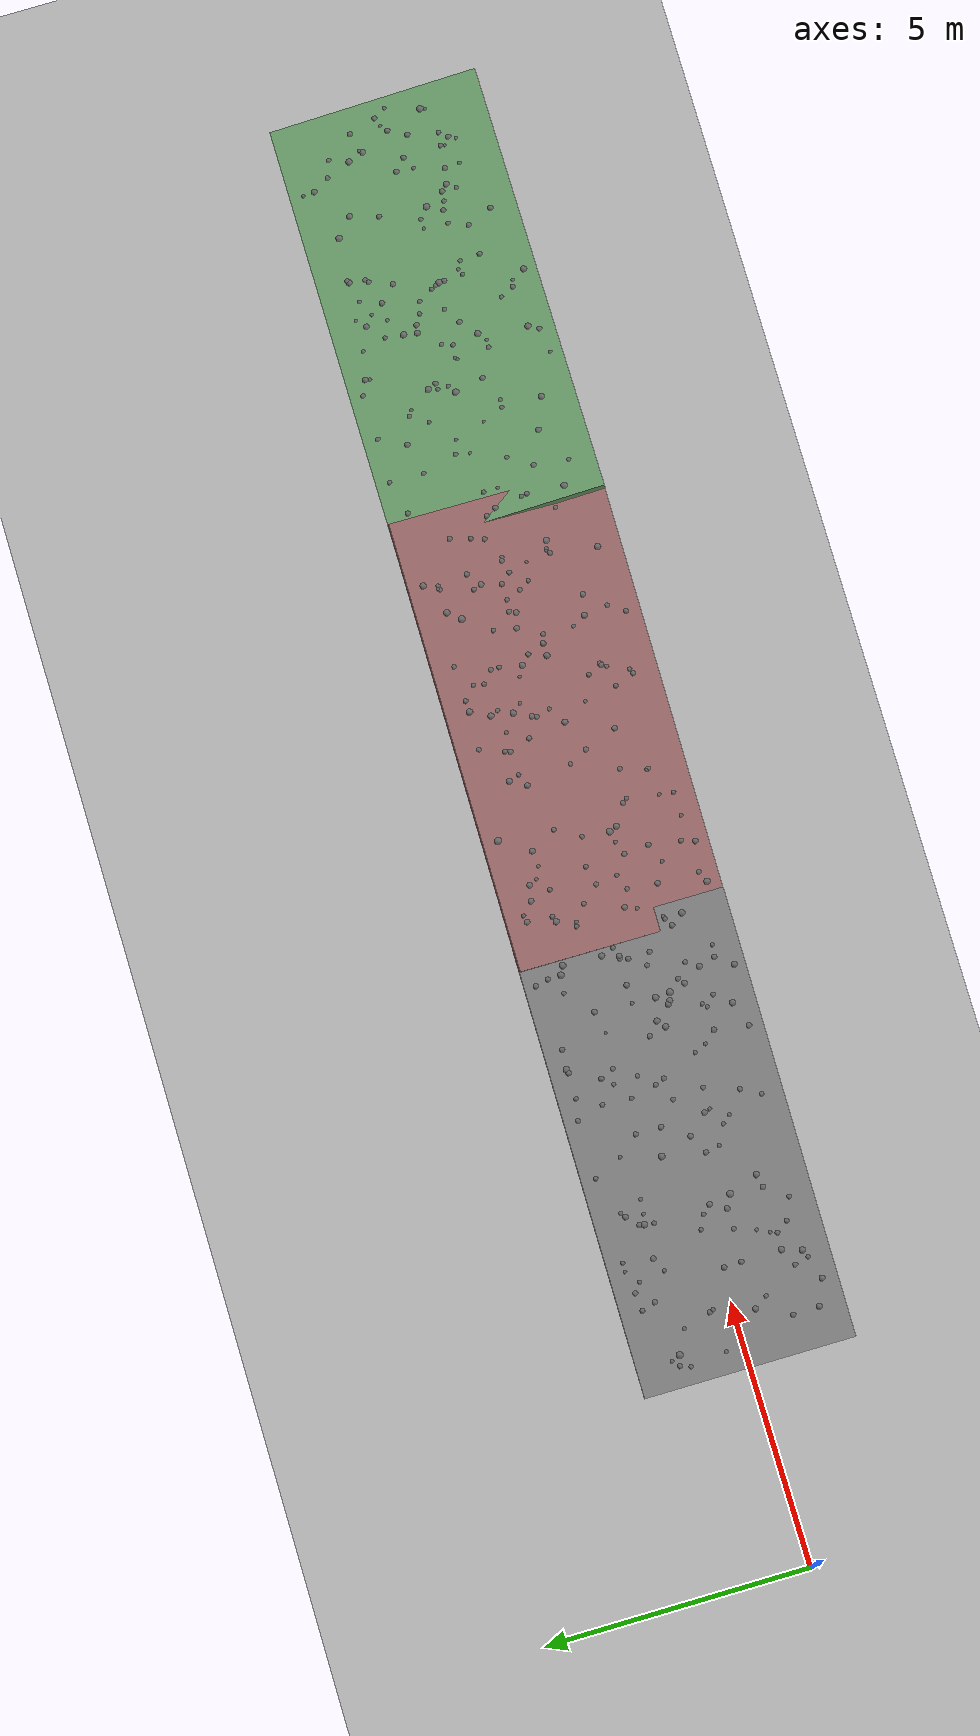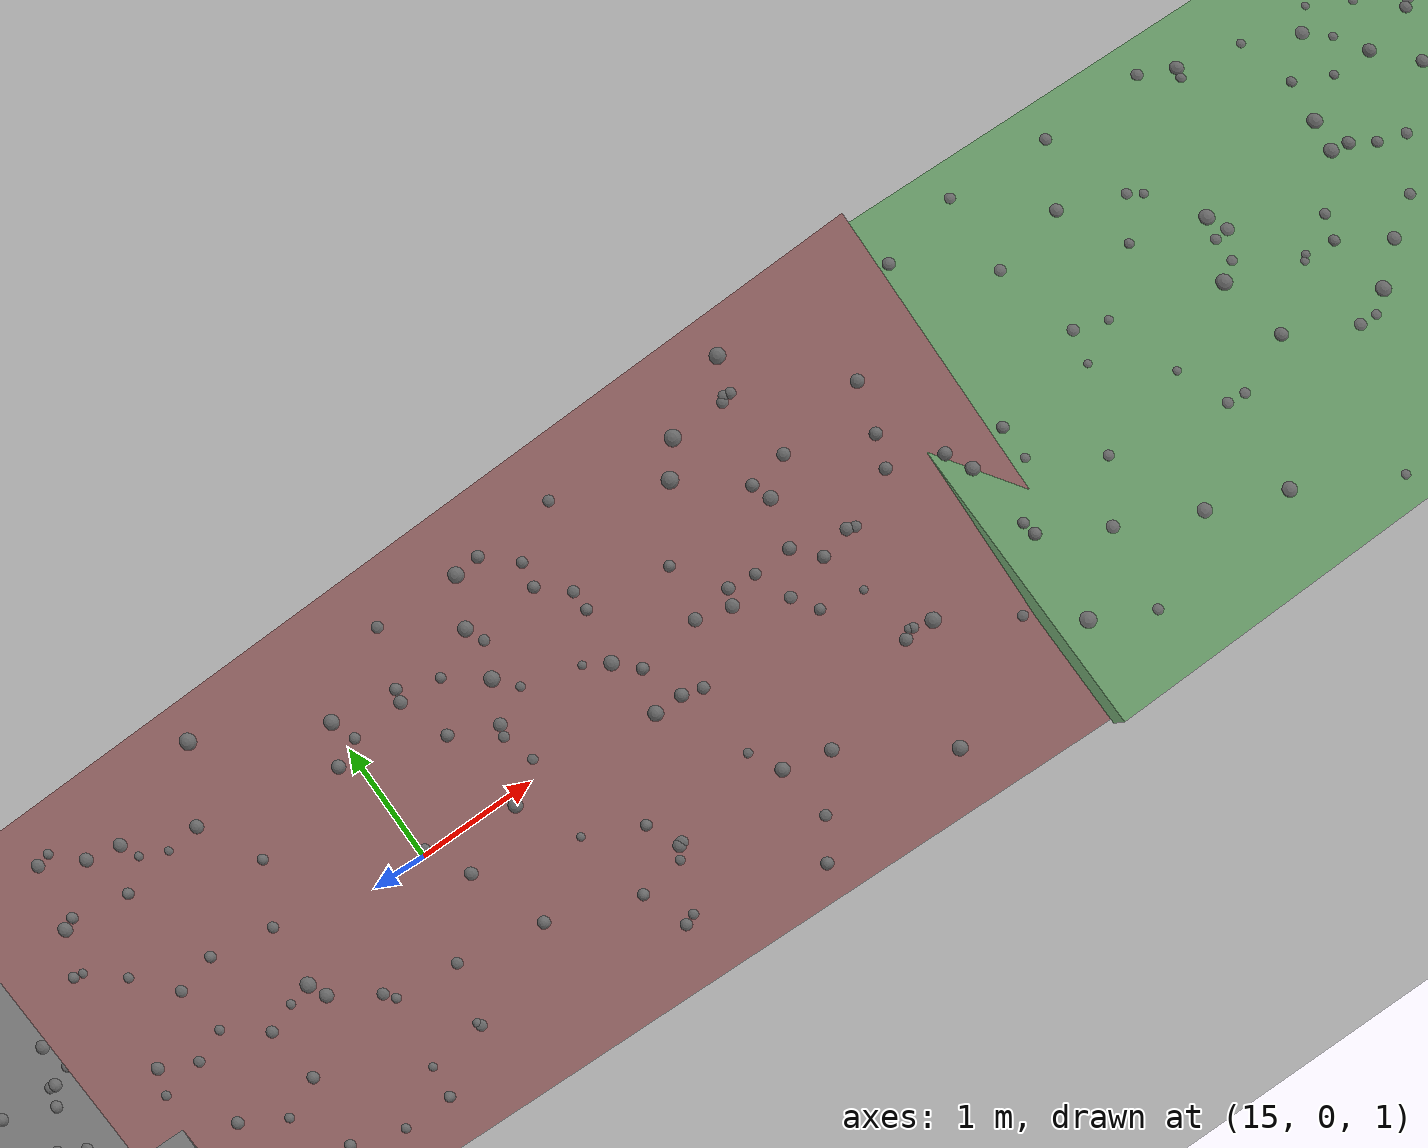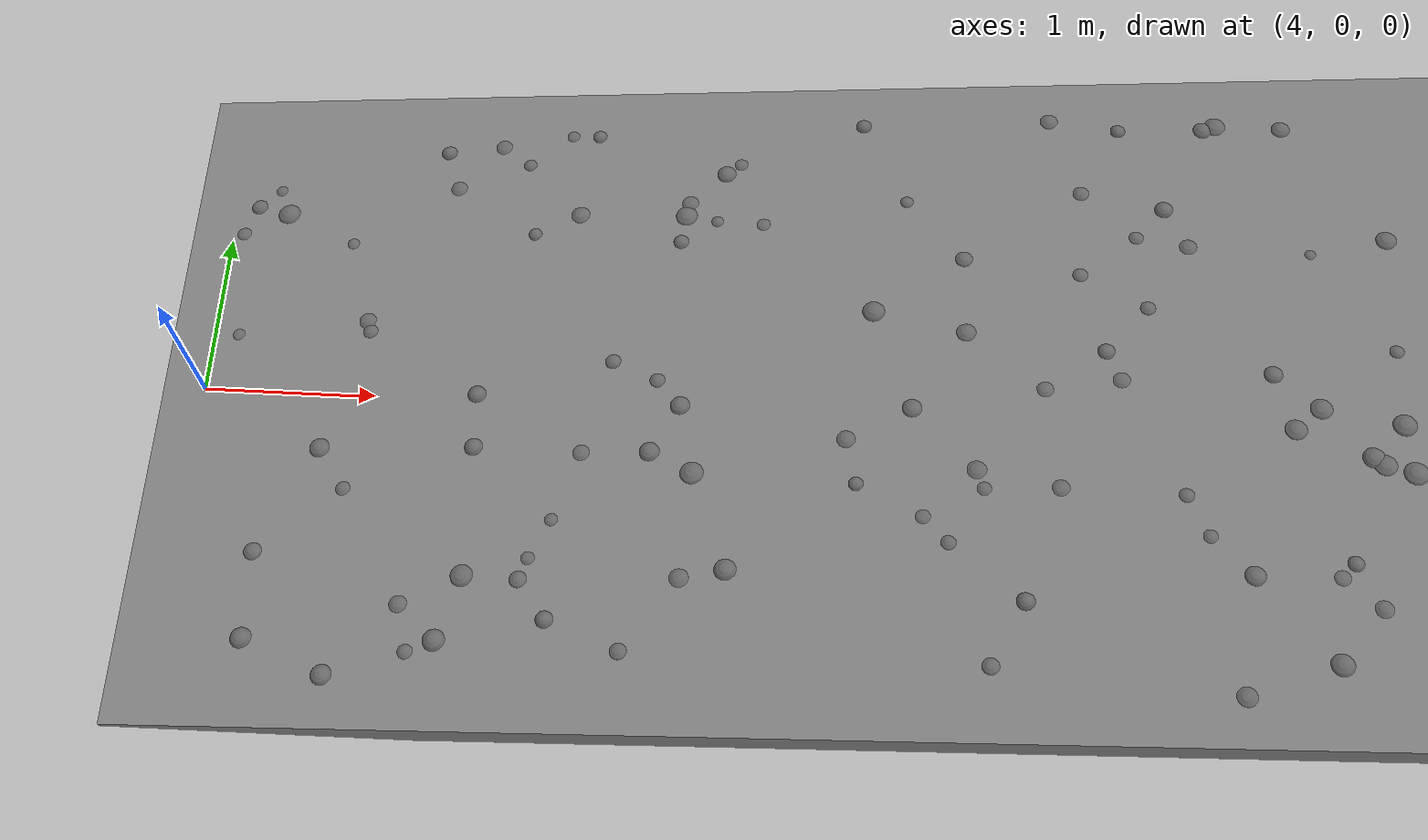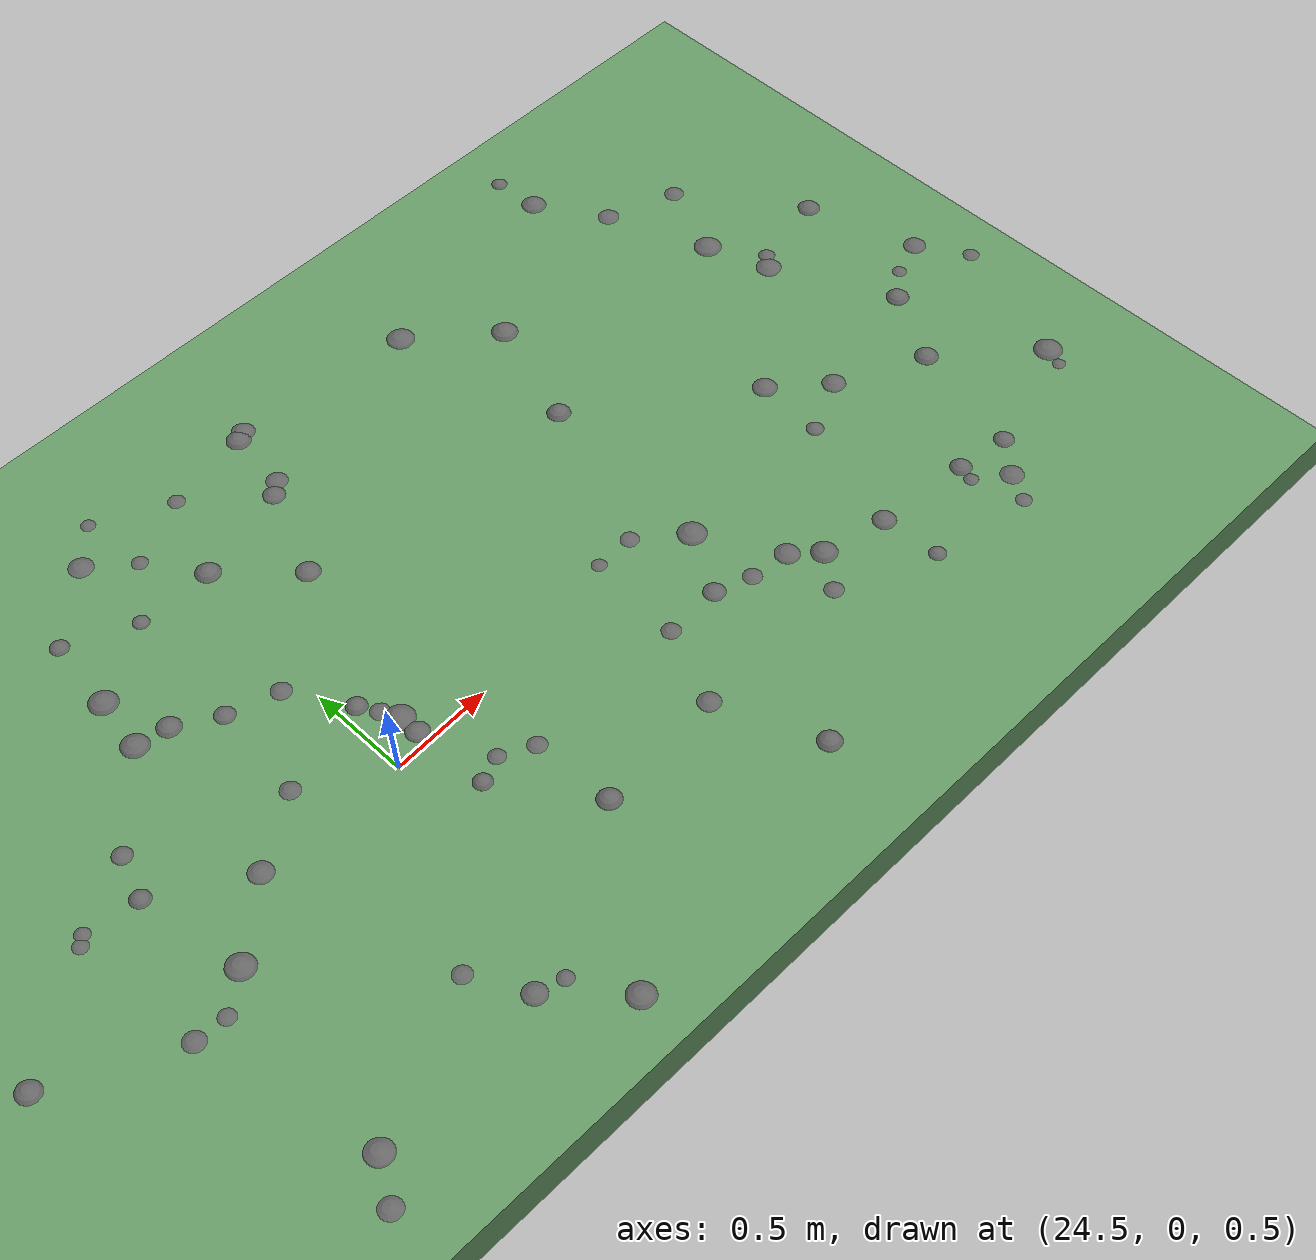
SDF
<?xml version="1.0" ?>
<sdf version="1.8">
<world name="extreme_disturbance_parkour">

    <plugin filename="gz-sim-physics-system" name="gz::sim::systems::Physics"></plugin>
    <plugin filename="gz-sim-scene-broadcaster-system" name="gz::sim::systems::SceneBroadcaster"></plugin>
    <plugin filename="gz-sim-user-commands-system" name="gz::sim::systems::UserCommands"></plugin>
    <scene>
      <ambient>0.6 0.6 0.6 1</ambient>
      <background>0.4 0.6 0.8 1</background>
      <shadows>true</shadows>
    </scene>
    <light type="directional" name="sun">
      <cast_shadows>true</cast_shadows>
      <pose>0 0 10 0 0 0</pose>
      <diffuse>0.9 0.9 0.9 1</diffuse>
      <specular>0.2 0.2 0.2 1</specular>
      <attenuation><range>1000</range><constant>0.9</constant><linear>0.01</linear><quadratic>0.001</quadratic></attenuation>
      <direction>-0.5 0.1 -0.9</direction>
    </light>
    <model name="ground_plane">
      <static>true</static>
      <link name="link">
        <collision name="collision">
          <geometry><plane><normal>0 0 1</normal><size>100 100</size></plane></geometry>
          <surface><friction><ode><mu>1.5</mu><mu2>1.5</mu2></ode></friction></surface> <!-- Zemin düzleminde tutunmayı artırmak için sürtünmeyi yükselttim. -->
        </collision>
        <visual name="visual">
          <geometry><plane><normal>0 0 1</normal><size>100 100</size></plane></geometry>
          <material><ambient>0.7 0.7 0.7 1</ambient><diffuse>0.7 0.7 0.7 1</diffuse></material>
        </visual>
      </link>
    </model>

    <model name="ramp_pitch">
      <static>true</static>
      <pose>8.0000 0.0000 0.3500 0.0000 -0.1000 0.0000</pose>
      <link name="link">
        <collision name="collision">
          <geometry><box><size>8.5000 4.0000 0.2000</size></box></geometry>
          <surface><friction><ode><mu>1.5</mu><mu2>1.5</mu2></ode></friction></surface> <!-- Düz rampa yüzeylerinde tutunmayı artırmak için sürtünmeyi yükselttim. -->
        </collision>
        <visual name="visual">
          <geometry><box><size>8.5000 4.0000 0.2000</size></box></geometry>
          <material>
            <ambient>0.5 0.5 0.5 1</ambient>
            <diffuse>0.5 0.5 0.5 1</diffuse>
          </material>
        </visual>
      </link>
    </model>

    <model name="ramp_roll_pitch">
      <static>true</static>
      <pose>16.0000 0.0000 1.2000 0.0700 -0.1000 0.0000</pose>
      <link name="link">
        <collision name="collision">
          <geometry><box><size>8.5000 4.0000 0.2000</size></box></geometry>
          <surface><friction><ode><mu>1.5</mu><mu2>1.5</mu2></ode></friction></surface> <!-- Düz rampa yüzeylerinde tutunmayı artırmak için sürtünmeyi yükselttim. -->
        </collision>
        <visual name="visual">
          <geometry><box><size>8.5000 4.0000 0.2000</size></box></geometry>
          <material>
            <ambient>0.6 0.4 0.4 1</ambient>
            <diffuse>0.6 0.4 0.4 1</diffuse>
          </material>
        </visual>
      </link>
    </model>

    <model name="ramp_down">
      <static>true</static>
      <pose>24.0000 0.0000 1.2000 -0.0700 0.1000 0.0000</pose>
      <link name="link">
        <collision name="collision">
          <geometry><box><size>8.5000 4.0000 0.2000</size></box></geometry>
          <surface><friction><ode><mu>1.5</mu><mu2>1.5</mu2></ode></friction></surface> <!-- Düz rampa yüzeylerinde tutunmayı artırmak için sürtünmeyi yükselttim. -->
        </collision>
        <visual name="visual">
          <geometry><box><size>8.5000 4.0000 0.2000</size></box></geometry>
          <material>
            <ambient>0.4 0.6 0.4 1</ambient>
            <diffuse>0.4 0.6 0.4 1</diffuse>
          </material>
        </visual>
      </link>
    </model>

    <model name="stone_0">
      <static>true</static>
      <pose>9.3757 0.4707 0.5406 0.0000 -0.1000 0.0000</pose>
      <link name="link">
        <collision name="collision">
          <geometry><sphere><radius>0.0648</radius></sphere></geometry>
          <surface><friction><ode><mu>100.0</mu><mu2>100.0</mu2></ode></friction></surface> <!-- Taş sürtünmesini bumpy.world ile eşitledim. -->
        </collision>
        <visual name="visual">
          <geometry><sphere><radius>0.0648</radius></sphere></geometry>
          <material>
            <ambient>0.3 0.3 0.3 1</ambient> <!-- Taş ortam rengini bumpy.world ile eşitledim. -->
            <diffuse>0.4 0.4 0.4 1</diffuse> <!-- Taş yayınık rengini bumpy.world ile eşitledim. -->
          </material>
        </visual>
      </link>
    </model>

    <model name="stone_1">
      <static>true</static>
      <pose>10.0039 0.0550 0.6089 0.0000 -0.1000 0.0000</pose>
      <link name="link">
        <collision name="collision">
          <geometry><sphere><radius>0.0667</radius></sphere></geometry>
          <surface><friction><ode><mu>100.0</mu><mu2>100.0</mu2></ode></friction></surface> <!-- Taş sürtünmesini bumpy.world ile eşitledim. -->
        </collision>
        <visual name="visual">
          <geometry><sphere><radius>0.0667</radius></sphere></geometry>
          <material>
            <ambient>0.3 0.3 0.3 1</ambient> <!-- Taş ortam rengini bumpy.world ile eşitledim. -->
            <diffuse>0.4 0.4 0.4 1</diffuse> <!-- Taş yayınık rengini bumpy.world ile eşitledim. -->
          </material>
        </visual>
      </link>
    </model>

    <model name="stone_2">
      <static>true</static>
      <pose>7.2294 1.0473 0.2989 0.0000 -0.1000 0.0000</pose>
      <link name="link">
        <collision name="collision">
          <geometry><sphere><radius>0.0851</radius></sphere></geometry>
          <surface><friction><ode><mu>100.0</mu><mu2>100.0</mu2></ode></friction></surface> <!-- Taş sürtünmesini bumpy.world ile eşitledim. -->
        </collision>
        <visual name="visual">
          <geometry><sphere><radius>0.0851</radius></sphere></geometry>
          <material>
            <ambient>0.3 0.3 0.3 1</ambient> <!-- Taş ortam rengini bumpy.world ile eşitledim. -->
            <diffuse>0.4 0.4 0.4 1</diffuse> <!-- Taş yayınık rengini bumpy.world ile eşitledim. -->
          </material>
        </visual>
      </link>
    </model>

    <model name="stone_3">
      <static>true</static>
      <pose>6.1135 -1.3869 0.2254 0.0000 -0.1000 0.0000</pose>
      <link name="link">
        <collision name="collision">
          <geometry><sphere><radius>0.0612</radius></sphere></geometry>
          <surface><friction><ode><mu>100.0</mu><mu2>100.0</mu2></ode></friction></surface> <!-- Taş sürtünmesini bumpy.world ile eşitledim. -->
        </collision>
        <visual name="visual">
          <geometry><sphere><radius>0.0612</radius></sphere></geometry>
          <material>
            <ambient>0.3 0.3 0.3 1</ambient> <!-- Taş ortam rengini bumpy.world ile eşitledim. -->
            <diffuse>0.4 0.4 0.4 1</diffuse> <!-- Taş yayınık rengini bumpy.world ile eşitledim. -->
          </material>
        </visual>
      </link>
    </model>

    <model name="stone_4">
      <static>true</static>
      <pose>7.7550 -0.5982 0.3980 0.0000 -0.1000 0.0000</pose>
      <link name="link">
        <collision name="collision">
          <geometry><sphere><radius>0.0503</radius></sphere></geometry>
          <surface><friction><ode><mu>100.0</mu><mu2>100.0</mu2></ode></friction></surface> <!-- Taş sürtünmesini bumpy.world ile eşitledim. -->
        </collision>
        <visual name="visual">
          <geometry><sphere><radius>0.0503</radius></sphere></geometry>
          <material>
            <ambient>0.3 0.3 0.3 1</ambient> <!-- Taş ortam rengini bumpy.world ile eşitledim. -->
            <diffuse>0.4 0.4 0.4 1</diffuse> <!-- Taş yayınık rengini bumpy.world ile eşitledim. -->
          </material>
        </visual>
      </link>
    </model>

    <model name="stone_5">
      <static>true</static>
      <pose>11.7191 0.2417 0.7836 0.0000 -0.1000 0.0000</pose>
      <link name="link">
        <collision name="collision">
          <geometry><sphere><radius>0.0618</radius></sphere></geometry>
          <surface><friction><ode><mu>100.0</mu><mu2>100.0</mu2></ode></friction></surface> <!-- Taş sürtünmesini bumpy.world ile eşitledim. -->
        </collision>
        <visual name="visual">
          <geometry><sphere><radius>0.0618</radius></sphere></geometry>
          <material>
            <ambient>0.3 0.3 0.3 1</ambient> <!-- Taş ortam rengini bumpy.world ile eşitledim. -->
            <diffuse>0.4 0.4 0.4 1</diffuse> <!-- Taş yayınık rengini bumpy.world ile eşitledim. -->
          </material>
        </visual>
      </link>
    </model>

    <model name="stone_6">
      <static>true</static>
      <pose>11.9863 -1.1465 0.7763 0.0000 -0.1000 0.0000</pose>
      <link name="link">
        <collision name="collision">
          <geometry><sphere><radius>0.0970</radius></sphere></geometry>
          <surface><friction><ode><mu>100.0</mu><mu2>100.0</mu2></ode></friction></surface> <!-- Taş sürtünmesini bumpy.world ile eşitledim. -->
        </collision>
        <visual name="visual">
          <geometry><sphere><radius>0.0970</radius></sphere></geometry>
          <material>
            <ambient>0.3 0.3 0.3 1</ambient> <!-- Taş ortam rengini bumpy.world ile eşitledim. -->
            <diffuse>0.4 0.4 0.4 1</diffuse> <!-- Taş yayınık rengini bumpy.world ile eşitledim. -->
          </material>
        </visual>
      </link>
    </model>

    <model name="stone_7">
      <static>true</static>
      <pose>8.0581 1.1895 0.4199 0.0000 -0.1000 0.0000</pose>
      <link name="link">
        <collision name="collision">
          <geometry><sphere><radius>0.0528</radius></sphere></geometry>
          <surface><friction><ode><mu>100.0</mu><mu2>100.0</mu2></ode></friction></surface> <!-- Taş sürtünmesini bumpy.world ile eşitledim. -->
        </collision>
        <visual name="visual">
          <geometry><sphere><radius>0.0528</radius></sphere></geometry>
          <material>
            <ambient>0.3 0.3 0.3 1</ambient> <!-- Taş ortam rengini bumpy.world ile eşitledim. -->
            <diffuse>0.4 0.4 0.4 1</diffuse> <!-- Taş yayınık rengini bumpy.world ile eşitledim. -->
          </material>
        </visual>
      </link>
    </model>

    <model name="stone_8">
      <static>true</static>
      <pose>8.2411 -0.9320 0.4269 0.0000 -0.1000 0.0000</pose>
      <link name="link">
        <collision name="collision">
          <geometry><sphere><radius>0.0634</radius></sphere></geometry>
          <surface><friction><ode><mu>100.0</mu><mu2>100.0</mu2></ode></friction></surface> <!-- Taş sürtünmesini bumpy.world ile eşitledim. -->
        </collision>
        <visual name="visual">
          <geometry><sphere><radius>0.0634</radius></sphere></geometry>
          <material>
            <ambient>0.3 0.3 0.3 1</ambient> <!-- Taş ortam rengini bumpy.world ile eşitledim. -->
            <diffuse>0.4 0.4 0.4 1</diffuse> <!-- Taş yayınık rengini bumpy.world ile eşitledim. -->
          </material>
        </visual>
      </link>
    </model>

    <model name="stone_9">
      <static>true</static>
      <pose>9.0567 1.2301 0.5017 0.0000 -0.1000 0.0000</pose>
      <link name="link">
        <collision name="collision">
          <geometry><sphere><radius>0.0722</radius></sphere></geometry>
          <surface><friction><ode><mu>100.0</mu><mu2>100.0</mu2></ode></friction></surface> <!-- Taş sürtünmesini bumpy.world ile eşitledim. -->
        </collision>
        <visual name="visual">
          <geometry><sphere><radius>0.0722</radius></sphere></geometry>
          <material>
            <ambient>0.3 0.3 0.3 1</ambient> <!-- Taş ortam rengini bumpy.world ile eşitledim. -->
            <diffuse>0.4 0.4 0.4 1</diffuse> <!-- Taş yayınık rengini bumpy.world ile eşitledim. -->
          </material>
        </visual>
      </link>
    </model>

    <model name="stone_10">
      <static>true</static>
      <pose>8.4352 -1.6017 0.4443 0.0000 -0.1000 0.0000</pose>
      <link name="link">
        <collision name="collision">
          <geometry><sphere><radius>0.0687</radius></sphere></geometry>
          <surface><friction><ode><mu>100.0</mu><mu2>100.0</mu2></ode></friction></surface> <!-- Taş sürtünmesini bumpy.world ile eşitledim. -->
        </collision>
        <visual name="visual">
          <geometry><sphere><radius>0.0687</radius></sphere></geometry>
          <material>
            <ambient>0.3 0.3 0.3 1</ambient> <!-- Taş ortam rengini bumpy.world ile eşitledim. -->
            <diffuse>0.4 0.4 0.4 1</diffuse> <!-- Taş yayınık rengini bumpy.world ile eşitledim. -->
          </material>
        </visual>
      </link>
    </model>

    <model name="stone_11">
      <static>true</static>
      <pose>4.4592 -1.0186 0.0421 0.0000 -0.1000 0.0000</pose>
      <link name="link">
        <collision name="collision">
          <geometry><sphere><radius>0.0747</radius></sphere></geometry>
          <surface><friction><ode><mu>100.0</mu><mu2>100.0</mu2></ode></friction></surface> <!-- Taş sürtünmesini bumpy.world ile eşitledim. -->
        </collision>
        <visual name="visual">
          <geometry><sphere><radius>0.0747</radius></sphere></geometry>
          <material>
            <ambient>0.3 0.3 0.3 1</ambient> <!-- Taş ortam rengini bumpy.world ile eşitledim. -->
            <diffuse>0.4 0.4 0.4 1</diffuse> <!-- Taş yayınık rengini bumpy.world ile eşitledim. -->
          </material>
        </visual>
      </link>
    </model>

    <model name="stone_12">
      <static>true</static>
      <pose>11.1829 1.3310 0.7065 0.0000 -0.1000 0.0000</pose>
      <link name="link">
        <collision name="collision">
          <geometry><sphere><radius>0.0766</radius></sphere></geometry>
          <surface><friction><ode><mu>100.0</mu><mu2>100.0</mu2></ode></friction></surface> <!-- Taş sürtünmesini bumpy.world ile eşitledim. -->
        </collision>
        <visual name="visual">
          <geometry><sphere><radius>0.0766</radius></sphere></geometry>
          <material>
            <ambient>0.3 0.3 0.3 1</ambient> <!-- Taş ortam rengini bumpy.world ile eşitledim. -->
            <diffuse>0.4 0.4 0.4 1</diffuse> <!-- Taş yayınık rengini bumpy.world ile eşitledim. -->
          </material>
        </visual>
      </link>
    </model>

    <model name="stone_13">
      <static>true</static>
      <pose>10.1640 -1.5656 0.6086 0.0000 -0.1000 0.0000</pose>
      <link name="link">
        <collision name="collision">
          <geometry><sphere><radius>0.0853</radius></sphere></geometry>
          <surface><friction><ode><mu>100.0</mu><mu2>100.0</mu2></ode></friction></surface> <!-- Taş sürtünmesini bumpy.world ile eşitledim. -->
        </collision>
        <visual name="visual">
          <geometry><sphere><radius>0.0853</radius></sphere></geometry>
          <material>
            <ambient>0.3 0.3 0.3 1</ambient> <!-- Taş ortam rengini bumpy.world ile eşitledim. -->
            <diffuse>0.4 0.4 0.4 1</diffuse> <!-- Taş yayınık rengini bumpy.world ile eşitledim. -->
          </material>
        </visual>
      </link>
    </model>

    <model name="stone_14">
      <static>true</static>
      <pose>4.1635 0.3348 -0.0073 0.0000 -0.1000 0.0000</pose>
      <link name="link">
        <collision name="collision">
          <geometry><sphere><radius>0.0825</radius></sphere></geometry>
          <surface><friction><ode><mu>100.0</mu><mu2>100.0</mu2></ode></friction></surface> <!-- Taş sürtünmesini bumpy.world ile eşitledim. -->
        </collision>
        <visual name="visual">
          <geometry><sphere><radius>0.0825</radius></sphere></geometry>
          <material>
            <ambient>0.3 0.3 0.3 1</ambient> <!-- Taş ortam rengini bumpy.world ile eşitledim. -->
            <diffuse>0.4 0.4 0.4 1</diffuse> <!-- Taş yayınık rengini bumpy.world ile eşitledim. -->
          </material>
        </visual>
      </link>
    </model>

    <model name="stone_15">
      <static>true</static>
      <pose>5.6336 1.6227 0.1323 0.0000 -0.1000 0.0000</pose>
      <link name="link">
        <collision name="collision">
          <geometry><sphere><radius>0.0954</radius></sphere></geometry>
          <surface><friction><ode><mu>100.0</mu><mu2>100.0</mu2></ode></friction></surface> <!-- Taş sürtünmesini bumpy.world ile eşitledim. -->
        </collision>
        <visual name="visual">
          <geometry><sphere><radius>0.0954</radius></sphere></geometry>
          <material>
            <ambient>0.3 0.3 0.3 1</ambient> <!-- Taş ortam rengini bumpy.world ile eşitledim. -->
            <diffuse>0.4 0.4 0.4 1</diffuse> <!-- Taş yayınık rengini bumpy.world ile eşitledim. -->
          </material>
        </visual>
      </link>
    </model>

    <model name="stone_16">
      <static>true</static>
      <pose>5.6341 -0.3858 0.1757 0.0000 -0.1000 0.0000</pose>
      <link name="link">
        <collision name="collision">
          <geometry><sphere><radius>0.0644</radius></sphere></geometry>
          <surface><friction><ode><mu>100.0</mu><mu2>100.0</mu2></ode></friction></surface> <!-- Taş sürtünmesini bumpy.world ile eşitledim. -->
        </collision>
        <visual name="visual">
          <geometry><sphere><radius>0.0644</radius></sphere></geometry>
          <material>
            <ambient>0.3 0.3 0.3 1</ambient> <!-- Taş ortam rengini bumpy.world ile eşitledim. -->
            <diffuse>0.4 0.4 0.4 1</diffuse> <!-- Taş yayınık rengini bumpy.world ile eşitledim. -->
          </material>
        </visual>
      </link>
    </model>

    <model name="stone_17">
      <static>true</static>
      <pose>9.0203 0.6874 0.5049 0.0000 -0.1000 0.0000</pose>
      <link name="link">
        <collision name="collision">
          <geometry><sphere><radius>0.0652</radius></sphere></geometry>
          <surface><friction><ode><mu>100.0</mu><mu2>100.0</mu2></ode></friction></surface> <!-- Taş sürtünmesini bumpy.world ile eşitledim. -->
        </collision>
        <visual name="visual">
          <geometry><sphere><radius>0.0652</radius></sphere></geometry>
          <material>
            <ambient>0.3 0.3 0.3 1</ambient> <!-- Taş ortam rengini bumpy.world ile eşitledim. -->
            <diffuse>0.4 0.4 0.4 1</diffuse> <!-- Taş yayınık rengini bumpy.world ile eşitledim. -->
          </material>
        </visual>
      </link>
    </model>

    <model name="stone_18">
      <static>true</static>
      <pose>9.5118 1.1131 0.5669 0.0000 -0.1000 0.0000</pose>
      <link name="link">
        <collision name="collision">
          <geometry><sphere><radius>0.0633</radius></sphere></geometry>
          <surface><friction><ode><mu>100.0</mu><mu2>100.0</mu2></ode></friction></surface> <!-- Taş sürtünmesini bumpy.world ile eşitledim. -->
        </collision>
        <visual name="visual">
          <geometry><sphere><radius>0.0633</radius></sphere></geometry>
          <material>
            <ambient>0.3 0.3 0.3 1</ambient> <!-- Taş ortam rengini bumpy.world ile eşitledim. -->
            <diffuse>0.4 0.4 0.4 1</diffuse> <!-- Taş yayınık rengini bumpy.world ile eşitledim. -->
          </material>
        </visual>
      </link>
    </model>

    <model name="stone_19">
      <static>true</static>
      <pose>10.2241 -1.1076 0.5861 0.0000 -0.1000 0.0000</pose>
      <link name="link">
        <collision name="collision">
          <geometry><sphere><radius>0.0982</radius></sphere></geometry>
          <surface><friction><ode><mu>100.0</mu><mu2>100.0</mu2></ode></friction></surface> <!-- Taş sürtünmesini bumpy.world ile eşitledim. -->
        </collision>
        <visual name="visual">
          <geometry><sphere><radius>0.0982</radius></sphere></geometry>
          <material>
            <ambient>0.3 0.3 0.3 1</ambient> <!-- Taş ortam rengini bumpy.world ile eşitledim. -->
            <diffuse>0.4 0.4 0.4 1</diffuse> <!-- Taş yayınık rengini bumpy.world ile eşitledim. -->
          </material>
        </visual>
      </link>
    </model>

    <model name="stone_20">
      <static>true</static>
      <pose>11.5009 0.1807 0.7408 0.0000 -0.1000 0.0000</pose>
      <link name="link">
        <collision name="collision">
          <geometry><sphere><radius>0.0770</radius></sphere></geometry>
          <surface><friction><ode><mu>100.0</mu><mu2>100.0</mu2></ode></friction></surface> <!-- Taş sürtünmesini bumpy.world ile eşitledim. -->
        </collision>
        <visual name="visual">
          <geometry><sphere><radius>0.0770</radius></sphere></geometry>
          <material>
            <ambient>0.3 0.3 0.3 1</ambient> <!-- Taş ortam rengini bumpy.world ile eşitledim. -->
            <diffuse>0.4 0.4 0.4 1</diffuse> <!-- Taş yayınık rengini bumpy.world ile eşitledim. -->
          </material>
        </visual>
      </link>
    </model>

    <model name="stone_21">
      <static>true</static>
      <pose>6.1080 -0.8187 0.2123 0.0000 -0.1000 0.0000</pose>
      <link name="link">
        <collision name="collision">
          <geometry><sphere><radius>0.0611</radius></sphere></geometry>
          <surface><friction><ode><mu>100.0</mu><mu2>100.0</mu2></ode></friction></surface> <!-- Taş sürtünmesini bumpy.world ile eşitledim. -->
        </collision>
        <visual name="visual">
          <geometry><sphere><radius>0.0611</radius></sphere></geometry>
          <material>
            <ambient>0.3 0.3 0.3 1</ambient> <!-- Taş ortam rengini bumpy.world ile eşitledim. -->
            <diffuse>0.4 0.4 0.4 1</diffuse> <!-- Taş yayınık rengini bumpy.world ile eşitledim. -->
          </material>
        </visual>
      </link>
    </model>

    <model name="stone_22">
      <static>true</static>
      <pose>5.8039 1.4889 0.1912 0.0000 -0.1000 0.0000</pose>
      <link name="link">
        <collision name="collision">
          <geometry><sphere><radius>0.0564</radius></sphere></geometry>
          <surface><friction><ode><mu>100.0</mu><mu2>100.0</mu2></ode></friction></surface> <!-- Taş sürtünmesini bumpy.world ile eşitledim. -->
        </collision>
        <visual name="visual">
          <geometry><sphere><radius>0.0564</radius></sphere></geometry>
          <material>
            <ambient>0.3 0.3 0.3 1</ambient> <!-- Taş ortam rengini bumpy.world ile eşitledim. -->
            <diffuse>0.4 0.4 0.4 1</diffuse> <!-- Taş yayınık rengini bumpy.world ile eşitledim. -->
          </material>
        </visual>
      </link>
    </model>

    <model name="stone_23">
      <static>true</static>
      <pose>12.0195 -0.7975 0.8147 0.0000 -0.1000 0.0000</pose>
      <link name="link">
        <collision name="collision">
          <geometry><sphere><radius>0.0561</radius></sphere></geometry>
          <surface><friction><ode><mu>100.0</mu><mu2>100.0</mu2></ode></friction></surface> <!-- Taş sürtünmesini bumpy.world ile eşitledim. -->
        </collision>
        <visual name="visual">
          <geometry><sphere><radius>0.0561</radius></sphere></geometry>
          <material>
            <ambient>0.3 0.3 0.3 1</ambient> <!-- Taş ortam rengini bumpy.world ile eşitledim. -->
            <diffuse>0.4 0.4 0.4 1</diffuse> <!-- Taş yayınık rengini bumpy.world ile eşitledim. -->
          </material>
        </visual>
      </link>
    </model>

    <model name="stone_24">
      <static>true</static>
      <pose>6.7449 0.9363 0.2904 0.0000 -0.1000 0.0000</pose>
      <link name="link">
        <collision name="collision">
          <geometry><sphere><radius>0.0572</radius></sphere></geometry>
          <surface><friction><ode><mu>100.0</mu><mu2>100.0</mu2></ode></friction></surface> <!-- Taş sürtünmesini bumpy.world ile eşitledim. -->
        </collision>
        <visual name="visual">
          <geometry><sphere><radius>0.0572</radius></sphere></geometry>
          <material>
            <ambient>0.3 0.3 0.3 1</ambient> <!-- Taş ortam rengini bumpy.world ile eşitledim. -->
            <diffuse>0.4 0.4 0.4 1</diffuse> <!-- Taş yayınık rengini bumpy.world ile eşitledim. -->
          </material>
        </visual>
      </link>
    </model>

    <model name="stone_25">
      <static>true</static>
      <pose>6.7739 1.1132 0.2559 0.0000 -0.1000 0.0000</pose>
      <link name="link">
        <collision name="collision">
          <geometry><sphere><radius>0.0967</radius></sphere></geometry>
          <surface><friction><ode><mu>100.0</mu><mu2>100.0</mu2></ode></friction></surface> <!-- Taş sürtünmesini bumpy.world ile eşitledim. -->
        </collision>
        <visual name="visual">
          <geometry><sphere><radius>0.0967</radius></sphere></geometry>
          <material>
            <ambient>0.3 0.3 0.3 1</ambient> <!-- Taş ortam rengini bumpy.world ile eşitledim. -->
            <diffuse>0.4 0.4 0.4 1</diffuse> <!-- Taş yayınık rengini bumpy.world ile eşitledim. -->
          </material>
        </visual>
      </link>
    </model>

    <model name="stone_26">
      <static>true</static>
      <pose>10.7482 -0.8293 0.6526 0.0000 -0.1000 0.0000</pose>
      <link name="link">
        <collision name="collision">
          <geometry><sphere><radius>0.0933</radius></sphere></geometry>
          <surface><friction><ode><mu>100.0</mu><mu2>100.0</mu2></ode></friction></surface> <!-- Taş sürtünmesini bumpy.world ile eşitledim. -->
        </collision>
        <visual name="visual">
          <geometry><sphere><radius>0.0933</radius></sphere></geometry>
          <material>
            <ambient>0.3 0.3 0.3 1</ambient> <!-- Taş ortam rengini bumpy.world ile eşitledim. -->
            <diffuse>0.4 0.4 0.4 1</diffuse> <!-- Taş yayınık rengini bumpy.world ile eşitledim. -->
          </material>
        </visual>
      </link>
    </model>

    <model name="stone_27">
      <static>true</static>
      <pose>11.4536 0.0299 0.7607 0.0000 -0.1000 0.0000</pose>
      <link name="link">
        <collision name="collision">
          <geometry><sphere><radius>0.0632</radius></sphere></geometry>
          <surface><friction><ode><mu>100.0</mu><mu2>100.0</mu2></ode></friction></surface> <!-- Taş sürtünmesini bumpy.world ile eşitledim. -->
        </collision>
        <visual name="visual">
          <geometry><sphere><radius>0.0632</radius></sphere></geometry>
          <material>
            <ambient>0.3 0.3 0.3 1</ambient> <!-- Taş ortam rengini bumpy.world ile eşitledim. -->
            <diffuse>0.4 0.4 0.4 1</diffuse> <!-- Taş yayınık rengini bumpy.world ile eşitledim. -->
          </material>
        </visual>
      </link>
    </model>

    <model name="stone_28">
      <static>true</static>
      <pose>10.6470 -0.2477 0.6514 0.0000 -0.1000 0.0000</pose>
      <link name="link">
        <collision name="collision">
          <geometry><sphere><radius>0.0914</radius></sphere></geometry>
          <surface><friction><ode><mu>100.0</mu><mu2>100.0</mu2></ode></friction></surface> <!-- Taş sürtünmesini bumpy.world ile eşitledim. -->
        </collision>
        <visual name="visual">
          <geometry><sphere><radius>0.0914</radius></sphere></geometry>
          <material>
            <ambient>0.3 0.3 0.3 1</ambient> <!-- Taş ortam rengini bumpy.world ile eşitledim. -->
            <diffuse>0.4 0.4 0.4 1</diffuse> <!-- Taş yayınık rengini bumpy.world ile eşitledim. -->
          </material>
        </visual>
      </link>
    </model>

    <model name="stone_29">
      <static>true</static>
      <pose>11.6739 1.2102 0.7517 0.0000 -0.1000 0.0000</pose>
      <link name="link">
        <collision name="collision">
          <geometry><sphere><radius>0.0941</radius></sphere></geometry>
          <surface><friction><ode><mu>100.0</mu><mu2>100.0</mu2></ode></friction></surface> <!-- Taş sürtünmesini bumpy.world ile eşitledim. -->
        </collision>
        <visual name="visual">
          <geometry><sphere><radius>0.0941</radius></sphere></geometry>
          <material>
            <ambient>0.3 0.3 0.3 1</ambient> <!-- Taş ortam rengini bumpy.world ile eşitledim. -->
            <diffuse>0.4 0.4 0.4 1</diffuse> <!-- Taş yayınık rengini bumpy.world ile eşitledim. -->
          </material>
        </visual>
      </link>
    </model>

    <model name="stone_30">
      <static>true</static>
      <pose>9.7909 -1.1007 0.5772 0.0000 -0.1000 0.0000</pose>
      <link name="link">
        <collision name="collision">
          <geometry><sphere><radius>0.0772</radius></sphere></geometry>
          <surface><friction><ode><mu>100.0</mu><mu2>100.0</mu2></ode></friction></surface> <!-- Taş sürtünmesini bumpy.world ile eşitledim. -->
        </collision>
        <visual name="visual">
          <geometry><sphere><radius>0.0772</radius></sphere></geometry>
          <material>
            <ambient>0.3 0.3 0.3 1</ambient> <!-- Taş ortam rengini bumpy.world ile eşitledim. -->
            <diffuse>0.4 0.4 0.4 1</diffuse> <!-- Taş yayınık rengini bumpy.world ile eşitledim. -->
          </material>
        </visual>
      </link>
    </model>

    <model name="stone_31">
      <static>true</static>
      <pose>8.4066 -0.5129 0.4129 0.0000 -0.1000 0.0000</pose>
      <link name="link">
        <collision name="collision">
          <geometry><sphere><radius>0.0950</radius></sphere></geometry>
          <surface><friction><ode><mu>100.0</mu><mu2>100.0</mu2></ode></friction></surface> <!-- Taş sürtünmesini bumpy.world ile eşitledim. -->
        </collision>
        <visual name="visual">
          <geometry><sphere><radius>0.0950</radius></sphere></geometry>
          <material>
            <ambient>0.3 0.3 0.3 1</ambient> <!-- Taş ortam rengini bumpy.world ile eşitledim. -->
            <diffuse>0.4 0.4 0.4 1</diffuse> <!-- Taş yayınık rengini bumpy.world ile eşitledim. -->
          </material>
        </visual>
      </link>
    </model>

    <model name="stone_32">
      <static>true</static>
      <pose>9.8498 1.6785 0.5675 0.0000 -0.1000 0.0000</pose>
      <link name="link">
        <collision name="collision">
          <geometry><sphere><radius>0.0921</radius></sphere></geometry>
          <surface><friction><ode><mu>100.0</mu><mu2>100.0</mu2></ode></friction></surface> <!-- Taş sürtünmesini bumpy.world ile eşitledim. -->
        </collision>
        <visual name="visual">
          <geometry><sphere><radius>0.0921</radius></sphere></geometry>
          <material>
            <ambient>0.3 0.3 0.3 1</ambient> <!-- Taş ortam rengini bumpy.world ile eşitledim. -->
            <diffuse>0.4 0.4 0.4 1</diffuse> <!-- Taş yayınık rengini bumpy.world ile eşitledim. -->
          </material>
        </visual>
      </link>
    </model>

    <model name="stone_33">
      <static>true</static>
      <pose>9.5877 -0.8852 0.5619 0.0000 -0.1000 0.0000</pose>
      <link name="link">
        <collision name="collision">
          <geometry><sphere><radius>0.0619</radius></sphere></geometry>
          <surface><friction><ode><mu>100.0</mu><mu2>100.0</mu2></ode></friction></surface> <!-- Taş sürtünmesini bumpy.world ile eşitledim. -->
        </collision>
        <visual name="visual">
          <geometry><sphere><radius>0.0619</radius></sphere></geometry>
          <material>
            <ambient>0.3 0.3 0.3 1</ambient> <!-- Taş ortam rengini bumpy.world ile eşitledim. -->
            <diffuse>0.4 0.4 0.4 1</diffuse> <!-- Taş yayınık rengini bumpy.world ile eşitledim. -->
          </material>
        </visual>
      </link>
    </model>

    <model name="stone_34">
      <static>true</static>
      <pose>7.8623 0.4618 0.3752 0.0000 -0.1000 0.0000</pose>
      <link name="link">
        <collision name="collision">
          <geometry><sphere><radius>0.0895</radius></sphere></geometry>
          <surface><friction><ode><mu>100.0</mu><mu2>100.0</mu2></ode></friction></surface> <!-- Taş sürtünmesini bumpy.world ile eşitledim. -->
        </collision>
        <visual name="visual">
          <geometry><sphere><radius>0.0895</radius></sphere></geometry>
          <material>
            <ambient>0.3 0.3 0.3 1</ambient> <!-- Taş ortam rengini bumpy.world ile eşitledim. -->
            <diffuse>0.4 0.4 0.4 1</diffuse> <!-- Taş yayınık rengini bumpy.world ile eşitledim. -->
          </material>
        </visual>
      </link>
    </model>

    <model name="stone_35">
      <static>true</static>
      <pose>10.9681 -1.1745 0.6739 0.0000 -0.1000 0.0000</pose>
      <link name="link">
        <collision name="collision">
          <geometry><sphere><radius>0.0961</radius></sphere></geometry>
          <surface><friction><ode><mu>100.0</mu><mu2>100.0</mu2></ode></friction></surface> <!-- Taş sürtünmesini bumpy.world ile eşitledim. -->
        </collision>
        <visual name="visual">
          <geometry><sphere><radius>0.0961</radius></sphere></geometry>
          <material>
            <ambient>0.3 0.3 0.3 1</ambient> <!-- Taş ortam rengini bumpy.world ile eşitledim. -->
            <diffuse>0.4 0.4 0.4 1</diffuse> <!-- Taş yayınık rengini bumpy.world ile eşitledim. -->
          </material>
        </visual>
      </link>
    </model>

    <model name="stone_36">
      <static>true</static>
      <pose>9.1305 0.2008 0.5250 0.0000 -0.1000 0.0000</pose>
      <link name="link">
        <collision name="collision">
          <geometry><sphere><radius>0.0622</radius></sphere></geometry>
          <surface><friction><ode><mu>100.0</mu><mu2>100.0</mu2></ode></friction></surface> <!-- Taş sürtünmesini bumpy.world ile eşitledim. -->
        </collision>
        <visual name="visual">
          <geometry><sphere><radius>0.0622</radius></sphere></geometry>
          <material>
            <ambient>0.3 0.3 0.3 1</ambient> <!-- Taş ortam rengini bumpy.world ile eşitledim. -->
            <diffuse>0.4 0.4 0.4 1</diffuse> <!-- Taş yayınık rengini bumpy.world ile eşitledim. -->
          </material>
        </visual>
      </link>
    </model>

    <model name="stone_37">
      <static>true</static>
      <pose>10.2843 0.8051 0.6389 0.0000 -0.1000 0.0000</pose>
      <link name="link">
        <collision name="collision">
          <geometry><sphere><radius>0.0508</radius></sphere></geometry>
          <surface><friction><ode><mu>100.0</mu><mu2>100.0</mu2></ode></friction></surface> <!-- Taş sürtünmesini bumpy.world ile eşitledim. -->
        </collision>
        <visual name="visual">
          <geometry><sphere><radius>0.0508</radius></sphere></geometry>
          <material>
            <ambient>0.3 0.3 0.3 1</ambient> <!-- Taş ortam rengini bumpy.world ile eşitledim. -->
            <diffuse>0.4 0.4 0.4 1</diffuse> <!-- Taş yayınık rengini bumpy.world ile eşitledim. -->
          </material>
        </visual>
      </link>
    </model>

    <model name="stone_38">
      <static>true</static>
      <pose>8.1130 -0.7865 0.3908 0.0000 -0.1000 0.0000</pose>
      <link name="link">
        <collision name="collision">
          <geometry><sphere><radius>0.0827</radius></sphere></geometry>
          <surface><friction><ode><mu>100.0</mu><mu2>100.0</mu2></ode></friction></surface> <!-- Taş sürtünmesini bumpy.world ile eşitledim. -->
        </collision>
        <visual name="visual">
          <geometry><sphere><radius>0.0827</radius></sphere></geometry>
          <material>
            <ambient>0.3 0.3 0.3 1</ambient> <!-- Taş ortam rengini bumpy.world ile eşitledim. -->
            <diffuse>0.4 0.4 0.4 1</diffuse> <!-- Taş yayınık rengini bumpy.world ile eşitledim. -->
          </material>
        </visual>
      </link>
    </model>

    <model name="stone_39">
      <static>true</static>
      <pose>4.9296 0.4222 0.0654 0.0000 -0.1000 0.0000</pose>
      <link name="link">
        <collision name="collision">
          <geometry><sphere><radius>0.0925</radius></sphere></geometry>
          <surface><friction><ode><mu>100.0</mu><mu2>100.0</mu2></ode></friction></surface> <!-- Taş sürtünmesini bumpy.world ile eşitledim. -->
        </collision>
        <visual name="visual">
          <geometry><sphere><radius>0.0925</radius></sphere></geometry>
          <material>
            <ambient>0.3 0.3 0.3 1</ambient> <!-- Taş ortam rengini bumpy.world ile eşitledim. -->
            <diffuse>0.4 0.4 0.4 1</diffuse> <!-- Taş yayınık rengini bumpy.world ile eşitledim. -->
          </material>
        </visual>
      </link>
    </model>

    <model name="stone_40">
      <static>true</static>
      <pose>10.2325 -0.1514 0.6092 0.0000 -0.1000 0.0000</pose>
      <link name="link">
        <collision name="collision">
          <geometry><sphere><radius>0.0893</radius></sphere></geometry>
          <surface><friction><ode><mu>100.0</mu><mu2>100.0</mu2></ode></friction></surface> <!-- Taş sürtünmesini bumpy.world ile eşitledim. -->
        </collision>
        <visual name="visual">
          <geometry><sphere><radius>0.0893</radius></sphere></geometry>
          <material>
            <ambient>0.3 0.3 0.3 1</ambient> <!-- Taş ortam rengini bumpy.world ile eşitledim. -->
            <diffuse>0.4 0.4 0.4 1</diffuse> <!-- Taş yayınık rengini bumpy.world ile eşitledim. -->
          </material>
        </visual>
      </link>
    </model>

    <model name="stone_41">
      <static>true</static>
      <pose>11.5058 1.5406 0.7559 0.0000 -0.1000 0.0000</pose>
      <link name="link">
        <collision name="collision">
          <geometry><sphere><radius>0.0701</radius></sphere></geometry>
          <surface><friction><ode><mu>100.0</mu><mu2>100.0</mu2></ode></friction></surface> <!-- Taş sürtünmesini bumpy.world ile eşitledim. -->
        </collision>
        <visual name="visual">
          <geometry><sphere><radius>0.0701</radius></sphere></geometry>
          <material>
            <ambient>0.3 0.3 0.3 1</ambient> <!-- Taş ortam rengini bumpy.world ile eşitledim. -->
            <diffuse>0.4 0.4 0.4 1</diffuse> <!-- Taş yayınık rengini bumpy.world ile eşitledim. -->
          </material>
        </visual>
      </link>
    </model>

    <model name="stone_42">
      <static>true</static>
      <pose>10.2178 1.6508 0.6196 0.0000 -0.1000 0.0000</pose>
      <link name="link">
        <collision name="collision">
          <geometry><sphere><radius>0.0754</radius></sphere></geometry>
          <surface><friction><ode><mu>100.0</mu><mu2>100.0</mu2></ode></friction></surface> <!-- Taş sürtünmesini bumpy.world ile eşitledim. -->
        </collision>
        <visual name="visual">
          <geometry><sphere><radius>0.0754</radius></sphere></geometry>
          <material>
            <ambient>0.3 0.3 0.3 1</ambient> <!-- Taş ortam rengini bumpy.world ile eşitledim. -->
            <diffuse>0.4 0.4 0.4 1</diffuse> <!-- Taş yayınık rengini bumpy.world ile eşitledim. -->
          </material>
        </visual>
      </link>
    </model>

    <model name="stone_43">
      <static>true</static>
      <pose>10.8251 -1.7958 0.6783 0.0000 -0.1000 0.0000</pose>
      <link name="link">
        <collision name="collision">
          <geometry><sphere><radius>0.0821</radius></sphere></geometry>
          <surface><friction><ode><mu>100.0</mu><mu2>100.0</mu2></ode></friction></surface> <!-- Taş sürtünmesini bumpy.world ile eşitledim. -->
        </collision>
        <visual name="visual">
          <geometry><sphere><radius>0.0821</radius></sphere></geometry>
          <material>
            <ambient>0.3 0.3 0.3 1</ambient> <!-- Taş ortam rengini bumpy.world ile eşitledim. -->
            <diffuse>0.4 0.4 0.4 1</diffuse> <!-- Taş yayınık rengini bumpy.world ile eşitledim. -->
          </material>
        </visual>
      </link>
    </model>

    <model name="stone_44">
      <static>true</static>
      <pose>5.8724 0.9992 0.2047 0.0000 -0.1000 0.0000</pose>
      <link name="link">
        <collision name="collision">
          <geometry><sphere><radius>0.0520</radius></sphere></geometry>
          <surface><friction><ode><mu>100.0</mu><mu2>100.0</mu2></ode></friction></surface> <!-- Taş sürtünmesini bumpy.world ile eşitledim. -->
        </collision>
        <visual name="visual">
          <geometry><sphere><radius>0.0520</radius></sphere></geometry>
          <material>
            <ambient>0.3 0.3 0.3 1</ambient> <!-- Taş ortam rengini bumpy.world ile eşitledim. -->
            <diffuse>0.4 0.4 0.4 1</diffuse> <!-- Taş yayınık rengini bumpy.world ile eşitledim. -->
          </material>
        </visual>
      </link>
    </model>

    <model name="stone_45">
      <static>true</static>
      <pose>10.6666 -0.5256 0.6468 0.0000 -0.1000 0.0000</pose>
      <link name="link">
        <collision name="collision">
          <geometry><sphere><radius>0.0976</radius></sphere></geometry>
          <surface><friction><ode><mu>100.0</mu><mu2>100.0</mu2></ode></friction></surface> <!-- Taş sürtünmesini bumpy.world ile eşitledim. -->
        </collision>
        <visual name="visual">
          <geometry><sphere><radius>0.0976</radius></sphere></geometry>
          <material>
            <ambient>0.3 0.3 0.3 1</ambient> <!-- Taş ortam rengini bumpy.world ile eşitledim. -->
            <diffuse>0.4 0.4 0.4 1</diffuse> <!-- Taş yayınık rengini bumpy.world ile eşitledim. -->
          </material>
        </visual>
      </link>
    </model>

    <model name="stone_46">
      <static>true</static>
      <pose>9.7780 1.6553 0.5763 0.0000 -0.1000 0.0000</pose>
      <link name="link">
        <collision name="collision">
          <geometry><sphere><radius>0.0758</radius></sphere></geometry>
          <surface><friction><ode><mu>100.0</mu><mu2>100.0</mu2></ode></friction></surface> <!-- Taş sürtünmesini bumpy.world ile eşitledim. -->
        </collision>
        <visual name="visual">
          <geometry><sphere><radius>0.0758</radius></sphere></geometry>
          <material>
            <ambient>0.3 0.3 0.3 1</ambient> <!-- Taş ortam rengini bumpy.world ile eşitledim. -->
            <diffuse>0.4 0.4 0.4 1</diffuse> <!-- Taş yayınık rengini bumpy.world ile eşitledim. -->
          </material>
        </visual>
      </link>
    </model>

    <model name="stone_47">
      <static>true</static>
      <pose>12.0115 -0.1642 0.7707 0.0000 -0.1000 0.0000</pose>
      <link name="link">
        <collision name="collision">
          <geometry><sphere><radius>0.0964</radius></sphere></geometry>
          <surface><friction><ode><mu>100.0</mu><mu2>100.0</mu2></ode></friction></surface> <!-- Taş sürtünmesini bumpy.world ile eşitledim. -->
        </collision>
        <visual name="visual">
          <geometry><sphere><radius>0.0964</radius></sphere></geometry>
          <material>
            <ambient>0.3 0.3 0.3 1</ambient> <!-- Taş ortam rengini bumpy.world ile eşitledim. -->
            <diffuse>0.4 0.4 0.4 1</diffuse> <!-- Taş yayınık rengini bumpy.world ile eşitledim. -->
          </material>
        </visual>
      </link>
    </model>

    <model name="stone_48">
      <static>true</static>
      <pose>5.3144 -1.3119 0.1147 0.0000 -0.1000 0.0000</pose>
      <link name="link">
        <collision name="collision">
          <geometry><sphere><radius>0.0829</radius></sphere></geometry>
          <surface><friction><ode><mu>100.0</mu><mu2>100.0</mu2></ode></friction></surface> <!-- Taş sürtünmesini bumpy.world ile eşitledim. -->
        </collision>
        <visual name="visual">
          <geometry><sphere><radius>0.0829</radius></sphere></geometry>
          <material>
            <ambient>0.3 0.3 0.3 1</ambient> <!-- Taş ortam rengini bumpy.world ile eşitledim. -->
            <diffuse>0.4 0.4 0.4 1</diffuse> <!-- Taş yayınık rengini bumpy.world ile eşitledim. -->
          </material>
        </visual>
      </link>
    </model>

    <model name="stone_49">
      <static>true</static>
      <pose>9.6868 -1.7377 0.5513 0.0000 -0.1000 0.0000</pose>
      <link name="link">
        <collision name="collision">
          <geometry><sphere><radius>0.0868</radius></sphere></geometry>
          <surface><friction><ode><mu>100.0</mu><mu2>100.0</mu2></ode></friction></surface> <!-- Taş sürtünmesini bumpy.world ile eşitledim. -->
        </collision>
        <visual name="visual">
          <geometry><sphere><radius>0.0868</radius></sphere></geometry>
          <material>
            <ambient>0.3 0.3 0.3 1</ambient> <!-- Taş ortam rengini bumpy.world ile eşitledim. -->
            <diffuse>0.4 0.4 0.4 1</diffuse> <!-- Taş yayınık rengini bumpy.world ile eşitledim. -->
          </material>
        </visual>
      </link>
    </model>

    <model name="stone_50">
      <static>true</static>
      <pose>11.2524 -0.2642 0.6929 0.0000 -0.1000 0.0000</pose>
      <link name="link">
        <collision name="collision">
          <geometry><sphere><radius>0.0968</radius></sphere></geometry>
          <surface><friction><ode><mu>100.0</mu><mu2>100.0</mu2></ode></friction></surface> <!-- Taş sürtünmesini bumpy.world ile eşitledim. -->
        </collision>
        <visual name="visual">
          <geometry><sphere><radius>0.0968</radius></sphere></geometry>
          <material>
            <ambient>0.3 0.3 0.3 1</ambient> <!-- Taş ortam rengini bumpy.world ile eşitledim. -->
            <diffuse>0.4 0.4 0.4 1</diffuse> <!-- Taş yayınık rengini bumpy.world ile eşitledim. -->
          </material>
        </visual>
      </link>
    </model>

    <model name="stone_51">
      <static>true</static>
      <pose>8.4394 -0.6225 0.4384 0.0000 -0.1000 0.0000</pose>
      <link name="link">
        <collision name="collision">
          <geometry><sphere><radius>0.0687</radius></sphere></geometry>
          <surface><friction><ode><mu>100.0</mu><mu2>100.0</mu2></ode></friction></surface> <!-- Taş sürtünmesini bumpy.world ile eşitledim. -->
        </collision>
        <visual name="visual">
          <geometry><sphere><radius>0.0687</radius></sphere></geometry>
          <material>
            <ambient>0.3 0.3 0.3 1</ambient> <!-- Taş ortam rengini bumpy.world ile eşitledim. -->
            <diffuse>0.4 0.4 0.4 1</diffuse> <!-- Taş yayınık rengini bumpy.world ile eşitledim. -->
          </material>
        </visual>
      </link>
    </model>

    <model name="stone_52">
      <static>true</static>
      <pose>5.6225 -0.0572 0.1732 0.0000 -0.1000 0.0000</pose>
      <link name="link">
        <collision name="collision">
          <geometry><sphere><radius>0.0659</radius></sphere></geometry>
          <surface><friction><ode><mu>100.0</mu><mu2>100.0</mu2></ode></friction></surface> <!-- Taş sürtünmesini bumpy.world ile eşitledim. -->
        </collision>
        <visual name="visual">
          <geometry><sphere><radius>0.0659</radius></sphere></geometry>
          <material>
            <ambient>0.3 0.3 0.3 1</ambient> <!-- Taş ortam rengini bumpy.world ile eşitledim. -->
            <diffuse>0.4 0.4 0.4 1</diffuse> <!-- Taş yayınık rengini bumpy.world ile eşitledim. -->
          </material>
        </visual>
      </link>
    </model>

    <model name="stone_53">
      <static>true</static>
      <pose>11.4695 -0.3773 0.7248 0.0000 -0.1000 0.0000</pose>
      <link name="link">
        <collision name="collision">
          <geometry><sphere><radius>0.0893</radius></sphere></geometry>
          <surface><friction><ode><mu>100.0</mu><mu2>100.0</mu2></ode></friction></surface> <!-- Taş sürtünmesini bumpy.world ile eşitledim. -->
        </collision>
        <visual name="visual">
          <geometry><sphere><radius>0.0893</radius></sphere></geometry>
          <material>
            <ambient>0.3 0.3 0.3 1</ambient> <!-- Taş ortam rengini bumpy.world ile eşitledim. -->
            <diffuse>0.4 0.4 0.4 1</diffuse> <!-- Taş yayınık rengini bumpy.world ile eşitledim. -->
          </material>
        </visual>
      </link>
    </model>

    <model name="stone_54">
      <static>true</static>
      <pose>7.0863 1.4678 0.3031 0.0000 -0.1000 0.0000</pose>
      <link name="link">
        <collision name="collision">
          <geometry><sphere><radius>0.0682</radius></sphere></geometry>
          <surface><friction><ode><mu>100.0</mu><mu2>100.0</mu2></ode></friction></surface> <!-- Taş sürtünmesini bumpy.world ile eşitledim. -->
        </collision>
        <visual name="visual">
          <geometry><sphere><radius>0.0682</radius></sphere></geometry>
          <material>
            <ambient>0.3 0.3 0.3 1</ambient> <!-- Taş ortam rengini bumpy.world ile eşitledim. -->
            <diffuse>0.4 0.4 0.4 1</diffuse> <!-- Taş yayınık rengini bumpy.world ile eşitledim. -->
          </material>
        </visual>
      </link>
    </model>

    <model name="stone_55">
      <static>true</static>
      <pose>10.8614 -0.7398 0.6738 0.0000 -0.1000 0.0000</pose>
      <link name="link">
        <collision name="collision">
          <geometry><sphere><radius>0.0810</radius></sphere></geometry>
          <surface><friction><ode><mu>100.0</mu><mu2>100.0</mu2></ode></friction></surface> <!-- Taş sürtünmesini bumpy.world ile eşitledim. -->
        </collision>
        <visual name="visual">
          <geometry><sphere><radius>0.0810</radius></sphere></geometry>
          <material>
            <ambient>0.3 0.3 0.3 1</ambient> <!-- Taş ortam rengini bumpy.world ile eşitledim. -->
            <diffuse>0.4 0.4 0.4 1</diffuse> <!-- Taş yayınık rengini bumpy.world ile eşitledim. -->
          </material>
        </visual>
      </link>
    </model>

    <model name="stone_56">
      <static>true</static>
      <pose>9.2042 0.0235 0.4935 0.0000 -0.1000 0.0000</pose>
      <link name="link">
        <collision name="collision">
          <geometry><sphere><radius>0.0917</radius></sphere></geometry>
          <surface><friction><ode><mu>100.0</mu><mu2>100.0</mu2></ode></friction></surface> <!-- Taş sürtünmesini bumpy.world ile eşitledim. -->
        </collision>
        <visual name="visual">
          <geometry><sphere><radius>0.0917</radius></sphere></geometry>
          <material>
            <ambient>0.3 0.3 0.3 1</ambient> <!-- Taş ortam rengini bumpy.world ile eşitledim. -->
            <diffuse>0.4 0.4 0.4 1</diffuse> <!-- Taş yayınık rengini bumpy.world ile eşitledim. -->
          </material>
        </visual>
      </link>
    </model>

    <model name="stone_57">
      <static>true</static>
      <pose>8.3766 0.7990 0.4358 0.0000 -0.1000 0.0000</pose>
      <link name="link">
        <collision name="collision">
          <geometry><sphere><radius>0.0725</radius></sphere></geometry>
          <surface><friction><ode><mu>100.0</mu><mu2>100.0</mu2></ode></friction></surface> <!-- Taş sürtünmesini bumpy.world ile eşitledim. -->
        </collision>
        <visual name="visual">
          <geometry><sphere><radius>0.0725</radius></sphere></geometry>
          <material>
            <ambient>0.3 0.3 0.3 1</ambient> <!-- Taş ortam rengini bumpy.world ile eşitledim. -->
            <diffuse>0.4 0.4 0.4 1</diffuse> <!-- Taş yayınık rengini bumpy.world ile eşitledim. -->
          </material>
        </visual>
      </link>
    </model>

    <model name="stone_58">
      <static>true</static>
      <pose>11.1083 -0.9459 0.7224 0.0000 -0.1000 0.0000</pose>
      <link name="link">
        <collision name="collision">
          <geometry><sphere><radius>0.0616</radius></sphere></geometry>
          <surface><friction><ode><mu>100.0</mu><mu2>100.0</mu2></ode></friction></surface> <!-- Taş sürtünmesini bumpy.world ile eşitledim. -->
        </collision>
        <visual name="visual">
          <geometry><sphere><radius>0.0616</radius></sphere></geometry>
          <material>
            <ambient>0.3 0.3 0.3 1</ambient> <!-- Taş ortam rengini bumpy.world ile eşitledim. -->
            <diffuse>0.4 0.4 0.4 1</diffuse> <!-- Taş yayınık rengini bumpy.world ile eşitledim. -->
          </material>
        </visual>
      </link>
    </model>

    <model name="stone_59">
      <static>true</static>
      <pose>7.0654 -1.0964 0.3054 0.0000 -0.1000 0.0000</pose>
      <link name="link">
        <collision name="collision">
          <geometry><sphere><radius>0.0802</radius></sphere></geometry>
          <surface><friction><ode><mu>100.0</mu><mu2>100.0</mu2></ode></friction></surface> <!-- Taş sürtünmesini bumpy.world ile eşitledim. -->
        </collision>
        <visual name="visual">
          <geometry><sphere><radius>0.0802</radius></sphere></geometry>
          <material>
            <ambient>0.3 0.3 0.3 1</ambient> <!-- Taş ortam rengini bumpy.world ile eşitledim. -->
            <diffuse>0.4 0.4 0.4 1</diffuse> <!-- Taş yayınık rengini bumpy.world ile eşitledim. -->
          </material>
        </visual>
      </link>
    </model>

    <model name="stone_60">
      <static>true</static>
      <pose>11.0488 -1.4825 0.7199 0.0000 -0.1000 0.0000</pose>
      <link name="link">
        <collision name="collision">
          <geometry><sphere><radius>0.0637</radius></sphere></geometry>
          <surface><friction><ode><mu>100.0</mu><mu2>100.0</mu2></ode></friction></surface> <!-- Taş sürtünmesini bumpy.world ile eşitledim. -->
        </collision>
        <visual name="visual">
          <geometry><sphere><radius>0.0637</radius></sphere></geometry>
          <material>
            <ambient>0.3 0.3 0.3 1</ambient> <!-- Taş ortam rengini bumpy.world ile eşitledim. -->
            <diffuse>0.4 0.4 0.4 1</diffuse> <!-- Taş yayınık rengini bumpy.world ile eşitledim. -->
          </material>
        </visual>
      </link>
    </model>

    <model name="stone_61">
      <static>true</static>
      <pose>6.3909 0.1479 0.2459 0.0000 -0.1000 0.0000</pose>
      <link name="link">
        <collision name="collision">
          <geometry><sphere><radius>0.0630</radius></sphere></geometry>
          <surface><friction><ode><mu>100.0</mu><mu2>100.0</mu2></ode></friction></surface> <!-- Taş sürtünmesini bumpy.world ile eşitledim. -->
        </collision>
        <visual name="visual">
          <geometry><sphere><radius>0.0630</radius></sphere></geometry>
          <material>
            <ambient>0.3 0.3 0.3 1</ambient> <!-- Taş ortam rengini bumpy.world ile eşitledim. -->
            <diffuse>0.4 0.4 0.4 1</diffuse> <!-- Taş yayınık rengini bumpy.world ile eşitledim. -->
          </material>
        </visual>
      </link>
    </model>

    <model name="stone_62">
      <static>true</static>
      <pose>6.7843 -0.1289 0.2803 0.0000 -0.1000 0.0000</pose>
      <link name="link">
        <collision name="collision">
          <geometry><sphere><radius>0.0742</radius></sphere></geometry>
          <surface><friction><ode><mu>100.0</mu><mu2>100.0</mu2></ode></friction></surface> <!-- Taş sürtünmesini bumpy.world ile eşitledim. -->
        </collision>
        <visual name="visual">
          <geometry><sphere><radius>0.0742</radius></sphere></geometry>
          <material>
            <ambient>0.3 0.3 0.3 1</ambient> <!-- Taş ortam rengini bumpy.world ile eşitledim. -->
            <diffuse>0.4 0.4 0.4 1</diffuse> <!-- Taş yayınık rengini bumpy.world ile eşitledim. -->
          </material>
        </visual>
      </link>
    </model>

    <model name="stone_63">
      <static>true</static>
      <pose>5.2905 1.5885 0.1482 0.0000 -0.1000 0.0000</pose>
      <link name="link">
        <collision name="collision">
          <geometry><sphere><radius>0.0575</radius></sphere></geometry>
          <surface><friction><ode><mu>100.0</mu><mu2>100.0</mu2></ode></friction></surface> <!-- Taş sürtünmesini bumpy.world ile eşitledim. -->
        </collision>
        <visual name="visual">
          <geometry><sphere><radius>0.0575</radius></sphere></geometry>
          <material>
            <ambient>0.3 0.3 0.3 1</ambient> <!-- Taş ortam rengini bumpy.world ile eşitledim. -->
            <diffuse>0.4 0.4 0.4 1</diffuse> <!-- Taş yayınık rengini bumpy.world ile eşitledim. -->
          </material>
        </visual>
      </link>
    </model>

    <model name="stone_64">
      <static>true</static>
      <pose>9.3462 0.9279 0.5346 0.0000 -0.1000 0.0000</pose>
      <link name="link">
        <collision name="collision">
          <geometry><sphere><radius>0.0657</radius></sphere></geometry>
          <surface><friction><ode><mu>100.0</mu><mu2>100.0</mu2></ode></friction></surface> <!-- Taş sürtünmesini bumpy.world ile eşitledim. -->
        </collision>
        <visual name="visual">
          <geometry><sphere><radius>0.0657</radius></sphere></geometry>
          <material>
            <ambient>0.3 0.3 0.3 1</ambient> <!-- Taş ortam rengini bumpy.world ile eşitledim. -->
            <diffuse>0.4 0.4 0.4 1</diffuse> <!-- Taş yayınık rengini bumpy.world ile eşitledim. -->
          </material>
        </visual>
      </link>
    </model>

    <model name="stone_65">
      <static>true</static>
      <pose>5.6455 -1.1462 0.1496 0.0000 -0.1000 0.0000</pose>
      <link name="link">
        <collision name="collision">
          <geometry><sphere><radius>0.0912</radius></sphere></geometry>
          <surface><friction><ode><mu>100.0</mu><mu2>100.0</mu2></ode></friction></surface> <!-- Taş sürtünmesini bumpy.world ile eşitledim. -->
        </collision>
        <visual name="visual">
          <geometry><sphere><radius>0.0912</radius></sphere></geometry>
          <material>
            <ambient>0.3 0.3 0.3 1</ambient> <!-- Taş ortam rengini bumpy.world ile eşitledim. -->
            <diffuse>0.4 0.4 0.4 1</diffuse> <!-- Taş yayınık rengini bumpy.world ile eşitledim. -->
          </material>
        </visual>
      </link>
    </model>

    <model name="stone_66">
      <static>true</static>
      <pose>5.9985 -1.0421 0.1912 0.0000 -0.1000 0.0000</pose>
      <link name="link">
        <collision name="collision">
          <geometry><sphere><radius>0.0700</radius></sphere></geometry>
          <surface><friction><ode><mu>100.0</mu><mu2>100.0</mu2></ode></friction></surface> <!-- Taş sürtünmesini bumpy.world ile eşitledim. -->
        </collision>
        <visual name="visual">
          <geometry><sphere><radius>0.0700</radius></sphere></geometry>
          <material>
            <ambient>0.3 0.3 0.3 1</ambient> <!-- Taş ortam rengini bumpy.world ile eşitledim. -->
            <diffuse>0.4 0.4 0.4 1</diffuse> <!-- Taş yayınık rengini bumpy.world ile eşitledim. -->
          </material>
        </visual>
      </link>
    </model>

    <model name="stone_67">
      <static>true</static>
      <pose>10.4041 -1.2712 0.6272 0.0000 -0.1000 0.0000</pose>
      <link name="link">
        <collision name="collision">
          <geometry><sphere><radius>0.0801</radius></sphere></geometry>
          <surface><friction><ode><mu>100.0</mu><mu2>100.0</mu2></ode></friction></surface> <!-- Taş sürtünmesini bumpy.world ile eşitledim. -->
        </collision>
        <visual name="visual">
          <geometry><sphere><radius>0.0801</radius></sphere></geometry>
          <material>
            <ambient>0.3 0.3 0.3 1</ambient> <!-- Taş ortam rengini bumpy.world ile eşitledim. -->
            <diffuse>0.4 0.4 0.4 1</diffuse> <!-- Taş yayınık rengini bumpy.world ile eşitledim. -->
          </material>
        </visual>
      </link>
    </model>

    <model name="stone_68">
      <static>true</static>
      <pose>10.6639 0.1913 0.6769 0.0000 -0.1000 0.0000</pose>
      <link name="link">
        <collision name="collision">
          <geometry><sphere><radius>0.0567</radius></sphere></geometry>
          <surface><friction><ode><mu>100.0</mu><mu2>100.0</mu2></ode></friction></surface> <!-- Taş sürtünmesini bumpy.world ile eşitledim. -->
        </collision>
        <visual name="visual">
          <geometry><sphere><radius>0.0567</radius></sphere></geometry>
          <material>
            <ambient>0.3 0.3 0.3 1</ambient> <!-- Taş ortam rengini bumpy.world ile eşitledim. -->
            <diffuse>0.4 0.4 0.4 1</diffuse> <!-- Taş yayınık rengini bumpy.world ile eşitledim. -->
          </material>
        </visual>
      </link>
    </model>

    <model name="stone_69">
      <static>true</static>
      <pose>11.2702 -1.5127 0.7431 0.0000 -0.1000 0.0000</pose>
      <link name="link">
        <collision name="collision">
          <geometry><sphere><radius>0.0530</radius></sphere></geometry>
          <surface><friction><ode><mu>100.0</mu><mu2>100.0</mu2></ode></friction></surface> <!-- Taş sürtünmesini bumpy.world ile eşitledim. -->
        </collision>
        <visual name="visual">
          <geometry><sphere><radius>0.0530</radius></sphere></geometry>
          <material>
            <ambient>0.3 0.3 0.3 1</ambient> <!-- Taş ortam rengini bumpy.world ile eşitledim. -->
            <diffuse>0.4 0.4 0.4 1</diffuse> <!-- Taş yayınık rengini bumpy.world ile eşitledim. -->
          </material>
        </visual>
      </link>
    </model>

    <model name="stone_70">
      <static>true</static>
      <pose>11.8132 -0.9064 0.7894 0.0000 -0.1000 0.0000</pose>
      <link name="link">
        <collision name="collision">
          <geometry><sphere><radius>0.0709</radius></sphere></geometry>
          <surface><friction><ode><mu>100.0</mu><mu2>100.0</mu2></ode></friction></surface> <!-- Taş sürtünmesini bumpy.world ile eşitledim. -->
        </collision>
        <visual name="visual">
          <geometry><sphere><radius>0.0709</radius></sphere></geometry>
          <material>
            <ambient>0.3 0.3 0.3 1</ambient> <!-- Taş ortam rengini bumpy.world ile eşitledim. -->
            <diffuse>0.4 0.4 0.4 1</diffuse> <!-- Taş yayınık rengini bumpy.world ile eşitledim. -->
          </material>
        </visual>
      </link>
    </model>

    <model name="stone_71">
      <static>true</static>
      <pose>6.2160 1.6886 0.2367 0.0000 -0.1000 0.0000</pose>
      <link name="link">
        <collision name="collision">
          <geometry><sphere><radius>0.0557</radius></sphere></geometry>
          <surface><friction><ode><mu>100.0</mu><mu2>100.0</mu2></ode></friction></surface> <!-- Taş sürtünmesini bumpy.world ile eşitledim. -->
        </collision>
        <visual name="visual">
          <geometry><sphere><radius>0.0557</radius></sphere></geometry>
          <material>
            <ambient>0.3 0.3 0.3 1</ambient> <!-- Taş ortam rengini bumpy.world ile eşitledim. -->
            <diffuse>0.4 0.4 0.4 1</diffuse> <!-- Taş yayınık rengini bumpy.world ile eşitledim. -->
          </material>
        </visual>
      </link>
    </model>

    <model name="stone_72">
      <static>true</static>
      <pose>7.8113 1.7278 0.4061 0.0000 -0.1000 0.0000</pose>
      <link name="link">
        <collision name="collision">
          <geometry><sphere><radius>0.0530</radius></sphere></geometry>
          <surface><friction><ode><mu>100.0</mu><mu2>100.0</mu2></ode></friction></surface> <!-- Taş sürtünmesini bumpy.world ile eşitledim. -->
        </collision>
        <visual name="visual">
          <geometry><sphere><radius>0.0530</radius></sphere></geometry>
          <material>
            <ambient>0.3 0.3 0.3 1</ambient> <!-- Taş ortam rengini bumpy.world ile eşitledim. -->
            <diffuse>0.4 0.4 0.4 1</diffuse> <!-- Taş yayınık rengini bumpy.world ile eşitledim. -->
          </material>
        </visual>
      </link>
    </model>

    <model name="stone_73">
      <static>true</static>
      <pose>11.5494 0.1773 0.7546 0.0000 -0.1000 0.0000</pose>
      <link name="link">
        <collision name="collision">
          <geometry><sphere><radius>0.0776</radius></sphere></geometry>
          <surface><friction><ode><mu>100.0</mu><mu2>100.0</mu2></ode></friction></surface> <!-- Taş sürtünmesini bumpy.world ile eşitledim. -->
        </collision>
        <visual name="visual">
          <geometry><sphere><radius>0.0776</radius></sphere></geometry>
          <material>
            <ambient>0.3 0.3 0.3 1</ambient> <!-- Taş ortam rengini bumpy.world ile eşitledim. -->
            <diffuse>0.4 0.4 0.4 1</diffuse> <!-- Taş yayınık rengini bumpy.world ile eşitledim. -->
          </material>
        </visual>
      </link>
    </model>

    <model name="stone_74">
      <static>true</static>
      <pose>5.5297 -1.5099 0.1488 0.0000 -0.1000 0.0000</pose>
      <link name="link">
        <collision name="collision">
          <geometry><sphere><radius>0.0831</radius></sphere></geometry>
          <surface><friction><ode><mu>100.0</mu><mu2>100.0</mu2></ode></friction></surface> <!-- Taş sürtünmesini bumpy.world ile eşitledim. -->
        </collision>
        <visual name="visual">
          <geometry><sphere><radius>0.0831</radius></sphere></geometry>
          <material>
            <ambient>0.3 0.3 0.3 1</ambient> <!-- Taş ortam rengini bumpy.world ile eşitledim. -->
            <diffuse>0.4 0.4 0.4 1</diffuse> <!-- Taş yayınık rengini bumpy.world ile eşitledim. -->
          </material>
        </visual>
      </link>
    </model>

    <model name="stone_75">
      <static>true</static>
      <pose>8.9026 1.7373 0.4785 0.0000 -0.1000 0.0000</pose>
      <link name="link">
        <collision name="collision">
          <geometry><sphere><radius>0.0810</radius></sphere></geometry>
          <surface><friction><ode><mu>100.0</mu><mu2>100.0</mu2></ode></friction></surface> <!-- Taş sürtünmesini bumpy.world ile eşitledim. -->
        </collision>
        <visual name="visual">
          <geometry><sphere><radius>0.0810</radius></sphere></geometry>
          <material>
            <ambient>0.3 0.3 0.3 1</ambient> <!-- Taş ortam rengini bumpy.world ile eşitledim. -->
            <diffuse>0.4 0.4 0.4 1</diffuse> <!-- Taş yayınık rengini bumpy.world ile eşitledim. -->
          </material>
        </visual>
      </link>
    </model>

    <model name="stone_76">
      <static>true</static>
      <pose>7.0000 1.4027 0.2996 0.0000 -0.1000 0.0000</pose>
      <link name="link">
        <collision name="collision">
          <geometry><sphere><radius>0.0760</radius></sphere></geometry>
          <surface><friction><ode><mu>100.0</mu><mu2>100.0</mu2></ode></friction></surface> <!-- Taş sürtünmesini bumpy.world ile eşitledim. -->
        </collision>
        <visual name="visual">
          <geometry><sphere><radius>0.0760</radius></sphere></geometry>
          <material>
            <ambient>0.3 0.3 0.3 1</ambient> <!-- Taş ortam rengini bumpy.world ile eşitledim. -->
            <diffuse>0.4 0.4 0.4 1</diffuse> <!-- Taş yayınık rengini bumpy.world ile eşitledim. -->
          </material>
        </visual>
      </link>
    </model>

    <model name="stone_77">
      <static>true</static>
      <pose>6.8671 -0.5387 0.2652 0.0000 -0.1000 0.0000</pose>
      <link name="link">
        <collision name="collision">
          <geometry><sphere><radius>0.0982</radius></sphere></geometry>
          <surface><friction><ode><mu>100.0</mu><mu2>100.0</mu2></ode></friction></surface> <!-- Taş sürtünmesini bumpy.world ile eşitledim. -->
        </collision>
        <visual name="visual">
          <geometry><sphere><radius>0.0982</radius></sphere></geometry>
          <material>
            <ambient>0.3 0.3 0.3 1</ambient> <!-- Taş ortam rengini bumpy.world ile eşitledim. -->
            <diffuse>0.4 0.4 0.4 1</diffuse> <!-- Taş yayınık rengini bumpy.world ile eşitledim. -->
          </material>
        </visual>
      </link>
    </model>

    <model name="stone_78">
      <static>true</static>
      <pose>6.8232 -1.1462 0.2559 0.0000 -0.1000 0.0000</pose>
      <link name="link">
        <collision name="collision">
          <geometry><sphere><radius>0.0932</radius></sphere></geometry>
          <surface><friction><ode><mu>100.0</mu><mu2>100.0</mu2></ode></friction></surface> <!-- Taş sürtünmesini bumpy.world ile eşitledim. -->
        </collision>
        <visual name="visual">
          <geometry><sphere><radius>0.0932</radius></sphere></geometry>
          <material>
            <ambient>0.3 0.3 0.3 1</ambient> <!-- Taş ortam rengini bumpy.world ile eşitledim. -->
            <diffuse>0.4 0.4 0.4 1</diffuse> <!-- Taş yayınık rengini bumpy.world ile eşitledim. -->
          </material>
        </visual>
      </link>
    </model>

    <model name="stone_79">
      <static>true</static>
      <pose>6.6496 0.0284 0.2678 0.0000 -0.1000 0.0000</pose>
      <link name="link">
        <collision name="collision">
          <geometry><sphere><radius>0.0650</radius></sphere></geometry>
          <surface><friction><ode><mu>100.0</mu><mu2>100.0</mu2></ode></friction></surface> <!-- Taş sürtünmesini bumpy.world ile eşitledim. -->
        </collision>
        <visual name="visual">
          <geometry><sphere><radius>0.0650</radius></sphere></geometry>
          <material>
            <ambient>0.3 0.3 0.3 1</ambient> <!-- Taş ortam rengini bumpy.world ile eşitledim. -->
            <diffuse>0.4 0.4 0.4 1</diffuse> <!-- Taş yayınık rengini bumpy.world ile eşitledim. -->
          </material>
        </visual>
      </link>
    </model>

    <model name="stone_80">
      <static>true</static>
      <pose>4.9434 -1.7091 0.0925 0.0000 -0.1000 0.0000</pose>
      <link name="link">
        <collision name="collision">
          <geometry><sphere><radius>0.0783</radius></sphere></geometry>
          <surface><friction><ode><mu>100.0</mu><mu2>100.0</mu2></ode></friction></surface> <!-- Taş sürtünmesini bumpy.world ile eşitledim. -->
        </collision>
        <visual name="visual">
          <geometry><sphere><radius>0.0783</radius></sphere></geometry>
          <material>
            <ambient>0.3 0.3 0.3 1</ambient> <!-- Taş ortam rengini bumpy.world ile eşitledim. -->
            <diffuse>0.4 0.4 0.4 1</diffuse> <!-- Taş yayınık rengini bumpy.world ile eşitledim. -->
          </material>
        </visual>
      </link>
    </model>

    <model name="stone_81">
      <static>true</static>
      <pose>10.7056 0.8921 0.6616 0.0000 -0.1000 0.0000</pose>
      <link name="link">
        <collision name="collision">
          <geometry><sphere><radius>0.0834</radius></sphere></geometry>
          <surface><friction><ode><mu>100.0</mu><mu2>100.0</mu2></ode></friction></surface> <!-- Taş sürtünmesini bumpy.world ile eşitledim. -->
        </collision>
        <visual name="visual">
          <geometry><sphere><radius>0.0834</radius></sphere></geometry>
          <material>
            <ambient>0.3 0.3 0.3 1</ambient> <!-- Taş ortam rengini bumpy.world ile eşitledim. -->
            <diffuse>0.4 0.4 0.4 1</diffuse> <!-- Taş yayınık rengini bumpy.world ile eşitledim. -->
          </material>
        </visual>
      </link>
    </model>

    <model name="stone_82">
      <static>true</static>
      <pose>6.9553 1.0720 0.3023 0.0000 -0.1000 0.0000</pose>
      <link name="link">
        <collision name="collision">
          <geometry><sphere><radius>0.0564</radius></sphere></geometry>
          <surface><friction><ode><mu>100.0</mu><mu2>100.0</mu2></ode></friction></surface> <!-- Taş sürtünmesini bumpy.world ile eşitledim. -->
        </collision>
        <visual name="visual">
          <geometry><sphere><radius>0.0564</radius></sphere></geometry>
          <material>
            <ambient>0.3 0.3 0.3 1</ambient> <!-- Taş ortam rengini bumpy.world ile eşitledim. -->
            <diffuse>0.4 0.4 0.4 1</diffuse> <!-- Taş yayınık rengini bumpy.world ile eşitledim. -->
          </material>
        </visual>
      </link>
    </model>

    <model name="stone_83">
      <static>true</static>
      <pose>4.3448 1.1628 0.0142 0.0000 -0.1000 0.0000</pose>
      <link name="link">
        <collision name="collision">
          <geometry><sphere><radius>0.0975</radius></sphere></geometry>
          <surface><friction><ode><mu>100.0</mu><mu2>100.0</mu2></ode></friction></surface> <!-- Taş sürtünmesini bumpy.world ile eşitledim. -->
        </collision>
        <visual name="visual">
          <geometry><sphere><radius>0.0975</radius></sphere></geometry>
          <material>
            <ambient>0.3 0.3 0.3 1</ambient> <!-- Taş ortam rengini bumpy.world ile eşitledim. -->
            <diffuse>0.4 0.4 0.4 1</diffuse> <!-- Taş yayınık rengini bumpy.world ile eşitledim. -->
          </material>
        </visual>
      </link>
    </model>

    <model name="stone_84">
      <static>true</static>
      <pose>4.2741 1.3298 0.0235 0.0000 -0.1000 0.0000</pose>
      <link name="link">
        <collision name="collision">
          <geometry><sphere><radius>0.0641</radius></sphere></geometry>
          <surface><friction><ode><mu>100.0</mu><mu2>100.0</mu2></ode></friction></surface> <!-- Taş sürtünmesini bumpy.world ile eşitledim. -->
        </collision>
        <visual name="visual">
          <geometry><sphere><radius>0.0641</radius></sphere></geometry>
          <material>
            <ambient>0.3 0.3 0.3 1</ambient> <!-- Taş ortam rengini bumpy.world ile eşitledim. -->
            <diffuse>0.4 0.4 0.4 1</diffuse> <!-- Taş yayınık rengini bumpy.world ile eşitledim. -->
          </material>
        </visual>
      </link>
    </model>

    <model name="stone_85">
      <static>true</static>
      <pose>5.3818 -1.5756 0.1358 0.0000 -0.1000 0.0000</pose>
      <link name="link">
        <collision name="collision">
          <geometry><sphere><radius>0.0672</radius></sphere></geometry>
          <surface><friction><ode><mu>100.0</mu><mu2>100.0</mu2></ode></friction></surface> <!-- Taş sürtünmesini bumpy.world ile eşitledim. -->
        </collision>
        <visual name="visual">
          <geometry><sphere><radius>0.0672</radius></sphere></geometry>
          <material>
            <ambient>0.3 0.3 0.3 1</ambient> <!-- Taş ortam rengini bumpy.world ile eşitledim. -->
            <diffuse>0.4 0.4 0.4 1</diffuse> <!-- Taş yayınık rengini bumpy.world ile eşitledim. -->
          </material>
        </visual>
      </link>
    </model>

    <model name="stone_86">
      <static>true</static>
      <pose>4.7732 0.9476 0.0676 0.0000 -0.1000 0.0000</pose>
      <link name="link">
        <collision name="collision">
          <geometry><sphere><radius>0.0700</radius></sphere></geometry>
          <surface><friction><ode><mu>100.0</mu><mu2>100.0</mu2></ode></friction></surface> <!-- Taş sürtünmesini bumpy.world ile eşitledim. -->
        </collision>
        <visual name="visual">
          <geometry><sphere><radius>0.0700</radius></sphere></geometry>
          <material>
            <ambient>0.3 0.3 0.3 1</ambient> <!-- Taş ortam rengini bumpy.world ile eşitledim. -->
            <diffuse>0.4 0.4 0.4 1</diffuse> <!-- Taş yayınık rengini bumpy.world ile eşitledim. -->
          </material>
        </visual>
      </link>
    </model>

    <model name="stone_87">
      <static>true</static>
      <pose>6.1390 1.1301 0.1939 0.0000 -0.1000 0.0000</pose>
      <link name="link">
        <collision name="collision">
          <geometry><sphere><radius>0.0893</radius></sphere></geometry>
          <surface><friction><ode><mu>100.0</mu><mu2>100.0</mu2></ode></friction></surface> <!-- Taş sürtünmesini bumpy.world ile eşitledim. -->
        </collision>
        <visual name="visual">
          <geometry><sphere><radius>0.0893</radius></sphere></geometry>
          <material>
            <ambient>0.3 0.3 0.3 1</ambient> <!-- Taş ortam rengini bumpy.world ile eşitledim. -->
            <diffuse>0.4 0.4 0.4 1</diffuse> <!-- Taş yayınık rengini bumpy.world ile eşitledim. -->
          </material>
        </visual>
      </link>
    </model>

    <model name="stone_88">
      <static>true</static>
      <pose>9.2916 1.6599 0.5549 0.0000 -0.1000 0.0000</pose>
      <link name="link">
        <collision name="collision">
          <geometry><sphere><radius>0.0503</radius></sphere></geometry>
          <surface><friction><ode><mu>100.0</mu><mu2>100.0</mu2></ode></friction></surface> <!-- Taş sürtünmesini bumpy.world ile eşitledim. -->
        </collision>
        <visual name="visual">
          <geometry><sphere><radius>0.0503</radius></sphere></geometry>
          <material>
            <ambient>0.3 0.3 0.3 1</ambient> <!-- Taş ortam rengini bumpy.world ile eşitledim. -->
            <diffuse>0.4 0.4 0.4 1</diffuse> <!-- Taş yayınık rengini bumpy.world ile eşitledim. -->
          </material>
        </visual>
      </link>
    </model>

    <model name="stone_89">
      <static>true</static>
      <pose>10.0877 -0.2739 0.5928 0.0000 -0.1000 0.0000</pose>
      <link name="link">
        <collision name="collision">
          <geometry><sphere><radius>0.0906</radius></sphere></geometry>
          <surface><friction><ode><mu>100.0</mu><mu2>100.0</mu2></ode></friction></surface> <!-- Taş sürtünmesini bumpy.world ile eşitledim. -->
        </collision>
        <visual name="visual">
          <geometry><sphere><radius>0.0906</radius></sphere></geometry>
          <material>
            <ambient>0.3 0.3 0.3 1</ambient> <!-- Taş ortam rengini bumpy.world ile eşitledim. -->
            <diffuse>0.4 0.4 0.4 1</diffuse> <!-- Taş yayınık rengini bumpy.world ile eşitledim. -->
          </material>
        </visual>
      </link>
    </model>

    <model name="stone_90">
      <static>true</static>
      <pose>8.3747 0.3237 0.4261 0.0000 -0.1000 0.0000</pose>
      <link name="link">
        <collision name="collision">
          <geometry><sphere><radius>0.0837</radius></sphere></geometry>
          <surface><friction><ode><mu>100.0</mu><mu2>100.0</mu2></ode></friction></surface> <!-- Taş sürtünmesini bumpy.world ile eşitledim. -->
        </collision>
        <visual name="visual">
          <geometry><sphere><radius>0.0837</radius></sphere></geometry>
          <material>
            <ambient>0.3 0.3 0.3 1</ambient> <!-- Taş ortam rengini bumpy.world ile eşitledim. -->
            <diffuse>0.4 0.4 0.4 1</diffuse> <!-- Taş yayınık rengini bumpy.world ile eşitledim. -->
          </material>
        </visual>
      </link>
    </model>

    <model name="stone_91">
      <static>true</static>
      <pose>4.4708 -1.5129 0.0499 0.0000 -0.1000 0.0000</pose>
      <link name="link">
        <collision name="collision">
          <geometry><sphere><radius>0.0760</radius></sphere></geometry>
          <surface><friction><ode><mu>100.0</mu><mu2>100.0</mu2></ode></friction></surface> <!-- Taş sürtünmesini bumpy.world ile eşitledim. -->
        </collision>
        <visual name="visual">
          <geometry><sphere><radius>0.0760</radius></sphere></geometry>
          <material>
            <ambient>0.3 0.3 0.3 1</ambient> <!-- Taş ortam rengini bumpy.world ile eşitledim. -->
            <diffuse>0.4 0.4 0.4 1</diffuse> <!-- Taş yayınık rengini bumpy.world ile eşitledim. -->
          </material>
        </visual>
      </link>
    </model>

    <model name="stone_92">
      <static>true</static>
      <pose>6.2487 -0.4193 0.1915 0.0000 -0.1000 0.0000</pose>
      <link name="link">
        <collision name="collision">
          <geometry><sphere><radius>0.0964</radius></sphere></geometry>
          <surface><friction><ode><mu>100.0</mu><mu2>100.0</mu2></ode></friction></surface> <!-- Taş sürtünmesini bumpy.world ile eşitledim. -->
        </collision>
        <visual name="visual">
          <geometry><sphere><radius>0.0964</radius></sphere></geometry>
          <material>
            <ambient>0.3 0.3 0.3 1</ambient> <!-- Taş ortam rengini bumpy.world ile eşitledim. -->
            <diffuse>0.4 0.4 0.4 1</diffuse> <!-- Taş yayınık rengini bumpy.world ile eşitledim. -->
          </material>
        </visual>
      </link>
    </model>

    <model name="stone_93">
      <static>true</static>
      <pose>5.3823 1.3291 0.1157 0.0000 -0.1000 0.0000</pose>
      <link name="link">
        <collision name="collision">
          <geometry><sphere><radius>0.0876</radius></sphere></geometry>
          <surface><friction><ode><mu>100.0</mu><mu2>100.0</mu2></ode></friction></surface> <!-- Taş sürtünmesini bumpy.world ile eşitledim. -->
        </collision>
        <visual name="visual">
          <geometry><sphere><radius>0.0876</radius></sphere></geometry>
          <material>
            <ambient>0.3 0.3 0.3 1</ambient> <!-- Taş ortam rengini bumpy.world ile eşitledim. -->
            <diffuse>0.4 0.4 0.4 1</diffuse> <!-- Taş yayınık rengini bumpy.world ile eşitledim. -->
          </material>
        </visual>
      </link>
    </model>

    <model name="stone_94">
      <static>true</static>
      <pose>6.0562 1.6928 0.1911 0.0000 -0.1000 0.0000</pose>
      <link name="link">
        <collision name="collision">
          <geometry><sphere><radius>0.0750</radius></sphere></geometry>
          <surface><friction><ode><mu>100.0</mu><mu2>100.0</mu2></ode></friction></surface> <!-- Taş sürtünmesini bumpy.world ile eşitledim. -->
        </collision>
        <visual name="visual">
          <geometry><sphere><radius>0.0750</radius></sphere></geometry>
          <material>
            <ambient>0.3 0.3 0.3 1</ambient> <!-- Taş ortam rengini bumpy.world ile eşitledim. -->
            <diffuse>0.4 0.4 0.4 1</diffuse> <!-- Taş yayınık rengini bumpy.world ile eşitledim. -->
          </material>
        </visual>
      </link>
    </model>

    <model name="stone_95">
      <static>true</static>
      <pose>6.5194 -1.5559 0.2493 0.0000 -0.1000 0.0000</pose>
      <link name="link">
        <collision name="collision">
          <geometry><sphere><radius>0.0706</radius></sphere></geometry>
          <surface><friction><ode><mu>100.0</mu><mu2>100.0</mu2></ode></friction></surface> <!-- Taş sürtünmesini bumpy.world ile eşitledim. -->
        </collision>
        <visual name="visual">
          <geometry><sphere><radius>0.0706</radius></sphere></geometry>
          <material>
            <ambient>0.3 0.3 0.3 1</ambient> <!-- Taş ortam rengini bumpy.world ile eşitledim. -->
            <diffuse>0.4 0.4 0.4 1</diffuse> <!-- Taş yayınık rengini bumpy.world ile eşitledim. -->
          </material>
        </visual>
      </link>
    </model>

    <model name="stone_96">
      <static>true</static>
      <pose>8.8445 -0.6165 0.4550 0.0000 -0.1000 0.0000</pose>
      <link name="link">
        <collision name="collision">
          <geometry><sphere><radius>0.0939</radius></sphere></geometry>
          <surface><friction><ode><mu>100.0</mu><mu2>100.0</mu2></ode></friction></surface> <!-- Taş sürtünmesini bumpy.world ile eşitledim. -->
        </collision>
        <visual name="visual">
          <geometry><sphere><radius>0.0939</radius></sphere></geometry>
          <material>
            <ambient>0.3 0.3 0.3 1</ambient> <!-- Taş ortam rengini bumpy.world ile eşitledim. -->
            <diffuse>0.4 0.4 0.4 1</diffuse> <!-- Taş yayınık rengini bumpy.world ile eşitledim. -->
          </material>
        </visual>
      </link>
    </model>

    <model name="stone_97">
      <static>true</static>
      <pose>11.0070 0.1935 0.7097 0.0000 -0.1000 0.0000</pose>
      <link name="link">
        <collision name="collision">
          <geometry><sphere><radius>0.0701</radius></sphere></geometry>
          <surface><friction><ode><mu>100.0</mu><mu2>100.0</mu2></ode></friction></surface> <!-- Taş sürtünmesini bumpy.world ile eşitledim. -->
        </collision>
        <visual name="visual">
          <geometry><sphere><radius>0.0701</radius></sphere></geometry>
          <material>
            <ambient>0.3 0.3 0.3 1</ambient> <!-- Taş ortam rengini bumpy.world ile eşitledim. -->
            <diffuse>0.4 0.4 0.4 1</diffuse> <!-- Taş yayınık rengini bumpy.world ile eşitledim. -->
          </material>
        </visual>
      </link>
    </model>

    <model name="stone_98">
      <static>true</static>
      <pose>7.7066 -0.3333 0.3547 0.0000 -0.1000 0.0000</pose>
      <link name="link">
        <collision name="collision">
          <geometry><sphere><radius>0.0841</radius></sphere></geometry>
          <surface><friction><ode><mu>100.0</mu><mu2>100.0</mu2></ode></friction></surface> <!-- Taş sürtünmesini bumpy.world ile eşitledim. -->
        </collision>
        <visual name="visual">
          <geometry><sphere><radius>0.0841</radius></sphere></geometry>
          <material>
            <ambient>0.3 0.3 0.3 1</ambient> <!-- Taş ortam rengini bumpy.world ile eşitledim. -->
            <diffuse>0.4 0.4 0.4 1</diffuse> <!-- Taş yayınık rengini bumpy.world ile eşitledim. -->
          </material>
        </visual>
      </link>
    </model>

    <model name="stone_99">
      <static>true</static>
      <pose>9.4873 -0.6549 0.5523 0.0000 -0.1000 0.0000</pose>
      <link name="link">
        <collision name="collision">
          <geometry><sphere><radius>0.0631</radius></sphere></geometry>
          <surface><friction><ode><mu>100.0</mu><mu2>100.0</mu2></ode></friction></surface> <!-- Taş sürtünmesini bumpy.world ile eşitledim. -->
        </collision>
        <visual name="visual">
          <geometry><sphere><radius>0.0631</radius></sphere></geometry>
          <material>
            <ambient>0.3 0.3 0.3 1</ambient> <!-- Taş ortam rengini bumpy.world ile eşitledim. -->
            <diffuse>0.4 0.4 0.4 1</diffuse> <!-- Taş yayınık rengini bumpy.world ile eşitledim. -->
          </material>
        </visual>
      </link>
    </model>

    <model name="stone_100">
      <static>true</static>
      <pose>4.7505 -0.3931 0.0701 0.0000 -0.1000 0.0000</pose>
      <link name="link">
        <collision name="collision">
          <geometry><sphere><radius>0.0803</radius></sphere></geometry>
          <surface><friction><ode><mu>100.0</mu><mu2>100.0</mu2></ode></friction></surface> <!-- Taş sürtünmesini bumpy.world ile eşitledim. -->
        </collision>
        <visual name="visual">
          <geometry><sphere><radius>0.0803</radius></sphere></geometry>
          <material>
            <ambient>0.3 0.3 0.3 1</ambient> <!-- Taş ortam rengini bumpy.world ile eşitledim. -->
            <diffuse>0.4 0.4 0.4 1</diffuse> <!-- Taş yayınık rengini bumpy.world ile eşitledim. -->
          </material>
        </visual>
      </link>
    </model>

    <model name="stone_101">
      <static>true</static>
      <pose>4.0848 1.0265 -0.0224 0.0000 -0.1000 0.0000</pose>
      <link name="link">
        <collision name="collision">
          <geometry><sphere><radius>0.0916</radius></sphere></geometry>
          <surface><friction><ode><mu>100.0</mu><mu2>100.0</mu2></ode></friction></surface> <!-- Taş sürtünmesini bumpy.world ile eşitledim. -->
        </collision>
        <visual name="visual">
          <geometry><sphere><radius>0.0916</radius></sphere></geometry>
          <material>
            <ambient>0.3 0.3 0.3 1</ambient> <!-- Taş ortam rengini bumpy.world ile eşitledim. -->
            <diffuse>0.4 0.4 0.4 1</diffuse> <!-- Taş yayınık rengini bumpy.world ile eşitledim. -->
          </material>
        </visual>
      </link>
    </model>

    <model name="stone_102">
      <static>true</static>
      <pose>11.9631 -0.8219 0.7969 0.0000 -0.1000 0.0000</pose>
      <link name="link">
        <collision name="collision">
          <geometry><sphere><radius>0.0700</radius></sphere></geometry>
          <surface><friction><ode><mu>100.0</mu><mu2>100.0</mu2></ode></friction></surface> <!-- Taş sürtünmesini bumpy.world ile eşitledim. -->
        </collision>
        <visual name="visual">
          <geometry><sphere><radius>0.0700</radius></sphere></geometry>
          <material>
            <ambient>0.3 0.3 0.3 1</ambient> <!-- Taş ortam rengini bumpy.world ile eşitledim. -->
            <diffuse>0.4 0.4 0.4 1</diffuse> <!-- Taş yayınık rengini bumpy.world ile eşitledim. -->
          </material>
        </visual>
      </link>
    </model>

    <model name="stone_103">
      <static>true</static>
      <pose>10.5182 -0.4784 0.6315 0.0000 -0.1000 0.0000</pose>
      <link name="link">
        <collision name="collision">
          <geometry><sphere><radius>0.0941</radius></sphere></geometry>
          <surface><friction><ode><mu>100.0</mu><mu2>100.0</mu2></ode></friction></surface> <!-- Taş sürtünmesini bumpy.world ile eşitledim. -->
        </collision>
        <visual name="visual">
          <geometry><sphere><radius>0.0941</radius></sphere></geometry>
          <material>
            <ambient>0.3 0.3 0.3 1</ambient> <!-- Taş ortam rengini bumpy.world ile eşitledim. -->
            <diffuse>0.4 0.4 0.4 1</diffuse> <!-- Taş yayınık rengini bumpy.world ile eşitledim. -->
          </material>
        </visual>
      </link>
    </model>

    <model name="stone_104">
      <static>true</static>
      <pose>11.5156 1.2890 0.7461 0.0000 -0.1000 0.0000</pose>
      <link name="link">
        <collision name="collision">
          <geometry><sphere><radius>0.0859</radius></sphere></geometry>
          <surface><friction><ode><mu>100.0</mu><mu2>100.0</mu2></ode></friction></surface> <!-- Taş sürtünmesini bumpy.world ile eşitledim. -->
        </collision>
        <visual name="visual">
          <geometry><sphere><radius>0.0859</radius></sphere></geometry>
          <material>
            <ambient>0.3 0.3 0.3 1</ambient> <!-- Taş ortam rengini bumpy.world ile eşitledim. -->
            <diffuse>0.4 0.4 0.4 1</diffuse> <!-- Taş yayınık rengini bumpy.world ile eşitledim. -->
          </material>
        </visual>
      </link>
    </model>

    <model name="stone_105">
      <static>true</static>
      <pose>10.4632 -0.4366 0.6463 0.0000 -0.1000 0.0000</pose>
      <link name="link">
        <collision name="collision">
          <geometry><sphere><radius>0.0794</radius></sphere></geometry>
          <surface><friction><ode><mu>100.0</mu><mu2>100.0</mu2></ode></friction></surface> <!-- Taş sürtünmesini bumpy.world ile eşitledim. -->
        </collision>
        <visual name="visual">
          <geometry><sphere><radius>0.0794</radius></sphere></geometry>
          <material>
            <ambient>0.3 0.3 0.3 1</ambient> <!-- Taş ortam rengini bumpy.world ile eşitledim. -->
            <diffuse>0.4 0.4 0.4 1</diffuse> <!-- Taş yayınık rengini bumpy.world ile eşitledim. -->
          </material>
        </visual>
      </link>
    </model>

    <model name="stone_106">
      <static>true</static>
      <pose>11.4513 1.7822 0.7397 0.0000 -0.1000 0.0000</pose>
      <link name="link">
        <collision name="collision">
          <geometry><sphere><radius>0.0773</radius></sphere></geometry>
          <surface><friction><ode><mu>100.0</mu><mu2>100.0</mu2></ode></friction></surface> <!-- Taş sürtünmesini bumpy.world ile eşitledim. -->
        </collision>
        <visual name="visual">
          <geometry><sphere><radius>0.0773</radius></sphere></geometry>
          <material>
            <ambient>0.3 0.3 0.3 1</ambient> <!-- Taş ortam rengini bumpy.world ile eşitledim. -->
            <diffuse>0.4 0.4 0.4 1</diffuse> <!-- Taş yayınık rengini bumpy.world ile eşitledim. -->
          </material>
        </visual>
      </link>
    </model>

    <model name="stone_107">
      <static>true</static>
      <pose>10.2933 -1.0292 0.6501 0.0000 -0.1000 0.0000</pose>
      <link name="link">
        <collision name="collision">
          <geometry><sphere><radius>0.0527</radius></sphere></geometry>
          <surface><friction><ode><mu>100.0</mu><mu2>100.0</mu2></ode></friction></surface> <!-- Taş sürtünmesini bumpy.world ile eşitledim. -->
        </collision>
        <visual name="visual">
          <geometry><sphere><radius>0.0527</radius></sphere></geometry>
          <material>
            <ambient>0.3 0.3 0.3 1</ambient> <!-- Taş ortam rengini bumpy.world ile eşitledim. -->
            <diffuse>0.4 0.4 0.4 1</diffuse> <!-- Taş yayınık rengini bumpy.world ile eşitledim. -->
          </material>
        </visual>
      </link>
    </model>

    <model name="stone_108">
      <static>true</static>
      <pose>4.1482 1.2159 0.0234 0.0000 -0.1000 0.0000</pose>
      <link name="link">
        <collision name="collision">
          <geometry><sphere><radius>0.0644</radius></sphere></geometry>
          <surface><friction><ode><mu>100.0</mu><mu2>100.0</mu2></ode></friction></surface> <!-- Taş sürtünmesini bumpy.world ile eşitledim. -->
        </collision>
        <visual name="visual">
          <geometry><sphere><radius>0.0644</radius></sphere></geometry>
          <material>
            <ambient>0.3 0.3 0.3 1</ambient> <!-- Taş ortam rengini bumpy.world ile eşitledim. -->
            <diffuse>0.4 0.4 0.4 1</diffuse> <!-- Taş yayınık rengini bumpy.world ile eşitledim. -->
          </material>
        </visual>
      </link>
    </model>

    <model name="stone_109">
      <static>true</static>
      <pose>11.9942 0.7718 0.8113 0.0000 -0.1000 0.0000</pose>
      <link name="link">
        <collision name="collision">
          <geometry><sphere><radius>0.0516</radius></sphere></geometry>
          <surface><friction><ode><mu>100.0</mu><mu2>100.0</mu2></ode></friction></surface> <!-- Taş sürtünmesini bumpy.world ile eşitledim. -->
        </collision>
        <visual name="visual">
          <geometry><sphere><radius>0.0516</radius></sphere></geometry>
          <material>
            <ambient>0.3 0.3 0.3 1</ambient> <!-- Taş ortam rengini bumpy.world ile eşitledim. -->
            <diffuse>0.4 0.4 0.4 1</diffuse> <!-- Taş yayınık rengini bumpy.world ile eşitledim. -->
          </material>
        </visual>
      </link>
    </model>

    <model name="stone_110">
      <static>true</static>
      <pose>8.0657 -0.1461 0.4054 0.0000 -0.1000 0.0000</pose>
      <link name="link">
        <collision name="collision">
          <geometry><sphere><radius>0.0758</radius></sphere></geometry>
          <surface><friction><ode><mu>100.0</mu><mu2>100.0</mu2></ode></friction></surface> <!-- Taş sürtünmesini bumpy.world ile eşitledim. -->
        </collision>
        <visual name="visual">
          <geometry><sphere><radius>0.0758</radius></sphere></geometry>
          <material>
            <ambient>0.3 0.3 0.3 1</ambient> <!-- Taş ortam rengini bumpy.world ile eşitledim. -->
            <diffuse>0.4 0.4 0.4 1</diffuse> <!-- Taş yayınık rengini bumpy.world ile eşitledim. -->
          </material>
        </visual>
      </link>
    </model>

    <model name="stone_111">
      <static>true</static>
      <pose>9.6291 0.8640 0.5461 0.0000 -0.1000 0.0000</pose>
      <link name="link">
        <collision name="collision">
          <geometry><sphere><radius>0.0833</radius></sphere></geometry>
          <surface><friction><ode><mu>100.0</mu><mu2>100.0</mu2></ode></friction></surface> <!-- Taş sürtünmesini bumpy.world ile eşitledim. -->
        </collision>
        <visual name="visual">
          <geometry><sphere><radius>0.0833</radius></sphere></geometry>
          <material>
            <ambient>0.3 0.3 0.3 1</ambient> <!-- Taş ortam rengini bumpy.world ile eşitledim. -->
            <diffuse>0.4 0.4 0.4 1</diffuse> <!-- Taş yayınık rengini bumpy.world ile eşitledim. -->
          </material>
        </visual>
      </link>
    </model>

    <model name="stone_112">
      <static>true</static>
      <pose>8.7911 -0.0311 0.4575 0.0000 -0.1000 0.0000</pose>
      <link name="link">
        <collision name="collision">
          <geometry><sphere><radius>0.0861</radius></sphere></geometry>
          <surface><friction><ode><mu>100.0</mu><mu2>100.0</mu2></ode></friction></surface> <!-- Taş sürtünmesini bumpy.world ile eşitledim. -->
        </collision>
        <visual name="visual">
          <geometry><sphere><radius>0.0861</radius></sphere></geometry>
          <material>
            <ambient>0.3 0.3 0.3 1</ambient> <!-- Taş ortam rengini bumpy.world ile eşitledim. -->
            <diffuse>0.4 0.4 0.4 1</diffuse> <!-- Taş yayınık rengini bumpy.world ile eşitledim. -->
          </material>
        </visual>
      </link>
    </model>

    <model name="stone_113">
      <static>true</static>
      <pose>8.6253 -1.2529 0.4829 0.0000 -0.1000 0.0000</pose>
      <link name="link">
        <collision name="collision">
          <geometry><sphere><radius>0.0591</radius></sphere></geometry>
          <surface><friction><ode><mu>100.0</mu><mu2>100.0</mu2></ode></friction></surface> <!-- Taş sürtünmesini bumpy.world ile eşitledim. -->
        </collision>
        <visual name="visual">
          <geometry><sphere><radius>0.0591</radius></sphere></geometry>
          <material>
            <ambient>0.3 0.3 0.3 1</ambient> <!-- Taş ortam rengini bumpy.world ile eşitledim. -->
            <diffuse>0.4 0.4 0.4 1</diffuse> <!-- Taş yayınık rengini bumpy.world ile eşitledim. -->
          </material>
        </visual>
      </link>
    </model>

    <model name="stone_114">
      <static>true</static>
      <pose>4.9196 -0.6411 0.0853 0.0000 -0.1000 0.0000</pose>
      <link name="link">
        <collision name="collision">
          <geometry><sphere><radius>0.0700</radius></sphere></geometry>
          <surface><friction><ode><mu>100.0</mu><mu2>100.0</mu2></ode></friction></surface> <!-- Taş sürtünmesini bumpy.world ile eşitledim. -->
        </collision>
        <visual name="visual">
          <geometry><sphere><radius>0.0700</radius></sphere></geometry>
          <material>
            <ambient>0.3 0.3 0.3 1</ambient> <!-- Taş ortam rengini bumpy.world ile eşitledim. -->
            <diffuse>0.4 0.4 0.4 1</diffuse> <!-- Taş yayınık rengini bumpy.world ile eşitledim. -->
          </material>
        </visual>
      </link>
    </model>

    <model name="stone_115">
      <static>true</static>
      <pose>5.9548 -1.1645 0.1930 0.0000 -0.1000 0.0000</pose>
      <link name="link">
        <collision name="collision">
          <geometry><sphere><radius>0.0721</radius></sphere></geometry>
          <surface><friction><ode><mu>100.0</mu><mu2>100.0</mu2></ode></friction></surface> <!-- Taş sürtünmesini bumpy.world ile eşitledim. -->
        </collision>
        <visual name="visual">
          <geometry><sphere><radius>0.0721</radius></sphere></geometry>
          <material>
            <ambient>0.3 0.3 0.3 1</ambient> <!-- Taş ortam rengini bumpy.world ile eşitledim. -->
            <diffuse>0.4 0.4 0.4 1</diffuse> <!-- Taş yayınık rengini bumpy.world ile eşitledim. -->
          </material>
        </visual>
      </link>
    </model>

    <model name="stone_116">
      <static>true</static>
      <pose>11.6443 0.4774 0.7389 0.0000 -0.1000 0.0000</pose>
      <link name="link">
        <collision name="collision">
          <geometry><sphere><radius>0.0966</radius></sphere></geometry>
          <surface><friction><ode><mu>100.0</mu><mu2>100.0</mu2></ode></friction></surface> <!-- Taş sürtünmesini bumpy.world ile eşitledim. -->
        </collision>
        <visual name="visual">
          <geometry><sphere><radius>0.0966</radius></sphere></geometry>
          <material>
            <ambient>0.3 0.3 0.3 1</ambient> <!-- Taş ortam rengini bumpy.world ile eşitledim. -->
            <diffuse>0.4 0.4 0.4 1</diffuse> <!-- Taş yayınık rengini bumpy.world ile eşitledim. -->
          </material>
        </visual>
      </link>
    </model>

    <model name="stone_117">
      <static>true</static>
      <pose>4.9530 0.3519 0.0926 0.0000 -0.1000 0.0000</pose>
      <link name="link">
        <collision name="collision">
          <geometry><sphere><radius>0.0688</radius></sphere></geometry>
          <surface><friction><ode><mu>100.0</mu><mu2>100.0</mu2></ode></friction></surface> <!-- Taş sürtünmesini bumpy.world ile eşitledim. -->
        </collision>
        <visual name="visual">
          <geometry><sphere><radius>0.0688</radius></sphere></geometry>
          <material>
            <ambient>0.3 0.3 0.3 1</ambient> <!-- Taş ortam rengini bumpy.world ile eşitledim. -->
            <diffuse>0.4 0.4 0.4 1</diffuse> <!-- Taş yayınık rengini bumpy.world ile eşitledim. -->
          </material>
        </visual>
      </link>
    </model>

    <model name="stone_118">
      <static>true</static>
      <pose>6.6258 -0.4115 0.2650 0.0000 -0.1000 0.0000</pose>
      <link name="link">
        <collision name="collision">
          <geometry><sphere><radius>0.0749</radius></sphere></geometry>
          <surface><friction><ode><mu>100.0</mu><mu2>100.0</mu2></ode></friction></surface> <!-- Taş sürtünmesini bumpy.world ile eşitledim. -->
        </collision>
        <visual name="visual">
          <geometry><sphere><radius>0.0749</radius></sphere></geometry>
          <material>
            <ambient>0.3 0.3 0.3 1</ambient> <!-- Taş ortam rengini bumpy.world ile eşitledim. -->
            <diffuse>0.4 0.4 0.4 1</diffuse> <!-- Taş yayınık rengini bumpy.world ile eşitledim. -->
          </material>
        </visual>
      </link>
    </model>

    <model name="stone_119">
      <static>true</static>
      <pose>6.7941 1.2014 0.2461 0.0000 -0.1000 0.0000</pose>
      <link name="link">
        <collision name="collision">
          <geometry><sphere><radius>0.0973</radius></sphere></geometry>
          <surface><friction><ode><mu>100.0</mu><mu2>100.0</mu2></ode></friction></surface> <!-- Taş sürtünmesini bumpy.world ile eşitledim. -->
        </collision>
        <visual name="visual">
          <geometry><sphere><radius>0.0973</radius></sphere></geometry>
          <material>
            <ambient>0.3 0.3 0.3 1</ambient> <!-- Taş ortam rengini bumpy.world ile eşitledim. -->
            <diffuse>0.4 0.4 0.4 1</diffuse> <!-- Taş yayınık rengini bumpy.world ile eşitledim. -->
          </material>
        </visual>
      </link>
    </model>

    <model name="stone_120">
      <static>true</static>
      <pose>18.8394 1.4577 1.6213 0.0700 -0.1000 0.0000</pose>
      <link name="link">
        <collision name="collision">
          <geometry><sphere><radius>0.0782</radius></sphere></geometry>
          <surface><friction><ode><mu>100.0</mu><mu2>100.0</mu2></ode></friction></surface> <!-- Taş sürtünmesini bumpy.world ile eşitledim. -->
        </collision>
        <visual name="visual">
          <geometry><sphere><radius>0.0782</radius></sphere></geometry>
          <material>
            <ambient>0.3 0.3 0.3 1</ambient> <!-- Taş ortam rengini bumpy.world ile eşitledim. -->
            <diffuse>0.4 0.4 0.4 1</diffuse> <!-- Taş yayınık rengini bumpy.world ile eşitledim. -->
          </material>
        </visual>
      </link>
    </model>

    <model name="stone_121">
      <static>true</static>
      <pose>12.9304 1.4407 1.0330 0.0700 -0.1000 0.0000</pose>
      <link name="link">
        <collision name="collision">
          <geometry><sphere><radius>0.0839</radius></sphere></geometry>
          <surface><friction><ode><mu>100.0</mu><mu2>100.0</mu2></ode></friction></surface> <!-- Taş sürtünmesini bumpy.world ile eşitledim. -->
        </collision>
        <visual name="visual">
          <geometry><sphere><radius>0.0839</radius></sphere></geometry>
          <material>
            <ambient>0.3 0.3 0.3 1</ambient> <!-- Taş ortam rengini bumpy.world ile eşitledim. -->
            <diffuse>0.4 0.4 0.4 1</diffuse> <!-- Taş yayınık rengini bumpy.world ile eşitledim. -->
          </material>
        </visual>
      </link>
    </model>

    <model name="stone_122">
      <static>true</static>
      <pose>12.4525 1.1062 0.9538 0.0700 -0.1000 0.0000</pose>
      <link name="link">
        <collision name="collision">
          <geometry><sphere><radius>0.0925</radius></sphere></geometry>
          <surface><friction><ode><mu>100.0</mu><mu2>100.0</mu2></ode></friction></surface> <!-- Taş sürtünmesini bumpy.world ile eşitledim. -->
        </collision>
        <visual name="visual">
          <geometry><sphere><radius>0.0925</radius></sphere></geometry>
          <material>
            <ambient>0.3 0.3 0.3 1</ambient> <!-- Taş ortam rengini bumpy.world ile eşitledim. -->
            <diffuse>0.4 0.4 0.4 1</diffuse> <!-- Taş yayınık rengini bumpy.world ile eşitledim. -->
          </material>
        </visual>
      </link>
    </model>

    <model name="stone_123">
      <static>true</static>
      <pose>19.0907 0.1744 1.5520 0.0700 -0.1000 0.0000</pose>
      <link name="link">
        <collision name="collision">
          <geometry><sphere><radius>0.0824</radius></sphere></geometry>
          <surface><friction><ode><mu>100.0</mu><mu2>100.0</mu2></ode></friction></surface> <!-- Taş sürtünmesini bumpy.world ile eşitledim. -->
        </collision>
        <visual name="visual">
          <geometry><sphere><radius>0.0824</radius></sphere></geometry>
          <material>
            <ambient>0.3 0.3 0.3 1</ambient> <!-- Taş ortam rengini bumpy.world ile eşitledim. -->
            <diffuse>0.4 0.4 0.4 1</diffuse> <!-- Taş yayınık rengini bumpy.world ile eşitledim. -->
          </material>
        </visual>
      </link>
    </model>

    <model name="stone_124">
      <static>true</static>
      <pose>16.1514 -0.5441 1.2409 0.0700 -0.1000 0.0000</pose>
      <link name="link">
        <collision name="collision">
          <geometry><sphere><radius>0.0502</radius></sphere></geometry>
          <surface><friction><ode><mu>100.0</mu><mu2>100.0</mu2></ode></friction></surface> <!-- Taş sürtünmesini bumpy.world ile eşitledim. -->
        </collision>
        <visual name="visual">
          <geometry><sphere><radius>0.0502</radius></sphere></geometry>
          <material>
            <ambient>0.3 0.3 0.3 1</ambient> <!-- Taş ortam rengini bumpy.world ile eşitledim. -->
            <diffuse>0.4 0.4 0.4 1</diffuse> <!-- Taş yayınık rengini bumpy.world ile eşitledim. -->
          </material>
        </visual>
      </link>
    </model>

    <model name="stone_125">
      <static>true</static>
      <pose>17.5372 -0.1519 1.3933 0.0700 -0.1000 0.0000</pose>
      <link name="link">
        <collision name="collision">
          <geometry><sphere><radius>0.0705</radius></sphere></geometry>
          <surface><friction><ode><mu>100.0</mu><mu2>100.0</mu2></ode></friction></surface> <!-- Taş sürtünmesini bumpy.world ile eşitledim. -->
        </collision>
        <visual name="visual">
          <geometry><sphere><radius>0.0705</radius></sphere></geometry>
          <material>
            <ambient>0.3 0.3 0.3 1</ambient> <!-- Taş ortam rengini bumpy.world ile eşitledim. -->
            <diffuse>0.4 0.4 0.4 1</diffuse> <!-- Taş yayınık rengini bumpy.world ile eşitledim. -->
          </material>
        </visual>
      </link>
    </model>

    <model name="stone_126">
      <static>true</static>
      <pose>13.2848 1.2307 1.0748 0.0700 -0.1000 0.0000</pose>
      <link name="link">
        <collision name="collision">
          <geometry><sphere><radius>0.0546</radius></sphere></geometry>
          <surface><friction><ode><mu>100.0</mu><mu2>100.0</mu2></ode></friction></surface> <!-- Taş sürtünmesini bumpy.world ile eşitledim. -->
        </collision>
        <visual name="visual">
          <geometry><sphere><radius>0.0546</radius></sphere></geometry>
          <material>
            <ambient>0.3 0.3 0.3 1</ambient> <!-- Taş ortam rengini bumpy.world ile eşitledim. -->
            <diffuse>0.4 0.4 0.4 1</diffuse> <!-- Taş yayınık rengini bumpy.world ile eşitledim. -->
          </material>
        </visual>
      </link>
    </model>

    <model name="stone_127">
      <static>true</static>
      <pose>19.6629 0.9989 1.6807 0.0700 -0.1000 0.0000</pose>
      <link name="link">
        <collision name="collision">
          <geometry><sphere><radius>0.0776</radius></sphere></geometry>
          <surface><friction><ode><mu>100.0</mu><mu2>100.0</mu2></ode></friction></surface> <!-- Taş sürtünmesini bumpy.world ile eşitledim. -->
        </collision>
        <visual name="visual">
          <geometry><sphere><radius>0.0776</radius></sphere></geometry>
          <material>
            <ambient>0.3 0.3 0.3 1</ambient> <!-- Taş ortam rengini bumpy.world ile eşitledim. -->
            <diffuse>0.4 0.4 0.4 1</diffuse> <!-- Taş yayınık rengini bumpy.world ile eşitledim. -->
          </material>
        </visual>
      </link>
    </model>

    <model name="stone_128">
      <static>true</static>
      <pose>17.8381 0.7030 1.5079 0.0700 -0.1000 0.0000</pose>
      <link name="link">
        <collision name="collision">
          <geometry><sphere><radius>0.0517</radius></sphere></geometry>
          <surface><friction><ode><mu>100.0</mu><mu2>100.0</mu2></ode></friction></surface> <!-- Taş sürtünmesini bumpy.world ile eşitledim. -->
        </collision>
        <visual name="visual">
          <geometry><sphere><radius>0.0517</radius></sphere></geometry>
          <material>
            <ambient>0.3 0.3 0.3 1</ambient> <!-- Taş ortam rengini bumpy.world ile eşitledim. -->
            <diffuse>0.4 0.4 0.4 1</diffuse> <!-- Taş yayınık rengini bumpy.world ile eşitledim. -->
          </material>
        </visual>
      </link>
    </model>

    <model name="stone_129">
      <static>true</static>
      <pose>16.4161 -1.5286 1.1841 0.0700 -0.1000 0.0000</pose>
      <link name="link">
        <collision name="collision">
          <geometry><sphere><radius>0.0706</radius></sphere></geometry>
          <surface><friction><ode><mu>100.0</mu><mu2>100.0</mu2></ode></friction></surface> <!-- Taş sürtünmesini bumpy.world ile eşitledim. -->
        </collision>
        <visual name="visual">
          <geometry><sphere><radius>0.0706</radius></sphere></geometry>
          <material>
            <ambient>0.3 0.3 0.3 1</ambient> <!-- Taş ortam rengini bumpy.world ile eşitledim. -->
            <diffuse>0.4 0.4 0.4 1</diffuse> <!-- Taş yayınık rengini bumpy.world ile eşitledim. -->
          </material>
        </visual>
      </link>
    </model>

    <model name="stone_130">
      <static>true</static>
      <pose>16.7372 1.5534 1.4489 0.0700 -0.1000 0.0000</pose>
      <link name="link">
        <collision name="collision">
          <geometry><sphere><radius>0.0604</radius></sphere></geometry>
          <surface><friction><ode><mu>100.0</mu><mu2>100.0</mu2></ode></friction></surface> <!-- Taş sürtünmesini bumpy.world ile eşitledim. -->
        </collision>
        <visual name="visual">
          <geometry><sphere><radius>0.0604</radius></sphere></geometry>
          <material>
            <ambient>0.3 0.3 0.3 1</ambient> <!-- Taş ortam rengini bumpy.world ile eşitledim. -->
            <diffuse>0.4 0.4 0.4 1</diffuse> <!-- Taş yayınık rengini bumpy.world ile eşitledim. -->
          </material>
        </visual>
      </link>
    </model>

    <model name="stone_131">
      <static>true</static>
      <pose>14.6571 -1.2682 1.0379 0.0700 -0.1000 0.0000</pose>
      <link name="link">
        <collision name="collision">
          <geometry><sphere><radius>0.0547</radius></sphere></geometry>
          <surface><friction><ode><mu>100.0</mu><mu2>100.0</mu2></ode></friction></surface> <!-- Taş sürtünmesini bumpy.world ile eşitledim. -->
        </collision>
        <visual name="visual">
          <geometry><sphere><radius>0.0547</radius></sphere></geometry>
          <material>
            <ambient>0.3 0.3 0.3 1</ambient> <!-- Taş ortam rengini bumpy.world ile eşitledim. -->
            <diffuse>0.4 0.4 0.4 1</diffuse> <!-- Taş yayınık rengini bumpy.world ile eşitledim. -->
          </material>
        </visual>
      </link>
    </model>

    <model name="stone_132">
      <static>true</static>
      <pose>17.5319 -0.7269 1.3368 0.0700 -0.1000 0.0000</pose>
      <link name="link">
        <collision name="collision">
          <geometry><sphere><radius>0.0765</radius></sphere></geometry>
          <surface><friction><ode><mu>100.0</mu><mu2>100.0</mu2></ode></friction></surface> <!-- Taş sürtünmesini bumpy.world ile eşitledim. -->
        </collision>
        <visual name="visual">
          <geometry><sphere><radius>0.0765</radius></sphere></geometry>
          <material>
            <ambient>0.3 0.3 0.3 1</ambient> <!-- Taş ortam rengini bumpy.world ile eşitledim. -->
            <diffuse>0.4 0.4 0.4 1</diffuse> <!-- Taş yayınık rengini bumpy.world ile eşitledim. -->
          </material>
        </visual>
      </link>
    </model>

    <model name="stone_133">
      <static>true</static>
      <pose>17.7385 -1.4266 1.2926 0.0700 -0.1000 0.0000</pose>
      <link name="link">
        <collision name="collision">
          <geometry><sphere><radius>0.0943</radius></sphere></geometry>
          <surface><friction><ode><mu>100.0</mu><mu2>100.0</mu2></ode></friction></surface> <!-- Taş sürtünmesini bumpy.world ile eşitledim. -->
        </collision>
        <visual name="visual">
          <geometry><sphere><radius>0.0943</radius></sphere></geometry>
          <material>
            <ambient>0.3 0.3 0.3 1</ambient> <!-- Taş ortam rengini bumpy.world ile eşitledim. -->
            <diffuse>0.4 0.4 0.4 1</diffuse> <!-- Taş yayınık rengini bumpy.world ile eşitledim. -->
          </material>
        </visual>
      </link>
    </model>

    <model name="stone_134">
      <static>true</static>
      <pose>15.7790 0.6329 1.2844 0.0700 -0.1000 0.0000</pose>
      <link name="link">
        <collision name="collision">
          <geometry><sphere><radius>0.0636</radius></sphere></geometry>
          <surface><friction><ode><mu>100.0</mu><mu2>100.0</mu2></ode></friction></surface> <!-- Taş sürtünmesini bumpy.world ile eşitledim. -->
        </collision>
        <visual name="visual">
          <geometry><sphere><radius>0.0636</radius></sphere></geometry>
          <material>
            <ambient>0.3 0.3 0.3 1</ambient> <!-- Taş ortam rengini bumpy.world ile eşitledim. -->
            <diffuse>0.4 0.4 0.4 1</diffuse> <!-- Taş yayınık rengini bumpy.world ile eşitledim. -->
          </material>
        </visual>
      </link>
    </model>

    <model name="stone_135">
      <static>true</static>
      <pose>19.0219 -0.6539 1.5021 0.0700 -0.1000 0.0000</pose>
      <link name="link">
        <collision name="collision">
          <geometry><sphere><radius>0.0679</radius></sphere></geometry>
          <surface><friction><ode><mu>100.0</mu><mu2>100.0</mu2></ode></friction></surface> <!-- Taş sürtünmesini bumpy.world ile eşitledim. -->
        </collision>
        <visual name="visual">
          <geometry><sphere><radius>0.0679</radius></sphere></geometry>
          <material>
            <ambient>0.3 0.3 0.3 1</ambient> <!-- Taş ortam rengini bumpy.world ile eşitledim. -->
            <diffuse>0.4 0.4 0.4 1</diffuse> <!-- Taş yayınık rengini bumpy.world ile eşitledim. -->
          </material>
        </visual>
      </link>
    </model>

    <model name="stone_136">
      <static>true</static>
      <pose>13.2207 1.3825 1.0435 0.0700 -0.1000 0.0000</pose>
      <link name="link">
        <collision name="collision">
          <geometry><sphere><radius>0.0939</radius></sphere></geometry>
          <surface><friction><ode><mu>100.0</mu><mu2>100.0</mu2></ode></friction></surface> <!-- Taş sürtünmesini bumpy.world ile eşitledim. -->
        </collision>
        <visual name="visual">
          <geometry><sphere><radius>0.0939</radius></sphere></geometry>
          <material>
            <ambient>0.3 0.3 0.3 1</ambient> <!-- Taş ortam rengini bumpy.world ile eşitledim. -->
            <diffuse>0.4 0.4 0.4 1</diffuse> <!-- Taş yayınık rengini bumpy.world ile eşitledim. -->
          </material>
        </visual>
      </link>
    </model>

    <model name="stone_137">
      <static>true</static>
      <pose>13.8231 -0.4420 0.9846 0.0700 -0.1000 0.0000</pose>
      <link name="link">
        <collision name="collision">
          <geometry><sphere><radius>0.0896</radius></sphere></geometry>
          <surface><friction><ode><mu>100.0</mu><mu2>100.0</mu2></ode></friction></surface> <!-- Taş sürtünmesini bumpy.world ile eşitledim. -->
        </collision>
        <visual name="visual">
          <geometry><sphere><radius>0.0896</radius></sphere></geometry>
          <material>
            <ambient>0.3 0.3 0.3 1</ambient> <!-- Taş ortam rengini bumpy.world ile eşitledim. -->
            <diffuse>0.4 0.4 0.4 1</diffuse> <!-- Taş yayınık rengini bumpy.world ile eşitledim. -->
          </material>
        </visual>
      </link>
    </model>

    <model name="stone_138">
      <static>true</static>
      <pose>18.0961 0.3327 1.4797 0.0700 -0.1000 0.0000</pose>
      <link name="link">
        <collision name="collision">
          <geometry><sphere><radius>0.0742</radius></sphere></geometry>
          <surface><friction><ode><mu>100.0</mu><mu2>100.0</mu2></ode></friction></surface> <!-- Taş sürtünmesini bumpy.world ile eşitledim. -->
        </collision>
        <visual name="visual">
          <geometry><sphere><radius>0.0742</radius></sphere></geometry>
          <material>
            <ambient>0.3 0.3 0.3 1</ambient> <!-- Taş ortam rengini bumpy.world ile eşitledim. -->
            <diffuse>0.4 0.4 0.4 1</diffuse> <!-- Taş yayınık rengini bumpy.world ile eşitledim. -->
          </material>
        </visual>
      </link>
    </model>

    <model name="stone_139">
      <static>true</static>
      <pose>16.9438 1.1440 1.4445 0.0700 -0.1000 0.0000</pose>
      <link name="link">
        <collision name="collision">
          <geometry><sphere><radius>0.0567</radius></sphere></geometry>
          <surface><friction><ode><mu>100.0</mu><mu2>100.0</mu2></ode></friction></surface> <!-- Taş sürtünmesini bumpy.world ile eşitledim. -->
        </collision>
        <visual name="visual">
          <geometry><sphere><radius>0.0567</radius></sphere></geometry>
          <material>
            <ambient>0.3 0.3 0.3 1</ambient> <!-- Taş ortam rengini bumpy.world ile eşitledim. -->
            <diffuse>0.4 0.4 0.4 1</diffuse> <!-- Taş yayınık rengini bumpy.world ile eşitledim. -->
          </material>
        </visual>
      </link>
    </model>

    <model name="stone_140">
      <static>true</static>
      <pose>19.0270 0.1959 1.5583 0.0700 -0.1000 0.0000</pose>
      <link name="link">
        <collision name="collision">
          <geometry><sphere><radius>0.0781</radius></sphere></geometry>
          <surface><friction><ode><mu>100.0</mu><mu2>100.0</mu2></ode></friction></surface> <!-- Taş sürtünmesini bumpy.world ile eşitledim. -->
        </collision>
        <visual name="visual">
          <geometry><sphere><radius>0.0781</radius></sphere></geometry>
          <material>
            <ambient>0.3 0.3 0.3 1</ambient> <!-- Taş ortam rengini bumpy.world ile eşitledim. -->
            <diffuse>0.4 0.4 0.4 1</diffuse> <!-- Taş yayınık rengini bumpy.world ile eşitledim. -->
          </material>
        </visual>
      </link>
    </model>

    <model name="stone_141">
      <static>true</static>
      <pose>17.3973 1.5821 1.4847 0.0700 -0.1000 0.0000</pose>
      <link name="link">
        <collision name="collision">
          <geometry><sphere><radius>0.0809</radius></sphere></geometry>
          <surface><friction><ode><mu>100.0</mu><mu2>100.0</mu2></ode></friction></surface> <!-- Taş sürtünmesini bumpy.world ile eşitledim. -->
        </collision>
        <visual name="visual">
          <geometry><sphere><radius>0.0809</radius></sphere></geometry>
          <material>
            <ambient>0.3 0.3 0.3 1</ambient> <!-- Taş ortam rengini bumpy.world ile eşitledim. -->
            <diffuse>0.4 0.4 0.4 1</diffuse> <!-- Taş yayınık rengini bumpy.world ile eşitledim. -->
          </material>
        </visual>
      </link>
    </model>

    <model name="stone_142">
      <static>true</static>
      <pose>17.0930 0.3772 1.3659 0.0700 -0.1000 0.0000</pose>
      <link name="link">
        <collision name="collision">
          <geometry><sphere><radius>0.0926</radius></sphere></geometry>
          <surface><friction><ode><mu>100.0</mu><mu2>100.0</mu2></ode></friction></surface> <!-- Taş sürtünmesini bumpy.world ile eşitledim. -->
        </collision>
        <visual name="visual">
          <geometry><sphere><radius>0.0926</radius></sphere></geometry>
          <material>
            <ambient>0.3 0.3 0.3 1</ambient> <!-- Taş ortam rengini bumpy.world ile eşitledim. -->
            <diffuse>0.4 0.4 0.4 1</diffuse> <!-- Taş yayınık rengini bumpy.world ile eşitledim. -->
          </material>
        </visual>
      </link>
    </model>

    <model name="stone_143">
      <static>true</static>
      <pose>18.8889 1.4457 1.6440 0.0700 -0.1000 0.0000</pose>
      <link name="link">
        <collision name="collision">
          <geometry><sphere><radius>0.0643</radius></sphere></geometry>
          <surface><friction><ode><mu>100.0</mu><mu2>100.0</mu2></ode></friction></surface> <!-- Taş sürtünmesini bumpy.world ile eşitledim. -->
        </collision>
        <visual name="visual">
          <geometry><sphere><radius>0.0643</radius></sphere></geometry>
          <material>
            <ambient>0.3 0.3 0.3 1</ambient> <!-- Taş ortam rengini bumpy.world ile eşitledim. -->
            <diffuse>0.4 0.4 0.4 1</diffuse> <!-- Taş yayınık rengini bumpy.world ile eşitledim. -->
          </material>
        </visual>
      </link>
    </model>

    <model name="stone_144">
      <static>true</static>
      <pose>18.3139 0.3057 1.5037 0.0700 -0.1000 0.0000</pose>
      <link name="link">
        <collision name="collision">
          <geometry><sphere><radius>0.0674</radius></sphere></geometry>
          <surface><friction><ode><mu>100.0</mu><mu2>100.0</mu2></ode></friction></surface> <!-- Taş sürtünmesini bumpy.world ile eşitledim. -->
        </collision>
        <visual name="visual">
          <geometry><sphere><radius>0.0674</radius></sphere></geometry>
          <material>
            <ambient>0.3 0.3 0.3 1</ambient> <!-- Taş ortam rengini bumpy.world ile eşitledim. -->
            <diffuse>0.4 0.4 0.4 1</diffuse> <!-- Taş yayınık rengini bumpy.world ile eşitledim. -->
          </material>
        </visual>
      </link>
    </model>

    <model name="stone_145">
      <static>true</static>
      <pose>13.6966 -1.6364 0.9063 0.0700 -0.1000 0.0000</pose>
      <link name="link">
        <collision name="collision">
          <geometry><sphere><radius>0.0629</radius></sphere></geometry>
          <surface><friction><ode><mu>100.0</mu><mu2>100.0</mu2></ode></friction></surface> <!-- Taş sürtünmesini bumpy.world ile eşitledim. -->
        </collision>
        <visual name="visual">
          <geometry><sphere><radius>0.0629</radius></sphere></geometry>
          <material>
            <ambient>0.3 0.3 0.3 1</ambient> <!-- Taş ortam rengini bumpy.world ile eşitledim. -->
            <diffuse>0.4 0.4 0.4 1</diffuse> <!-- Taş yayınık rengini bumpy.world ile eşitledim. -->
          </material>
        </visual>
      </link>
    </model>

    <model name="stone_146">
      <static>true</static>
      <pose>13.2495 -1.5047 0.8837 0.0700 -0.1000 0.0000</pose>
      <link name="link">
        <collision name="collision">
          <geometry><sphere><radius>0.0593</radius></sphere></geometry>
          <surface><friction><ode><mu>100.0</mu><mu2>100.0</mu2></ode></friction></surface> <!-- Taş sürtünmesini bumpy.world ile eşitledim. -->
        </collision>
        <visual name="visual">
          <geometry><sphere><radius>0.0593</radius></sphere></geometry>
          <material>
            <ambient>0.3 0.3 0.3 1</ambient> <!-- Taş ortam rengini bumpy.world ile eşitledim. -->
            <diffuse>0.4 0.4 0.4 1</diffuse> <!-- Taş yayınık rengini bumpy.world ile eşitledim. -->
          </material>
        </visual>
      </link>
    </model>

    <model name="stone_147">
      <static>true</static>
      <pose>15.3094 -0.3037 1.1435 0.0700 -0.1000 0.0000</pose>
      <link name="link">
        <collision name="collision">
          <geometry><sphere><radius>0.0853</radius></sphere></geometry>
          <surface><friction><ode><mu>100.0</mu><mu2>100.0</mu2></ode></friction></surface> <!-- Taş sürtünmesini bumpy.world ile eşitledim. -->
        </collision>
        <visual name="visual">
          <geometry><sphere><radius>0.0853</radius></sphere></geometry>
          <material>
            <ambient>0.3 0.3 0.3 1</ambient> <!-- Taş ortam rengini bumpy.world ile eşitledim. -->
            <diffuse>0.4 0.4 0.4 1</diffuse> <!-- Taş yayınık rengini bumpy.world ile eşitledim. -->
          </material>
        </visual>
      </link>
    </model>

    <model name="stone_148">
      <static>true</static>
      <pose>17.7744 0.2873 1.4189 0.0700 -0.1000 0.0000</pose>
      <link name="link">
        <collision name="collision">
          <geometry><sphere><radius>0.0958</radius></sphere></geometry>
          <surface><friction><ode><mu>100.0</mu><mu2>100.0</mu2></ode></friction></surface> <!-- Taş sürtünmesini bumpy.world ile eşitledim. -->
        </collision>
        <visual name="visual">
          <geometry><sphere><radius>0.0958</radius></sphere></geometry>
          <material>
            <ambient>0.3 0.3 0.3 1</ambient> <!-- Taş ortam rengini bumpy.world ile eşitledim. -->
            <diffuse>0.4 0.4 0.4 1</diffuse> <!-- Taş yayınık rengini bumpy.world ile eşitledim. -->
          </material>
        </visual>
      </link>
    </model>

    <model name="stone_149">
      <static>true</static>
      <pose>17.3740 -0.1066 1.3929 0.0700 -0.1000 0.0000</pose>
      <link name="link">
        <collision name="collision">
          <geometry><sphere><radius>0.0663</radius></sphere></geometry>
          <surface><friction><ode><mu>100.0</mu><mu2>100.0</mu2></ode></friction></surface> <!-- Taş sürtünmesini bumpy.world ile eşitledim. -->
        </collision>
        <visual name="visual">
          <geometry><sphere><radius>0.0663</radius></sphere></geometry>
          <material>
            <ambient>0.3 0.3 0.3 1</ambient> <!-- Taş ortam rengini bumpy.world ile eşitledim. -->
            <diffuse>0.4 0.4 0.4 1</diffuse> <!-- Taş yayınık rengini bumpy.world ile eşitledim. -->
          </material>
        </visual>
      </link>
    </model>

    <model name="stone_150">
      <static>true</static>
      <pose>17.1665 0.9540 1.4162 0.0700 -0.1000 0.0000</pose>
      <link name="link">
        <collision name="collision">
          <geometry><sphere><radius>0.0824</radius></sphere></geometry>
          <surface><friction><ode><mu>100.0</mu><mu2>100.0</mu2></ode></friction></surface> <!-- Taş sürtünmesini bumpy.world ile eşitledim. -->
        </collision>
        <visual name="visual">
          <geometry><sphere><radius>0.0824</radius></sphere></geometry>
          <material>
            <ambient>0.3 0.3 0.3 1</ambient> <!-- Taş ortam rengini bumpy.world ile eşitledim. -->
            <diffuse>0.4 0.4 0.4 1</diffuse> <!-- Taş yayınık rengini bumpy.world ile eşitledim. -->
          </material>
        </visual>
      </link>
    </model>

    <model name="stone_151">
      <static>true</static>
      <pose>12.2657 0.7710 0.9428 0.0700 -0.1000 0.0000</pose>
      <link name="link">
        <collision name="collision">
          <geometry><sphere><radius>0.0597</radius></sphere></geometry>
          <surface><friction><ode><mu>100.0</mu><mu2>100.0</mu2></ode></friction></surface> <!-- Taş sürtünmesini bumpy.world ile eşitledim. -->
        </collision>
        <visual name="visual">
          <geometry><sphere><radius>0.0597</radius></sphere></geometry>
          <material>
            <ambient>0.3 0.3 0.3 1</ambient> <!-- Taş ortam rengini bumpy.world ile eşitledim. -->
            <diffuse>0.4 0.4 0.4 1</diffuse> <!-- Taş yayınık rengini bumpy.world ile eşitledim. -->
          </material>
        </visual>
      </link>
    </model>

    <model name="stone_152">
      <static>true</static>
      <pose>18.9634 1.7077 1.6505 0.0700 -0.1000 0.0000</pose>
      <link name="link">
        <collision name="collision">
          <geometry><sphere><radius>0.0919</radius></sphere></geometry>
          <surface><friction><ode><mu>100.0</mu><mu2>100.0</mu2></ode></friction></surface> <!-- Taş sürtünmesini bumpy.world ile eşitledim. -->
        </collision>
        <visual name="visual">
          <geometry><sphere><radius>0.0919</radius></sphere></geometry>
          <material>
            <ambient>0.3 0.3 0.3 1</ambient> <!-- Taş ortam rengini bumpy.world ile eşitledim. -->
            <diffuse>0.4 0.4 0.4 1</diffuse> <!-- Taş yayınık rengini bumpy.world ile eşitledim. -->
          </material>
        </visual>
      </link>
    </model>

    <model name="stone_153">
      <static>true</static>
      <pose>16.1536 0.4759 1.2792 0.0700 -0.1000 0.0000</pose>
      <link name="link">
        <collision name="collision">
          <geometry><sphere><radius>0.0878</radius></sphere></geometry>
          <surface><friction><ode><mu>100.0</mu><mu2>100.0</mu2></ode></friction></surface> <!-- Taş sürtünmesini bumpy.world ile eşitledim. -->
        </collision>
        <visual name="visual">
          <geometry><sphere><radius>0.0878</radius></sphere></geometry>
          <material>
            <ambient>0.3 0.3 0.3 1</ambient> <!-- Taş ortam rengini bumpy.world ile eşitledim. -->
            <diffuse>0.4 0.4 0.4 1</diffuse> <!-- Taş yayınık rengini bumpy.world ile eşitledim. -->
          </material>
        </visual>
      </link>
    </model>

    <model name="stone_154">
      <static>true</static>
      <pose>16.2024 0.1336 1.2460 0.0700 -0.1000 0.0000</pose>
      <link name="link">
        <collision name="collision">
          <geometry><sphere><radius>0.0941</radius></sphere></geometry>
          <surface><friction><ode><mu>100.0</mu><mu2>100.0</mu2></ode></friction></surface> <!-- Taş sürtünmesini bumpy.world ile eşitledim. -->
        </collision>
        <visual name="visual">
          <geometry><sphere><radius>0.0941</radius></sphere></geometry>
          <material>
            <ambient>0.3 0.3 0.3 1</ambient> <!-- Taş ortam rengini bumpy.world ile eşitledim. -->
            <diffuse>0.4 0.4 0.4 1</diffuse> <!-- Taş yayınık rengini bumpy.world ile eşitledim. -->
          </material>
        </visual>
      </link>
    </model>

    <model name="stone_155">
      <static>true</static>
      <pose>15.1252 1.2043 1.2363 0.0700 -0.1000 0.0000</pose>
      <link name="link">
        <collision name="collision">
          <geometry><sphere><radius>0.0877</radius></sphere></geometry>
          <surface><friction><ode><mu>100.0</mu><mu2>100.0</mu2></ode></friction></surface> <!-- Taş sürtünmesini bumpy.world ile eşitledim. -->
        </collision>
        <visual name="visual">
          <geometry><sphere><radius>0.0877</radius></sphere></geometry>
          <material>
            <ambient>0.3 0.3 0.3 1</ambient> <!-- Taş ortam rengini bumpy.world ile eşitledim. -->
            <diffuse>0.4 0.4 0.4 1</diffuse> <!-- Taş yayınık rengini bumpy.world ile eşitledim. -->
          </material>
        </visual>
      </link>
    </model>

    <model name="stone_156">
      <static>true</static>
      <pose>14.0591 0.6726 1.1174 0.0700 -0.1000 0.0000</pose>
      <link name="link">
        <collision name="collision">
          <geometry><sphere><radius>0.0573</radius></sphere></geometry>
          <surface><friction><ode><mu>100.0</mu><mu2>100.0</mu2></ode></friction></surface> <!-- Taş sürtünmesini bumpy.world ile eşitledim. -->
        </collision>
        <visual name="visual">
          <geometry><sphere><radius>0.0573</radius></sphere></geometry>
          <material>
            <ambient>0.3 0.3 0.3 1</ambient> <!-- Taş ortam rengini bumpy.world ile eşitledim. -->
            <diffuse>0.4 0.4 0.4 1</diffuse> <!-- Taş yayınık rengini bumpy.world ile eşitledim. -->
          </material>
        </visual>
      </link>
    </model>

    <model name="stone_157">
      <static>true</static>
      <pose>13.0342 1.0485 1.0505 0.0700 -0.1000 0.0000</pose>
      <link name="link">
        <collision name="collision">
          <geometry><sphere><radius>0.0545</radius></sphere></geometry>
          <surface><friction><ode><mu>100.0</mu><mu2>100.0</mu2></ode></friction></surface> <!-- Taş sürtünmesini bumpy.world ile eşitledim. -->
        </collision>
        <visual name="visual">
          <geometry><sphere><radius>0.0545</radius></sphere></geometry>
          <material>
            <ambient>0.3 0.3 0.3 1</ambient> <!-- Taş ortam rengini bumpy.world ile eşitledim. -->
            <diffuse>0.4 0.4 0.4 1</diffuse> <!-- Taş yayınık rengini bumpy.world ile eşitledim. -->
          </material>
        </visual>
      </link>
    </model>

    <model name="stone_158">
      <static>true</static>
      <pose>15.5406 -0.9169 1.1476 0.0700 -0.1000 0.0000</pose>
      <link name="link">
        <collision name="collision">
          <geometry><sphere><radius>0.0681</radius></sphere></geometry>
          <surface><friction><ode><mu>100.0</mu><mu2>100.0</mu2></ode></friction></surface> <!-- Taş sürtünmesini bumpy.world ile eşitledim. -->
        </collision>
        <visual name="visual">
          <geometry><sphere><radius>0.0681</radius></sphere></geometry>
          <material>
            <ambient>0.3 0.3 0.3 1</ambient> <!-- Taş ortam rengini bumpy.world ile eşitledim. -->
            <diffuse>0.4 0.4 0.4 1</diffuse> <!-- Taş yayınık rengini bumpy.world ile eşitledim. -->
          </material>
        </visual>
      </link>
    </model>

    <model name="stone_159">
      <static>true</static>
      <pose>18.7815 0.1254 1.5538 0.0700 -0.1000 0.0000</pose>
      <link name="link">
        <collision name="collision">
          <geometry><sphere><radius>0.0605</radius></sphere></geometry>
          <surface><friction><ode><mu>100.0</mu><mu2>100.0</mu2></ode></friction></surface> <!-- Taş sürtünmesini bumpy.world ile eşitledim. -->
        </collision>
        <visual name="visual">
          <geometry><sphere><radius>0.0605</radius></sphere></geometry>
          <material>
            <ambient>0.3 0.3 0.3 1</ambient> <!-- Taş ortam rengini bumpy.world ile eşitledim. -->
            <diffuse>0.4 0.4 0.4 1</diffuse> <!-- Taş yayınık rengini bumpy.world ile eşitledim. -->
          </material>
        </visual>
      </link>
    </model>

    <model name="stone_160">
      <static>true</static>
      <pose>13.8044 0.2127 1.0428 0.0700 -0.1000 0.0000</pose>
      <link name="link">
        <collision name="collision">
          <geometry><sphere><radius>0.0699</radius></sphere></geometry>
          <surface><friction><ode><mu>100.0</mu><mu2>100.0</mu2></ode></friction></surface> <!-- Taş sürtünmesini bumpy.world ile eşitledim. -->
        </collision>
        <visual name="visual">
          <geometry><sphere><radius>0.0699</radius></sphere></geometry>
          <material>
            <ambient>0.3 0.3 0.3 1</ambient> <!-- Taş ortam rengini bumpy.world ile eşitledim. -->
            <diffuse>0.4 0.4 0.4 1</diffuse> <!-- Taş yayınık rengini bumpy.world ile eşitledim. -->
          </material>
        </visual>
      </link>
    </model>

    <model name="stone_161">
      <static>true</static>
      <pose>18.8143 -1.5651 1.4147 0.0700 -0.1000 0.0000</pose>
      <link name="link">
        <collision name="collision">
          <geometry><sphere><radius>0.0837</radius></sphere></geometry>
          <surface><friction><ode><mu>100.0</mu><mu2>100.0</mu2></ode></friction></surface> <!-- Taş sürtünmesini bumpy.world ile eşitledim. -->
        </collision>
        <visual name="visual">
          <geometry><sphere><radius>0.0837</radius></sphere></geometry>
          <material>
            <ambient>0.3 0.3 0.3 1</ambient> <!-- Taş ortam rengini bumpy.world ile eşitledim. -->
            <diffuse>0.4 0.4 0.4 1</diffuse> <!-- Taş yayınık rengini bumpy.world ile eşitledim. -->
          </material>
        </visual>
      </link>
    </model>

    <model name="stone_162">
      <static>true</static>
      <pose>18.8114 1.4268 1.6117 0.0700 -0.1000 0.0000</pose>
      <link name="link">
        <collision name="collision">
          <geometry><sphere><radius>0.0844</radius></sphere></geometry>
          <surface><friction><ode><mu>100.0</mu><mu2>100.0</mu2></ode></friction></surface> <!-- Taş sürtünmesini bumpy.world ile eşitledim. -->
        </collision>
        <visual name="visual">
          <geometry><sphere><radius>0.0844</radius></sphere></geometry>
          <material>
            <ambient>0.3 0.3 0.3 1</ambient> <!-- Taş ortam rengini bumpy.world ile eşitledim. -->
            <diffuse>0.4 0.4 0.4 1</diffuse> <!-- Taş yayınık rengini bumpy.world ile eşitledim. -->
          </material>
        </visual>
      </link>
    </model>

    <model name="stone_163">
      <static>true</static>
      <pose>18.9894 -0.6428 1.5135 0.0700 -0.1000 0.0000</pose>
      <link name="link">
        <collision name="collision">
          <geometry><sphere><radius>0.0533</radius></sphere></geometry>
          <surface><friction><ode><mu>100.0</mu><mu2>100.0</mu2></ode></friction></surface> <!-- Taş sürtünmesini bumpy.world ile eşitledim. -->
        </collision>
        <visual name="visual">
          <geometry><sphere><radius>0.0533</radius></sphere></geometry>
          <material>
            <ambient>0.3 0.3 0.3 1</ambient> <!-- Taş ortam rengini bumpy.world ile eşitledim. -->
            <diffuse>0.4 0.4 0.4 1</diffuse> <!-- Taş yayınık rengini bumpy.world ile eşitledim. -->
          </material>
        </visual>
      </link>
    </model>

    <model name="stone_164">
      <static>true</static>
      <pose>18.8824 -0.2306 1.5335 0.0700 -0.1000 0.0000</pose>
      <link name="link">
        <collision name="collision">
          <geometry><sphere><radius>0.0508</radius></sphere></geometry>
          <surface><friction><ode><mu>100.0</mu><mu2>100.0</mu2></ode></friction></surface> <!-- Taş sürtünmesini bumpy.world ile eşitledim. -->
        </collision>
        <visual name="visual">
          <geometry><sphere><radius>0.0508</radius></sphere></geometry>
          <material>
            <ambient>0.3 0.3 0.3 1</ambient> <!-- Taş ortam rengini bumpy.world ile eşitledim. -->
            <diffuse>0.4 0.4 0.4 1</diffuse> <!-- Taş yayınık rengini bumpy.world ile eşitledim. -->
          </material>
        </visual>
      </link>
    </model>

    <model name="stone_165">
      <static>true</static>
      <pose>13.7573 -0.2964 0.9816 0.0700 -0.1000 0.0000</pose>
      <link name="link">
        <collision name="collision">
          <geometry><sphere><radius>0.0992</radius></sphere></geometry>
          <surface><friction><ode><mu>100.0</mu><mu2>100.0</mu2></ode></friction></surface> <!-- Taş sürtünmesini bumpy.world ile eşitledim. -->
        </collision>
        <visual name="visual">
          <geometry><sphere><radius>0.0992</radius></sphere></geometry>
          <material>
            <ambient>0.3 0.3 0.3 1</ambient> <!-- Taş ortam rengini bumpy.world ile eşitledim. -->
            <diffuse>0.4 0.4 0.4 1</diffuse> <!-- Taş yayınık rengini bumpy.world ile eşitledim. -->
          </material>
        </visual>
      </link>
    </model>

    <model name="stone_166">
      <static>true</static>
      <pose>15.8884 -0.0762 1.2337 0.0700 -0.1000 0.0000</pose>
      <link name="link">
        <collision name="collision">
          <geometry><sphere><radius>0.0778</radius></sphere></geometry>
          <surface><friction><ode><mu>100.0</mu><mu2>100.0</mu2></ode></friction></surface> <!-- Taş sürtünmesini bumpy.world ile eşitledim. -->
        </collision>
        <visual name="visual">
          <geometry><sphere><radius>0.0778</radius></sphere></geometry>
          <material>
            <ambient>0.3 0.3 0.3 1</ambient> <!-- Taş ortam rengini bumpy.world ile eşitledim. -->
            <diffuse>0.4 0.4 0.4 1</diffuse> <!-- Taş yayınık rengini bumpy.world ile eşitledim. -->
          </material>
        </visual>
      </link>
    </model>

    <model name="stone_167">
      <static>true</static>
      <pose>15.6401 1.0303 1.2674 0.0700 -0.1000 0.0000</pose>
      <link name="link">
        <collision name="collision">
          <geometry><sphere><radius>0.0873</radius></sphere></geometry>
          <surface><friction><ode><mu>100.0</mu><mu2>100.0</mu2></ode></friction></surface> <!-- Taş sürtünmesini bumpy.world ile eşitledim. -->
        </collision>
        <visual name="visual">
          <geometry><sphere><radius>0.0873</radius></sphere></geometry>
          <material>
            <ambient>0.3 0.3 0.3 1</ambient> <!-- Taş ortam rengini bumpy.world ile eşitledim. -->
            <diffuse>0.4 0.4 0.4 1</diffuse> <!-- Taş yayınık rengini bumpy.world ile eşitledim. -->
          </material>
        </visual>
      </link>
    </model>

    <model name="stone_168">
      <static>true</static>
      <pose>12.6219 -0.8695 0.8475 0.0700 -0.1000 0.0000</pose>
      <link name="link">
        <collision name="collision">
          <geometry><sphere><radius>0.0761</radius></sphere></geometry>
          <surface><friction><ode><mu>100.0</mu><mu2>100.0</mu2></ode></friction></surface> <!-- Taş sürtünmesini bumpy.world ile eşitledim. -->
        </collision>
        <visual name="visual">
          <geometry><sphere><radius>0.0761</radius></sphere></geometry>
          <material>
            <ambient>0.3 0.3 0.3 1</ambient> <!-- Taş ortam rengini bumpy.world ile eşitledim. -->
            <diffuse>0.4 0.4 0.4 1</diffuse> <!-- Taş yayınık rengini bumpy.world ile eşitledim. -->
          </material>
        </visual>
      </link>
    </model>

    <model name="stone_169">
      <static>true</static>
      <pose>16.5063 -1.4921 1.1936 0.0700 -0.1000 0.0000</pose>
      <link name="link">
        <collision name="collision">
          <geometry><sphere><radius>0.0670</radius></sphere></geometry>
          <surface><friction><ode><mu>100.0</mu><mu2>100.0</mu2></ode></friction></surface> <!-- Taş sürtünmesini bumpy.world ile eşitledim. -->
        </collision>
        <visual name="visual">
          <geometry><sphere><radius>0.0670</radius></sphere></geometry>
          <material>
            <ambient>0.3 0.3 0.3 1</ambient> <!-- Taş ortam rengini bumpy.world ile eşitledim. -->
            <diffuse>0.4 0.4 0.4 1</diffuse> <!-- Taş yayınık rengini bumpy.world ile eşitledim. -->
          </material>
        </visual>
      </link>
    </model>

    <model name="stone_170">
      <static>true</static>
      <pose>17.1642 0.7920 1.4467 0.0700 -0.1000 0.0000</pose>
      <link name="link">
        <collision name="collision">
          <geometry><sphere><radius>0.0523</radius></sphere></geometry>
          <surface><friction><ode><mu>100.0</mu><mu2>100.0</mu2></ode></friction></surface> <!-- Taş sürtünmesini bumpy.world ile eşitledim. -->
        </collision>
        <visual name="visual">
          <geometry><sphere><radius>0.0523</radius></sphere></geometry>
          <material>
            <ambient>0.3 0.3 0.3 1</ambient> <!-- Taş ortam rengini bumpy.world ile eşitledim. -->
            <diffuse>0.4 0.4 0.4 1</diffuse> <!-- Taş yayınık rengini bumpy.world ile eşitledim. -->
          </material>
        </visual>
      </link>
    </model>

    <model name="stone_171">
      <static>true</static>
      <pose>12.9863 -1.0636 0.8790 0.0700 -0.1000 0.0000</pose>
      <link name="link">
        <collision name="collision">
          <geometry><sphere><radius>0.0606</radius></sphere></geometry>
          <surface><friction><ode><mu>100.0</mu><mu2>100.0</mu2></ode></friction></surface> <!-- Taş sürtünmesini bumpy.world ile eşitledim. -->
        </collision>
        <visual name="visual">
          <geometry><sphere><radius>0.0606</radius></sphere></geometry>
          <material>
            <ambient>0.3 0.3 0.3 1</ambient> <!-- Taş ortam rengini bumpy.world ile eşitledim. -->
            <diffuse>0.4 0.4 0.4 1</diffuse> <!-- Taş yayınık rengini bumpy.world ile eşitledim. -->
          </material>
        </visual>
      </link>
    </model>

    <model name="stone_172">
      <static>true</static>
      <pose>18.5464 -0.1673 1.5136 0.0700 -0.1000 0.0000</pose>
      <link name="link">
        <collision name="collision">
          <geometry><sphere><radius>0.0531</radius></sphere></geometry>
          <surface><friction><ode><mu>100.0</mu><mu2>100.0</mu2></ode></friction></surface> <!-- Taş sürtünmesini bumpy.world ile eşitledim. -->
        </collision>
        <visual name="visual">
          <geometry><sphere><radius>0.0531</radius></sphere></geometry>
          <material>
            <ambient>0.3 0.3 0.3 1</ambient> <!-- Taş ortam rengini bumpy.world ile eşitledim. -->
            <diffuse>0.4 0.4 0.4 1</diffuse> <!-- Taş yayınık rengini bumpy.world ile eşitledim. -->
          </material>
        </visual>
      </link>
    </model>

    <model name="stone_173">
      <static>true</static>
      <pose>16.6631 -1.1004 1.2188 0.0700 -0.1000 0.0000</pose>
      <link name="link">
        <collision name="collision">
          <geometry><sphere><radius>0.0813</radius></sphere></geometry>
          <surface><friction><ode><mu>100.0</mu><mu2>100.0</mu2></ode></friction></surface> <!-- Taş sürtünmesini bumpy.world ile eşitledim. -->
        </collision>
        <visual name="visual">
          <geometry><sphere><radius>0.0813</radius></sphere></geometry>
          <material>
            <ambient>0.3 0.3 0.3 1</ambient> <!-- Taş ortam rengini bumpy.world ile eşitledim. -->
            <diffuse>0.4 0.4 0.4 1</diffuse> <!-- Taş yayınık rengini bumpy.world ile eşitledim. -->
          </material>
        </visual>
      </link>
    </model>

    <model name="stone_174">
      <static>true</static>
      <pose>12.7093 1.6405 1.0519 0.0700 -0.1000 0.0000</pose>
      <link name="link">
        <collision name="collision">
          <geometry><sphere><radius>0.0534</radius></sphere></geometry>
          <surface><friction><ode><mu>100.0</mu><mu2>100.0</mu2></ode></friction></surface> <!-- Taş sürtünmesini bumpy.world ile eşitledim. -->
        </collision>
        <visual name="visual">
          <geometry><sphere><radius>0.0534</radius></sphere></geometry>
          <material>
            <ambient>0.3 0.3 0.3 1</ambient> <!-- Taş ortam rengini bumpy.world ile eşitledim. -->
            <diffuse>0.4 0.4 0.4 1</diffuse> <!-- Taş yayınık rengini bumpy.world ile eşitledim. -->
          </material>
        </visual>
      </link>
    </model>

    <model name="stone_175">
      <static>true</static>
      <pose>19.8795 0.2305 1.6697 0.0700 -0.1000 0.0000</pose>
      <link name="link">
        <collision name="collision">
          <geometry><sphere><radius>0.0635</radius></sphere></geometry>
          <surface><friction><ode><mu>100.0</mu><mu2>100.0</mu2></ode></friction></surface> <!-- Taş sürtünmesini bumpy.world ile eşitledim. -->
        </collision>
        <visual name="visual">
          <geometry><sphere><radius>0.0635</radius></sphere></geometry>
          <material>
            <ambient>0.3 0.3 0.3 1</ambient> <!-- Taş ortam rengini bumpy.world ile eşitledim. -->
            <diffuse>0.4 0.4 0.4 1</diffuse> <!-- Taş yayınık rengini bumpy.world ile eşitledim. -->
          </material>
        </visual>
      </link>
    </model>

    <model name="stone_176">
      <static>true</static>
      <pose>12.6767 -0.3056 0.8630 0.0700 -0.1000 0.0000</pose>
      <link name="link">
        <collision name="collision">
          <geometry><sphere><radius>0.0951</radius></sphere></geometry>
          <surface><friction><ode><mu>100.0</mu><mu2>100.0</mu2></ode></friction></surface> <!-- Taş sürtünmesini bumpy.world ile eşitledim. -->
        </collision>
        <visual name="visual">
          <geometry><sphere><radius>0.0951</radius></sphere></geometry>
          <material>
            <ambient>0.3 0.3 0.3 1</ambient> <!-- Taş ortam rengini bumpy.world ile eşitledim. -->
            <diffuse>0.4 0.4 0.4 1</diffuse> <!-- Taş yayınık rengini bumpy.world ile eşitledim. -->
          </material>
        </visual>
      </link>
    </model>

    <model name="stone_177">
      <static>true</static>
      <pose>13.3400 -0.9067 0.9198 0.0700 -0.1000 0.0000</pose>
      <link name="link">
        <collision name="collision">
          <geometry><sphere><radius>0.0726</radius></sphere></geometry>
          <surface><friction><ode><mu>100.0</mu><mu2>100.0</mu2></ode></friction></surface> <!-- Taş sürtünmesini bumpy.world ile eşitledim. -->
        </collision>
        <visual name="visual">
          <geometry><sphere><radius>0.0726</radius></sphere></geometry>
          <material>
            <ambient>0.3 0.3 0.3 1</ambient> <!-- Taş ortam rengini bumpy.world ile eşitledim. -->
            <diffuse>0.4 0.4 0.4 1</diffuse> <!-- Taş yayınık rengini bumpy.world ile eşitledim. -->
          </material>
        </visual>
      </link>
    </model>

    <model name="stone_178">
      <static>true</static>
      <pose>16.5316 1.5418 1.4005 0.0700 -0.1000 0.0000</pose>
      <link name="link">
        <collision name="collision">
          <geometry><sphere><radius>0.0884</radius></sphere></geometry>
          <surface><friction><ode><mu>100.0</mu><mu2>100.0</mu2></ode></friction></surface> <!-- Taş sürtünmesini bumpy.world ile eşitledim. -->
        </collision>
        <visual name="visual">
          <geometry><sphere><radius>0.0884</radius></sphere></geometry>
          <material>
            <ambient>0.3 0.3 0.3 1</ambient> <!-- Taş ortam rengini bumpy.world ile eşitledim. -->
            <diffuse>0.4 0.4 0.4 1</diffuse> <!-- Taş yayınık rengini bumpy.world ile eşitledim. -->
          </material>
        </visual>
      </link>
    </model>

    <model name="stone_179">
      <static>true</static>
      <pose>13.7973 1.1601 1.0975 0.0700 -0.1000 0.0000</pose>
      <link name="link">
        <collision name="collision">
          <geometry><sphere><radius>0.0855</radius></sphere></geometry>
          <surface><friction><ode><mu>100.0</mu><mu2>100.0</mu2></ode></friction></surface> <!-- Taş sürtünmesini bumpy.world ile eşitledim. -->
        </collision>
        <visual name="visual">
          <geometry><sphere><radius>0.0855</radius></sphere></geometry>
          <material>
            <ambient>0.3 0.3 0.3 1</ambient> <!-- Taş ortam rengini bumpy.world ile eşitledim. -->
            <diffuse>0.4 0.4 0.4 1</diffuse> <!-- Taş yayınık rengini bumpy.world ile eşitledim. -->
          </material>
        </visual>
      </link>
    </model>

    <model name="stone_180">
      <static>true</static>
      <pose>16.3009 0.7834 1.3203 0.0700 -0.1000 0.0000</pose>
      <link name="link">
        <collision name="collision">
          <geometry><sphere><radius>0.0910</radius></sphere></geometry>
          <surface><friction><ode><mu>100.0</mu><mu2>100.0</mu2></ode></friction></surface> <!-- Taş sürtünmesini bumpy.world ile eşitledim. -->
        </collision>
        <visual name="visual">
          <geometry><sphere><radius>0.0910</radius></sphere></geometry>
          <material>
            <ambient>0.3 0.3 0.3 1</ambient> <!-- Taş ortam rengini bumpy.world ile eşitledim. -->
            <diffuse>0.4 0.4 0.4 1</diffuse> <!-- Taş yayınık rengini bumpy.world ile eşitledim. -->
          </material>
        </visual>
      </link>
    </model>

    <model name="stone_181">
      <static>true</static>
      <pose>12.9070 0.2149 0.9283 0.0700 -0.1000 0.0000</pose>
      <link name="link">
        <collision name="collision">
          <geometry><sphere><radius>0.0914</radius></sphere></geometry>
          <surface><friction><ode><mu>100.0</mu><mu2>100.0</mu2></ode></friction></surface> <!-- Taş sürtünmesini bumpy.world ile eşitledim. -->
        </collision>
        <visual name="visual">
          <geometry><sphere><radius>0.0914</radius></sphere></geometry>
          <material>
            <ambient>0.3 0.3 0.3 1</ambient> <!-- Taş ortam rengini bumpy.world ile eşitledim. -->
            <diffuse>0.4 0.4 0.4 1</diffuse> <!-- Taş yayınık rengini bumpy.world ile eşitledim. -->
          </material>
        </visual>
      </link>
    </model>

    <model name="stone_182">
      <static>true</static>
      <pose>16.7534 -0.9951 1.2220 0.0700 -0.1000 0.0000</pose>
      <link name="link">
        <collision name="collision">
          <geometry><sphere><radius>0.0981</radius></sphere></geometry>
          <surface><friction><ode><mu>100.0</mu><mu2>100.0</mu2></ode></friction></surface> <!-- Taş sürtünmesini bumpy.world ile eşitledim. -->
        </collision>
        <visual name="visual">
          <geometry><sphere><radius>0.0981</radius></sphere></geometry>
          <material>
            <ambient>0.3 0.3 0.3 1</ambient> <!-- Taş ortam rengini bumpy.world ile eşitledim. -->
            <diffuse>0.4 0.4 0.4 1</diffuse> <!-- Taş yayınık rengini bumpy.world ile eşitledim. -->
          </material>
        </visual>
      </link>
    </model>

    <model name="stone_183">
      <static>true</static>
      <pose>16.4408 0.6170 1.3325 0.0700 -0.1000 0.0000</pose>
      <link name="link">
        <collision name="collision">
          <geometry><sphere><radius>0.0669</radius></sphere></geometry>
          <surface><friction><ode><mu>100.0</mu><mu2>100.0</mu2></ode></friction></surface> <!-- Taş sürtünmesini bumpy.world ile eşitledim. -->
        </collision>
        <visual name="visual">
          <geometry><sphere><radius>0.0669</radius></sphere></geometry>
          <material>
            <ambient>0.3 0.3 0.3 1</ambient> <!-- Taş ortam rengini bumpy.world ile eşitledim. -->
            <diffuse>0.4 0.4 0.4 1</diffuse> <!-- Taş yayınık rengini bumpy.world ile eşitledim. -->
          </material>
        </visual>
      </link>
    </model>

    <model name="stone_184">
      <static>true</static>
      <pose>14.8106 -0.8010 1.0543 0.0700 -0.1000 0.0000</pose>
      <link name="link">
        <collision name="collision">
          <geometry><sphere><radius>0.0848</radius></sphere></geometry>
          <surface><friction><ode><mu>100.0</mu><mu2>100.0</mu2></ode></friction></surface> <!-- Taş sürtünmesini bumpy.world ile eşitledim. -->
        </collision>
        <visual name="visual">
          <geometry><sphere><radius>0.0848</radius></sphere></geometry>
          <material>
            <ambient>0.3 0.3 0.3 1</ambient> <!-- Taş ortam rengini bumpy.world ile eşitledim. -->
            <diffuse>0.4 0.4 0.4 1</diffuse> <!-- Taş yayınık rengini bumpy.world ile eşitledim. -->
          </material>
        </visual>
      </link>
    </model>

    <model name="stone_185">
      <static>true</static>
      <pose>19.1689 -0.6874 1.4973 0.0700 -0.1000 0.0000</pose>
      <link name="link">
        <collision name="collision">
          <geometry><sphere><radius>0.0951</radius></sphere></geometry>
          <surface><friction><ode><mu>100.0</mu><mu2>100.0</mu2></ode></friction></surface> <!-- Taş sürtünmesini bumpy.world ile eşitledim. -->
        </collision>
        <visual name="visual">
          <geometry><sphere><radius>0.0951</radius></sphere></geometry>
          <material>
            <ambient>0.3 0.3 0.3 1</ambient> <!-- Taş ortam rengini bumpy.world ile eşitledim. -->
            <diffuse>0.4 0.4 0.4 1</diffuse> <!-- Taş yayınık rengini bumpy.world ile eşitledim. -->
          </material>
        </visual>
      </link>
    </model>

    <model name="stone_186">
      <static>true</static>
      <pose>14.1950 -0.6763 1.0026 0.0700 -0.1000 0.0000</pose>
      <link name="link">
        <collision name="collision">
          <geometry><sphere><radius>0.0849</radius></sphere></geometry>
          <surface><friction><ode><mu>100.0</mu><mu2>100.0</mu2></ode></friction></surface> <!-- Taş sürtünmesini bumpy.world ile eşitledim. -->
        </collision>
        <visual name="visual">
          <geometry><sphere><radius>0.0849</radius></sphere></geometry>
          <material>
            <ambient>0.3 0.3 0.3 1</ambient> <!-- Taş ortam rengini bumpy.world ile eşitledim. -->
            <diffuse>0.4 0.4 0.4 1</diffuse> <!-- Taş yayınık rengini bumpy.world ile eşitledim. -->
          </material>
        </visual>
      </link>
    </model>

    <model name="stone_187">
      <static>true</static>
      <pose>16.2805 -1.1637 1.2202 0.0700 -0.1000 0.0000</pose>
      <link name="link">
        <collision name="collision">
          <geometry><sphere><radius>0.0550</radius></sphere></geometry>
          <surface><friction><ode><mu>100.0</mu><mu2>100.0</mu2></ode></friction></surface> <!-- Taş sürtünmesini bumpy.world ile eşitledim. -->
        </collision>
        <visual name="visual">
          <geometry><sphere><radius>0.0550</radius></sphere></geometry>
          <material>
            <ambient>0.3 0.3 0.3 1</ambient> <!-- Taş ortam rengini bumpy.world ile eşitledim. -->
            <diffuse>0.4 0.4 0.4 1</diffuse> <!-- Taş yayınık rengini bumpy.world ile eşitledim. -->
          </material>
        </visual>
      </link>
    </model>

    <model name="stone_188">
      <static>true</static>
      <pose>19.8249 -0.8573 1.5958 0.0700 -0.1000 0.0000</pose>
      <link name="link">
        <collision name="collision">
          <geometry><sphere><radius>0.0520</radius></sphere></geometry>
          <surface><friction><ode><mu>100.0</mu><mu2>100.0</mu2></ode></friction></surface> <!-- Taş sürtünmesini bumpy.world ile eşitledim. -->
        </collision>
        <visual name="visual">
          <geometry><sphere><radius>0.0520</radius></sphere></geometry>
          <material>
            <ambient>0.3 0.3 0.3 1</ambient> <!-- Taş ortam rengini bumpy.world ile eşitledim. -->
            <diffuse>0.4 0.4 0.4 1</diffuse> <!-- Taş yayınık rengini bumpy.world ile eşitledim. -->
          </material>
        </visual>
      </link>
    </model>

    <model name="stone_189">
      <static>true</static>
      <pose>16.9792 1.3358 1.4555 0.0700 -0.1000 0.0000</pose>
      <link name="link">
        <collision name="collision">
          <geometry><sphere><radius>0.0580</radius></sphere></geometry>
          <surface><friction><ode><mu>100.0</mu><mu2>100.0</mu2></ode></friction></surface> <!-- Taş sürtünmesini bumpy.world ile eşitledim. -->
        </collision>
        <visual name="visual">
          <geometry><sphere><radius>0.0580</radius></sphere></geometry>
          <material>
            <ambient>0.3 0.3 0.3 1</ambient> <!-- Taş ortam rengini bumpy.world ile eşitledim. -->
            <diffuse>0.4 0.4 0.4 1</diffuse> <!-- Taş yayınık rengini bumpy.world ile eşitledim. -->
          </material>
        </visual>
      </link>
    </model>

    <model name="stone_190">
      <static>true</static>
      <pose>18.9563 0.8815 1.6017 0.0700 -0.1000 0.0000</pose>
      <link name="link">
        <collision name="collision">
          <geometry><sphere><radius>0.0768</radius></sphere></geometry>
          <surface><friction><ode><mu>100.0</mu><mu2>100.0</mu2></ode></friction></surface> <!-- Taş sürtünmesini bumpy.world ile eşitledim. -->
        </collision>
        <visual name="visual">
          <geometry><sphere><radius>0.0768</radius></sphere></geometry>
          <material>
            <ambient>0.3 0.3 0.3 1</ambient> <!-- Taş ortam rengini bumpy.world ile eşitledim. -->
            <diffuse>0.4 0.4 0.4 1</diffuse> <!-- Taş yayınık rengini bumpy.world ile eşitledim. -->
          </material>
        </visual>
      </link>
    </model>

    <model name="stone_191">
      <static>true</static>
      <pose>13.5025 1.1341 1.0716 0.0700 -0.1000 0.0000</pose>
      <link name="link">
        <collision name="collision">
          <geometry><sphere><radius>0.0681</radius></sphere></geometry>
          <surface><friction><ode><mu>100.0</mu><mu2>100.0</mu2></ode></friction></surface> <!-- Taş sürtünmesini bumpy.world ile eşitledim. -->
        </collision>
        <visual name="visual">
          <geometry><sphere><radius>0.0681</radius></sphere></geometry>
          <material>
            <ambient>0.3 0.3 0.3 1</ambient> <!-- Taş ortam rengini bumpy.world ile eşitledim. -->
            <diffuse>0.4 0.4 0.4 1</diffuse> <!-- Taş yayınık rengini bumpy.world ile eşitledim. -->
          </material>
        </visual>
      </link>
    </model>

    <model name="stone_192">
      <static>true</static>
      <pose>18.1946 1.1999 1.5429 0.0700 -0.1000 0.0000</pose>
      <link name="link">
        <collision name="collision">
          <geometry><sphere><radius>0.0911</radius></sphere></geometry>
          <surface><friction><ode><mu>100.0</mu><mu2>100.0</mu2></ode></friction></surface> <!-- Taş sürtünmesini bumpy.world ile eşitledim. -->
        </collision>
        <visual name="visual">
          <geometry><sphere><radius>0.0911</radius></sphere></geometry>
          <material>
            <ambient>0.3 0.3 0.3 1</ambient> <!-- Taş ortam rengini bumpy.world ile eşitledim. -->
            <diffuse>0.4 0.4 0.4 1</diffuse> <!-- Taş yayınık rengini bumpy.world ile eşitledim. -->
          </material>
        </visual>
      </link>
    </model>

    <model name="stone_193">
      <static>true</static>
      <pose>19.7071 -1.0234 1.5214 0.0700 -0.1000 0.0000</pose>
      <link name="link">
        <collision name="collision">
          <geometry><sphere><radius>0.0896</radius></sphere></geometry>
          <surface><friction><ode><mu>100.0</mu><mu2>100.0</mu2></ode></friction></surface> <!-- Taş sürtünmesini bumpy.world ile eşitledim. -->
        </collision>
        <visual name="visual">
          <geometry><sphere><radius>0.0896</radius></sphere></geometry>
          <material>
            <ambient>0.3 0.3 0.3 1</ambient> <!-- Taş ortam rengini bumpy.world ile eşitledim. -->
            <diffuse>0.4 0.4 0.4 1</diffuse> <!-- Taş yayınık rengini bumpy.world ile eşitledim. -->
          </material>
        </visual>
      </link>
    </model>

    <model name="stone_194">
      <static>true</static>
      <pose>18.0465 -1.0522 1.3679 0.0700 -0.1000 0.0000</pose>
      <link name="link">
        <collision name="collision">
          <geometry><sphere><radius>0.0837</radius></sphere></geometry>
          <surface><friction><ode><mu>100.0</mu><mu2>100.0</mu2></ode></friction></surface> <!-- Taş sürtünmesini bumpy.world ile eşitledim. -->
        </collision>
        <visual name="visual">
          <geometry><sphere><radius>0.0837</radius></sphere></geometry>
          <material>
            <ambient>0.3 0.3 0.3 1</ambient> <!-- Taş ortam rengini bumpy.world ile eşitledim. -->
            <diffuse>0.4 0.4 0.4 1</diffuse> <!-- Taş yayınık rengini bumpy.world ile eşitledim. -->
          </material>
        </visual>
      </link>
    </model>

    <model name="stone_195">
      <static>true</static>
      <pose>17.1435 -0.1072 1.3569 0.0700 -0.1000 0.0000</pose>
      <link name="link">
        <collision name="collision">
          <geometry><sphere><radius>0.0797</radius></sphere></geometry>
          <surface><friction><ode><mu>100.0</mu><mu2>100.0</mu2></ode></friction></surface> <!-- Taş sürtünmesini bumpy.world ile eşitledim. -->
        </collision>
        <visual name="visual">
          <geometry><sphere><radius>0.0797</radius></sphere></geometry>
          <material>
            <ambient>0.3 0.3 0.3 1</ambient> <!-- Taş ortam rengini bumpy.world ile eşitledim. -->
            <diffuse>0.4 0.4 0.4 1</diffuse> <!-- Taş yayınık rengini bumpy.world ile eşitledim. -->
          </material>
        </visual>
      </link>
    </model>

    <model name="stone_196">
      <static>true</static>
      <pose>17.2520 0.2120 1.4152 0.0700 -0.1000 0.0000</pose>
      <link name="link">
        <collision name="collision">
          <geometry><sphere><radius>0.0555</radius></sphere></geometry>
          <surface><friction><ode><mu>100.0</mu><mu2>100.0</mu2></ode></friction></surface> <!-- Taş sürtünmesini bumpy.world ile eşitledim. -->
        </collision>
        <visual name="visual">
          <geometry><sphere><radius>0.0555</radius></sphere></geometry>
          <material>
            <ambient>0.3 0.3 0.3 1</ambient> <!-- Taş ortam rengini bumpy.world ile eşitledim. -->
            <diffuse>0.4 0.4 0.4 1</diffuse> <!-- Taş yayınık rengini bumpy.world ile eşitledim. -->
          </material>
        </visual>
      </link>
    </model>

    <model name="stone_197">
      <static>true</static>
      <pose>18.9321 -0.6943 1.4896 0.0700 -0.1000 0.0000</pose>
      <link name="link">
        <collision name="collision">
          <geometry><sphere><radius>0.0754</radius></sphere></geometry>
          <surface><friction><ode><mu>100.0</mu><mu2>100.0</mu2></ode></friction></surface> <!-- Taş sürtünmesini bumpy.world ile eşitledim. -->
        </collision>
        <visual name="visual">
          <geometry><sphere><radius>0.0754</radius></sphere></geometry>
          <material>
            <ambient>0.3 0.3 0.3 1</ambient> <!-- Taş ortam rengini bumpy.world ile eşitledim. -->
            <diffuse>0.4 0.4 0.4 1</diffuse> <!-- Taş yayınık rengini bumpy.world ile eşitledim. -->
          </material>
        </visual>
      </link>
    </model>

    <model name="stone_198">
      <static>true</static>
      <pose>13.2587 0.2999 1.0143 0.0700 -0.1000 0.0000</pose>
      <link name="link">
        <collision name="collision">
          <geometry><sphere><radius>0.0579</radius></sphere></geometry>
          <surface><friction><ode><mu>100.0</mu><mu2>100.0</mu2></ode></friction></surface> <!-- Taş sürtünmesini bumpy.world ile eşitledim. -->
        </collision>
        <visual name="visual">
          <geometry><sphere><radius>0.0579</radius></sphere></geometry>
          <material>
            <ambient>0.3 0.3 0.3 1</ambient> <!-- Taş ortam rengini bumpy.world ile eşitledim. -->
            <diffuse>0.4 0.4 0.4 1</diffuse> <!-- Taş yayınık rengini bumpy.world ile eşitledim. -->
          </material>
        </visual>
      </link>
    </model>

    <model name="stone_199">
      <static>true</static>
      <pose>15.6652 1.1240 1.3138 0.0700 -0.1000 0.0000</pose>
      <link name="link">
        <collision name="collision">
          <geometry><sphere><radius>0.0581</radius></sphere></geometry>
          <surface><friction><ode><mu>100.0</mu><mu2>100.0</mu2></ode></friction></surface> <!-- Taş sürtünmesini bumpy.world ile eşitledim. -->
        </collision>
        <visual name="visual">
          <geometry><sphere><radius>0.0581</radius></sphere></geometry>
          <material>
            <ambient>0.3 0.3 0.3 1</ambient> <!-- Taş ortam rengini bumpy.world ile eşitledim. -->
            <diffuse>0.4 0.4 0.4 1</diffuse> <!-- Taş yayınık rengini bumpy.world ile eşitledim. -->
          </material>
        </visual>
      </link>
    </model>

    <model name="stone_200">
      <static>true</static>
      <pose>14.2573 -0.7623 1.0310 0.0700 -0.1000 0.0000</pose>
      <link name="link">
        <collision name="collision">
          <geometry><sphere><radius>0.0580</radius></sphere></geometry>
          <surface><friction><ode><mu>100.0</mu><mu2>100.0</mu2></ode></friction></surface> <!-- Taş sürtünmesini bumpy.world ile eşitledim. -->
        </collision>
        <visual name="visual">
          <geometry><sphere><radius>0.0580</radius></sphere></geometry>
          <material>
            <ambient>0.3 0.3 0.3 1</ambient> <!-- Taş ortam rengini bumpy.world ile eşitledim. -->
            <diffuse>0.4 0.4 0.4 1</diffuse> <!-- Taş yayınık rengini bumpy.world ile eşitledim. -->
          </material>
        </visual>
      </link>
    </model>

    <model name="stone_201">
      <static>true</static>
      <pose>13.1746 -1.7539 0.8522 0.0700 -0.1000 0.0000</pose>
      <link name="link">
        <collision name="collision">
          <geometry><sphere><radius>0.0692</radius></sphere></geometry>
          <surface><friction><ode><mu>100.0</mu><mu2>100.0</mu2></ode></friction></surface> <!-- Taş sürtünmesini bumpy.world ile eşitledim. -->
        </collision>
        <visual name="visual">
          <geometry><sphere><radius>0.0692</radius></sphere></geometry>
          <material>
            <ambient>0.3 0.3 0.3 1</ambient> <!-- Taş ortam rengini bumpy.world ile eşitledim. -->
            <diffuse>0.4 0.4 0.4 1</diffuse> <!-- Taş yayınık rengini bumpy.world ile eşitledim. -->
          </material>
        </visual>
      </link>
    </model>

    <model name="stone_202">
      <static>true</static>
      <pose>12.5901 1.6171 0.9955 0.0700 -0.1000 0.0000</pose>
      <link name="link">
        <collision name="collision">
          <geometry><sphere><radius>0.0943</radius></sphere></geometry>
          <surface><friction><ode><mu>100.0</mu><mu2>100.0</mu2></ode></friction></surface> <!-- Taş sürtünmesini bumpy.world ile eşitledim. -->
        </collision>
        <visual name="visual">
          <geometry><sphere><radius>0.0943</radius></sphere></geometry>
          <material>
            <ambient>0.3 0.3 0.3 1</ambient> <!-- Taş ortam rengini bumpy.world ile eşitledim. -->
            <diffuse>0.4 0.4 0.4 1</diffuse> <!-- Taş yayınık rengini bumpy.world ile eşitledim. -->
          </material>
        </visual>
      </link>
    </model>

    <model name="stone_203">
      <static>true</static>
      <pose>16.9040 0.4846 1.3857 0.0700 -0.1000 0.0000</pose>
      <link name="link">
        <collision name="collision">
          <geometry><sphere><radius>0.0521</radius></sphere></geometry>
          <surface><friction><ode><mu>100.0</mu><mu2>100.0</mu2></ode></friction></surface> <!-- Taş sürtünmesini bumpy.world ile eşitledim. -->
        </collision>
        <visual name="visual">
          <geometry><sphere><radius>0.0521</radius></sphere></geometry>
          <material>
            <ambient>0.3 0.3 0.3 1</ambient> <!-- Taş ortam rengini bumpy.world ile eşitledim. -->
            <diffuse>0.4 0.4 0.4 1</diffuse> <!-- Taş yayınık rengini bumpy.world ile eşitledim. -->
          </material>
        </visual>
      </link>
    </model>

    <model name="stone_204">
      <static>true</static>
      <pose>19.4852 0.3855 1.6361 0.0700 -0.1000 0.0000</pose>
      <link name="link">
        <collision name="collision">
          <geometry><sphere><radius>0.0642</radius></sphere></geometry>
          <surface><friction><ode><mu>100.0</mu><mu2>100.0</mu2></ode></friction></surface> <!-- Taş sürtünmesini bumpy.world ile eşitledim. -->
        </collision>
        <visual name="visual">
          <geometry><sphere><radius>0.0642</radius></sphere></geometry>
          <material>
            <ambient>0.3 0.3 0.3 1</ambient> <!-- Taş ortam rengini bumpy.world ile eşitledim. -->
            <diffuse>0.4 0.4 0.4 1</diffuse> <!-- Taş yayınık rengini bumpy.world ile eşitledim. -->
          </material>
        </visual>
      </link>
    </model>

    <model name="stone_205">
      <static>true</static>
      <pose>18.6505 0.8301 1.5921 0.0700 -0.1000 0.0000</pose>
      <link name="link">
        <collision name="collision">
          <geometry><sphere><radius>0.0587</radius></sphere></geometry>
          <surface><friction><ode><mu>100.0</mu><mu2>100.0</mu2></ode></friction></surface> <!-- Taş sürtünmesini bumpy.world ile eşitledim. -->
        </collision>
        <visual name="visual">
          <geometry><sphere><radius>0.0587</radius></sphere></geometry>
          <material>
            <ambient>0.3 0.3 0.3 1</ambient> <!-- Taş ortam rengini bumpy.world ile eşitledim. -->
            <diffuse>0.4 0.4 0.4 1</diffuse> <!-- Taş yayınık rengini bumpy.world ile eşitledim. -->
          </material>
        </visual>
      </link>
    </model>

    <model name="stone_206">
      <static>true</static>
      <pose>15.8311 1.5721 1.3144 0.0700 -0.1000 0.0000</pose>
      <link name="link">
        <collision name="collision">
          <geometry><sphere><radius>0.0931</radius></sphere></geometry>
          <surface><friction><ode><mu>100.0</mu><mu2>100.0</mu2></ode></friction></surface> <!-- Taş sürtünmesini bumpy.world ile eşitledim. -->
        </collision>
        <visual name="visual">
          <geometry><sphere><radius>0.0931</radius></sphere></geometry>
          <material>
            <ambient>0.3 0.3 0.3 1</ambient> <!-- Taş ortam rengini bumpy.world ile eşitledim. -->
            <diffuse>0.4 0.4 0.4 1</diffuse> <!-- Taş yayınık rengini bumpy.world ile eşitledim. -->
          </material>
        </visual>
      </link>
    </model>

    <model name="stone_207">
      <static>true</static>
      <pose>16.7207 -1.0100 1.2443 0.0700 -0.1000 0.0000</pose>
      <link name="link">
        <collision name="collision">
          <geometry><sphere><radius>0.0789</radius></sphere></geometry>
          <surface><friction><ode><mu>100.0</mu><mu2>100.0</mu2></ode></friction></surface> <!-- Taş sürtünmesini bumpy.world ile eşitledim. -->
        </collision>
        <visual name="visual">
          <geometry><sphere><radius>0.0789</radius></sphere></geometry>
          <material>
            <ambient>0.3 0.3 0.3 1</ambient> <!-- Taş ortam rengini bumpy.world ile eşitledim. -->
            <diffuse>0.4 0.4 0.4 1</diffuse> <!-- Taş yayınık rengini bumpy.world ile eşitledim. -->
          </material>
        </visual>
      </link>
    </model>

    <model name="stone_208">
      <static>true</static>
      <pose>12.3498 0.7575 0.9374 0.0700 -0.1000 0.0000</pose>
      <link name="link">
        <collision name="collision">
          <geometry><sphere><radius>0.0629</radius></sphere></geometry>
          <surface><friction><ode><mu>100.0</mu><mu2>100.0</mu2></ode></friction></surface> <!-- Taş sürtünmesini bumpy.world ile eşitledim. -->
        </collision>
        <visual name="visual">
          <geometry><sphere><radius>0.0629</radius></sphere></geometry>
          <material>
            <ambient>0.3 0.3 0.3 1</ambient> <!-- Taş ortam rengini bumpy.world ile eşitledim. -->
            <diffuse>0.4 0.4 0.4 1</diffuse> <!-- Taş yayınık rengini bumpy.world ile eşitledim. -->
          </material>
        </visual>
      </link>
    </model>

    <model name="stone_209">
      <static>true</static>
      <pose>15.9906 1.0036 1.3381 0.0700 -0.1000 0.0000</pose>
      <link name="link">
        <collision name="collision">
          <geometry><sphere><radius>0.0528</radius></sphere></geometry>
          <surface><friction><ode><mu>100.0</mu><mu2>100.0</mu2></ode></friction></surface> <!-- Taş sürtünmesini bumpy.world ile eşitledim. -->
        </collision>
        <visual name="visual">
          <geometry><sphere><radius>0.0528</radius></sphere></geometry>
          <material>
            <ambient>0.3 0.3 0.3 1</ambient> <!-- Taş ortam rengini bumpy.world ile eşitledim. -->
            <diffuse>0.4 0.4 0.4 1</diffuse> <!-- Taş yayınık rengini bumpy.world ile eşitledim. -->
          </material>
        </visual>
      </link>
    </model>

    <model name="stone_210">
      <static>true</static>
      <pose>19.5627 0.6245 1.6672 0.0700 -0.1000 0.0000</pose>
      <link name="link">
        <collision name="collision">
          <geometry><sphere><radius>0.0602</radius></sphere></geometry>
          <surface><friction><ode><mu>100.0</mu><mu2>100.0</mu2></ode></friction></surface> <!-- Taş sürtünmesini bumpy.world ile eşitledim. -->
        </collision>
        <visual name="visual">
          <geometry><sphere><radius>0.0602</radius></sphere></geometry>
          <material>
            <ambient>0.3 0.3 0.3 1</ambient> <!-- Taş ortam rengini bumpy.world ile eşitledim. -->
            <diffuse>0.4 0.4 0.4 1</diffuse> <!-- Taş yayınık rengini bumpy.world ile eşitledim. -->
          </material>
        </visual>
      </link>
    </model>

    <model name="stone_211">
      <static>true</static>
      <pose>18.6142 0.3148 1.5453 0.0700 -0.1000 0.0000</pose>
      <link name="link">
        <collision name="collision">
          <geometry><sphere><radius>0.0648</radius></sphere></geometry>
          <surface><friction><ode><mu>100.0</mu><mu2>100.0</mu2></ode></friction></surface> <!-- Taş sürtünmesini bumpy.world ile eşitledim. -->
        </collision>
        <visual name="visual">
          <geometry><sphere><radius>0.0648</radius></sphere></geometry>
          <material>
            <ambient>0.3 0.3 0.3 1</ambient> <!-- Taş ortam rengini bumpy.world ile eşitledim. -->
            <diffuse>0.4 0.4 0.4 1</diffuse> <!-- Taş yayınık rengini bumpy.world ile eşitledim. -->
          </material>
        </visual>
      </link>
    </model>

    <model name="stone_212">
      <static>true</static>
      <pose>18.4280 0.0267 1.4685 0.0700 -0.1000 0.0000</pose>
      <link name="link">
        <collision name="collision">
          <geometry><sphere><radius>0.0910</radius></sphere></geometry>
          <surface><friction><ode><mu>100.0</mu><mu2>100.0</mu2></ode></friction></surface> <!-- Taş sürtünmesini bumpy.world ile eşitledim. -->
        </collision>
        <visual name="visual">
          <geometry><sphere><radius>0.0910</radius></sphere></geometry>
          <material>
            <ambient>0.3 0.3 0.3 1</ambient> <!-- Taş ortam rengini bumpy.world ile eşitledim. -->
            <diffuse>0.4 0.4 0.4 1</diffuse> <!-- Taş yayınık rengini bumpy.world ile eşitledim. -->
          </material>
        </visual>
      </link>
    </model>

    <model name="stone_213">
      <static>true</static>
      <pose>12.5535 1.1454 1.0029 0.0700 -0.1000 0.0000</pose>
      <link name="link">
        <collision name="collision">
          <geometry><sphere><radius>0.0575</radius></sphere></geometry>
          <surface><friction><ode><mu>100.0</mu><mu2>100.0</mu2></ode></friction></surface> <!-- Taş sürtünmesini bumpy.world ile eşitledim. -->
        </collision>
        <visual name="visual">
          <geometry><sphere><radius>0.0575</radius></sphere></geometry>
          <material>
            <ambient>0.3 0.3 0.3 1</ambient> <!-- Taş ortam rengini bumpy.world ile eşitledim. -->
            <diffuse>0.4 0.4 0.4 1</diffuse> <!-- Taş yayınık rengini bumpy.world ile eşitledim. -->
          </material>
        </visual>
      </link>
    </model>

    <model name="stone_214">
      <static>true</static>
      <pose>16.1238 0.3895 1.2618 0.0700 -0.1000 0.0000</pose>
      <link name="link">
        <collision name="collision">
          <geometry><sphere><radius>0.0903</radius></sphere></geometry>
          <surface><friction><ode><mu>100.0</mu><mu2>100.0</mu2></ode></friction></surface> <!-- Taş sürtünmesini bumpy.world ile eşitledim. -->
        </collision>
        <visual name="visual">
          <geometry><sphere><radius>0.0903</radius></sphere></geometry>
          <material>
            <ambient>0.3 0.3 0.3 1</ambient> <!-- Taş ortam rengini bumpy.world ile eşitledim. -->
            <diffuse>0.4 0.4 0.4 1</diffuse> <!-- Taş yayınık rengini bumpy.world ile eşitledim. -->
          </material>
        </visual>
      </link>
    </model>

    <model name="stone_215">
      <static>true</static>
      <pose>13.5510 -0.3452 0.9785 0.0700 -0.1000 0.0000</pose>
      <link name="link">
        <collision name="collision">
          <geometry><sphere><radius>0.0646</radius></sphere></geometry>
          <surface><friction><ode><mu>100.0</mu><mu2>100.0</mu2></ode></friction></surface> <!-- Taş sürtünmesini bumpy.world ile eşitledim. -->
        </collision>
        <visual name="visual">
          <geometry><sphere><radius>0.0646</radius></sphere></geometry>
          <material>
            <ambient>0.3 0.3 0.3 1</ambient> <!-- Taş ortam rengini bumpy.world ile eşitledim. -->
            <diffuse>0.4 0.4 0.4 1</diffuse> <!-- Taş yayınık rengini bumpy.world ile eşitledim. -->
          </material>
        </visual>
      </link>
    </model>

    <model name="stone_216">
      <static>true</static>
      <pose>18.3817 1.4288 1.5672 0.0700 -0.1000 0.0000</pose>
      <link name="link">
        <collision name="collision">
          <geometry><sphere><radius>0.0973</radius></sphere></geometry>
          <surface><friction><ode><mu>100.0</mu><mu2>100.0</mu2></ode></friction></surface> <!-- Taş sürtünmesini bumpy.world ile eşitledim. -->
        </collision>
        <visual name="visual">
          <geometry><sphere><radius>0.0973</radius></sphere></geometry>
          <material>
            <ambient>0.3 0.3 0.3 1</ambient> <!-- Taş ortam rengini bumpy.world ile eşitledim. -->
            <diffuse>0.4 0.4 0.4 1</diffuse> <!-- Taş yayınık rengini bumpy.world ile eşitledim. -->
          </material>
        </visual>
      </link>
    </model>

    <model name="stone_217">
      <static>true</static>
      <pose>14.1304 -1.6219 0.9754 0.0700 -0.1000 0.0000</pose>
      <link name="link">
        <collision name="collision">
          <geometry><sphere><radius>0.0528</radius></sphere></geometry>
          <surface><friction><ode><mu>100.0</mu><mu2>100.0</mu2></ode></friction></surface> <!-- Taş sürtünmesini bumpy.world ile eşitledim. -->
        </collision>
        <visual name="visual">
          <geometry><sphere><radius>0.0528</radius></sphere></geometry>
          <material>
            <ambient>0.3 0.3 0.3 1</ambient> <!-- Taş ortam rengini bumpy.world ile eşitledim. -->
            <diffuse>0.4 0.4 0.4 1</diffuse> <!-- Taş yayınık rengini bumpy.world ile eşitledim. -->
          </material>
        </visual>
      </link>
    </model>

    <model name="stone_218">
      <static>true</static>
      <pose>12.6260 0.5290 0.9494 0.0700 -0.1000 0.0000</pose>
      <link name="link">
        <collision name="collision">
          <geometry><sphere><radius>0.0654</radius></sphere></geometry>
          <surface><friction><ode><mu>100.0</mu><mu2>100.0</mu2></ode></friction></surface> <!-- Taş sürtünmesini bumpy.world ile eşitledim. -->
        </collision>
        <visual name="visual">
          <geometry><sphere><radius>0.0654</radius></sphere></geometry>
          <material>
            <ambient>0.3 0.3 0.3 1</ambient> <!-- Taş ortam rengini bumpy.world ile eşitledim. -->
            <diffuse>0.4 0.4 0.4 1</diffuse> <!-- Taş yayınık rengini bumpy.world ile eşitledim. -->
          </material>
        </visual>
      </link>
    </model>

    <model name="stone_219">
      <static>true</static>
      <pose>12.6203 -1.6554 0.7811 0.0700 -0.1000 0.0000</pose>
      <link name="link">
        <collision name="collision">
          <geometry><sphere><radius>0.0803</radius></sphere></geometry>
          <surface><friction><ode><mu>100.0</mu><mu2>100.0</mu2></ode></friction></surface> <!-- Taş sürtünmesini bumpy.world ile eşitledim. -->
        </collision>
        <visual name="visual">
          <geometry><sphere><radius>0.0803</radius></sphere></geometry>
          <material>
            <ambient>0.3 0.3 0.3 1</ambient> <!-- Taş ortam rengini bumpy.world ile eşitledim. -->
            <diffuse>0.4 0.4 0.4 1</diffuse> <!-- Taş yayınık rengini bumpy.world ile eşitledim. -->
          </material>
        </visual>
      </link>
    </model>

    <model name="stone_220">
      <static>true</static>
      <pose>15.1322 0.0414 1.1594 0.0700 -0.1000 0.0000</pose>
      <link name="link">
        <collision name="collision">
          <geometry><sphere><radius>0.0712</radius></sphere></geometry>
          <surface><friction><ode><mu>100.0</mu><mu2>100.0</mu2></ode></friction></surface> <!-- Taş sürtünmesini bumpy.world ile eşitledim. -->
        </collision>
        <visual name="visual">
          <geometry><sphere><radius>0.0712</radius></sphere></geometry>
          <material>
            <ambient>0.3 0.3 0.3 1</ambient> <!-- Taş ortam rengini bumpy.world ile eşitledim. -->
            <diffuse>0.4 0.4 0.4 1</diffuse> <!-- Taş yayınık rengini bumpy.world ile eşitledim. -->
          </material>
        </visual>
      </link>
    </model>

    <model name="stone_221">
      <static>true</static>
      <pose>12.9623 -0.1973 0.9327 0.0700 -0.1000 0.0000</pose>
      <link name="link">
        <collision name="collision">
          <geometry><sphere><radius>0.0643</radius></sphere></geometry>
          <surface><friction><ode><mu>100.0</mu><mu2>100.0</mu2></ode></friction></surface> <!-- Taş sürtünmesini bumpy.world ile eşitledim. -->
        </collision>
        <visual name="visual">
          <geometry><sphere><radius>0.0643</radius></sphere></geometry>
          <material>
            <ambient>0.3 0.3 0.3 1</ambient> <!-- Taş ortam rengini bumpy.world ile eşitledim. -->
            <diffuse>0.4 0.4 0.4 1</diffuse> <!-- Taş yayınık rengini bumpy.world ile eşitledim. -->
          </material>
        </visual>
      </link>
    </model>

    <model name="stone_222">
      <static>true</static>
      <pose>18.7094 0.6847 1.5481 0.0700 -0.1000 0.0000</pose>
      <link name="link">
        <collision name="collision">
          <geometry><sphere><radius>0.0917</radius></sphere></geometry>
          <surface><friction><ode><mu>100.0</mu><mu2>100.0</mu2></ode></friction></surface> <!-- Taş sürtünmesini bumpy.world ile eşitledim. -->
        </collision>
        <visual name="visual">
          <geometry><sphere><radius>0.0917</radius></sphere></geometry>
          <material>
            <ambient>0.3 0.3 0.3 1</ambient> <!-- Taş ortam rengini bumpy.world ile eşitledim. -->
            <diffuse>0.4 0.4 0.4 1</diffuse> <!-- Taş yayınık rengini bumpy.world ile eşitledim. -->
          </material>
        </visual>
      </link>
    </model>

    <model name="stone_223">
      <static>true</static>
      <pose>16.6024 -0.7472 1.2840 0.0700 -0.1000 0.0000</pose>
      <link name="link">
        <collision name="collision">
          <geometry><sphere><radius>0.0525</radius></sphere></geometry>
          <surface><friction><ode><mu>100.0</mu><mu2>100.0</mu2></ode></friction></surface> <!-- Taş sürtünmesini bumpy.world ile eşitledim. -->
        </collision>
        <visual name="visual">
          <geometry><sphere><radius>0.0525</radius></sphere></geometry>
          <material>
            <ambient>0.3 0.3 0.3 1</ambient> <!-- Taş ortam rengini bumpy.world ile eşitledim. -->
            <diffuse>0.4 0.4 0.4 1</diffuse> <!-- Taş yayınık rengini bumpy.world ile eşitledim. -->
          </material>
        </visual>
      </link>
    </model>

    <model name="stone_224">
      <static>true</static>
      <pose>19.9453 -1.6108 1.5200 0.0700 -0.1000 0.0000</pose>
      <link name="link">
        <collision name="collision">
          <geometry><sphere><radius>0.0849</radius></sphere></geometry>
          <surface><friction><ode><mu>100.0</mu><mu2>100.0</mu2></ode></friction></surface> <!-- Taş sürtünmesini bumpy.world ile eşitledim. -->
        </collision>
        <visual name="visual">
          <geometry><sphere><radius>0.0849</radius></sphere></geometry>
          <material>
            <ambient>0.3 0.3 0.3 1</ambient> <!-- Taş ortam rengini bumpy.world ile eşitledim. -->
            <diffuse>0.4 0.4 0.4 1</diffuse> <!-- Taş yayınık rengini bumpy.world ile eşitledim. -->
          </material>
        </visual>
      </link>
    </model>

    <model name="stone_225">
      <static>true</static>
      <pose>14.9649 0.9066 1.2183 0.0700 -0.1000 0.0000</pose>
      <link name="link">
        <collision name="collision">
          <geometry><sphere><radius>0.0699</radius></sphere></geometry>
          <surface><friction><ode><mu>100.0</mu><mu2>100.0</mu2></ode></friction></surface> <!-- Taş sürtünmesini bumpy.world ile eşitledim. -->
        </collision>
        <visual name="visual">
          <geometry><sphere><radius>0.0699</radius></sphere></geometry>
          <material>
            <ambient>0.3 0.3 0.3 1</ambient> <!-- Taş ortam rengini bumpy.world ile eşitledim. -->
            <diffuse>0.4 0.4 0.4 1</diffuse> <!-- Taş yayınık rengini bumpy.world ile eşitledim. -->
          </material>
        </visual>
      </link>
    </model>

    <model name="stone_226">
      <static>true</static>
      <pose>17.6683 -0.9706 1.3486 0.0700 -0.1000 0.0000</pose>
      <link name="link">
        <collision name="collision">
          <geometry><sphere><radius>0.0777</radius></sphere></geometry>
          <surface><friction><ode><mu>100.0</mu><mu2>100.0</mu2></ode></friction></surface> <!-- Taş sürtünmesini bumpy.world ile eşitledim. -->
        </collision>
        <visual name="visual">
          <geometry><sphere><radius>0.0777</radius></sphere></geometry>
          <material>
            <ambient>0.3 0.3 0.3 1</ambient> <!-- Taş ortam rengini bumpy.world ile eşitledim. -->
            <diffuse>0.4 0.4 0.4 1</diffuse> <!-- Taş yayınık rengini bumpy.world ile eşitledim. -->
          </material>
        </visual>
      </link>
    </model>

    <model name="stone_227">
      <static>true</static>
      <pose>15.1942 1.0087 1.2512 0.0700 -0.1000 0.0000</pose>
      <link name="link">
        <collision name="collision">
          <geometry><sphere><radius>0.0603</radius></sphere></geometry>
          <surface><friction><ode><mu>100.0</mu><mu2>100.0</mu2></ode></friction></surface> <!-- Taş sürtünmesini bumpy.world ile eşitledim. -->
        </collision>
        <visual name="visual">
          <geometry><sphere><radius>0.0603</radius></sphere></geometry>
          <material>
            <ambient>0.3 0.3 0.3 1</ambient> <!-- Taş ortam rengini bumpy.world ile eşitledim. -->
            <diffuse>0.4 0.4 0.4 1</diffuse> <!-- Taş yayınık rengini bumpy.world ile eşitledim. -->
          </material>
        </visual>
      </link>
    </model>

    <model name="stone_228">
      <static>true</static>
      <pose>16.4232 1.0450 1.3332 0.0700 -0.1000 0.0000</pose>
      <link name="link">
        <collision name="collision">
          <geometry><sphere><radius>0.0946</radius></sphere></geometry>
          <surface><friction><ode><mu>100.0</mu><mu2>100.0</mu2></ode></friction></surface> <!-- Taş sürtünmesini bumpy.world ile eşitledim. -->
        </collision>
        <visual name="visual">
          <geometry><sphere><radius>0.0946</radius></sphere></geometry>
          <material>
            <ambient>0.3 0.3 0.3 1</ambient> <!-- Taş ortam rengini bumpy.world ile eşitledim. -->
            <diffuse>0.4 0.4 0.4 1</diffuse> <!-- Taş yayınık rengini bumpy.world ile eşitledim. -->
          </material>
        </visual>
      </link>
    </model>

    <model name="stone_229">
      <static>true</static>
      <pose>12.2869 -0.3788 0.8358 0.0700 -0.1000 0.0000</pose>
      <link name="link">
        <collision name="collision">
          <geometry><sphere><radius>0.0775</radius></sphere></geometry>
          <surface><friction><ode><mu>100.0</mu><mu2>100.0</mu2></ode></friction></surface> <!-- Taş sürtünmesini bumpy.world ile eşitledim. -->
        </collision>
        <visual name="visual">
          <geometry><sphere><radius>0.0775</radius></sphere></geometry>
          <material>
            <ambient>0.3 0.3 0.3 1</ambient> <!-- Taş ortam rengini bumpy.world ile eşitledim. -->
            <diffuse>0.4 0.4 0.4 1</diffuse> <!-- Taş yayınık rengini bumpy.world ile eşitledim. -->
          </material>
        </visual>
      </link>
    </model>

    <model name="stone_230">
      <static>true</static>
      <pose>14.6756 -1.2940 0.9940 0.0700 -0.1000 0.0000</pose>
      <link name="link">
        <collision name="collision">
          <geometry><sphere><radius>0.0961</radius></sphere></geometry>
          <surface><friction><ode><mu>100.0</mu><mu2>100.0</mu2></ode></friction></surface> <!-- Taş sürtünmesini bumpy.world ile eşitledim. -->
        </collision>
        <visual name="visual">
          <geometry><sphere><radius>0.0961</radius></sphere></geometry>
          <material>
            <ambient>0.3 0.3 0.3 1</ambient> <!-- Taş ortam rengini bumpy.world ile eşitledim. -->
            <diffuse>0.4 0.4 0.4 1</diffuse> <!-- Taş yayınık rengini bumpy.world ile eşitledim. -->
          </material>
        </visual>
      </link>
    </model>

    <model name="stone_231">
      <static>true</static>
      <pose>14.1659 -1.3564 0.9754 0.0700 -0.1000 0.0000</pose>
      <link name="link">
        <collision name="collision">
          <geometry><sphere><radius>0.0582</radius></sphere></geometry>
          <surface><friction><ode><mu>100.0</mu><mu2>100.0</mu2></ode></friction></surface> <!-- Taş sürtünmesini bumpy.world ile eşitledim. -->
        </collision>
        <visual name="visual">
          <geometry><sphere><radius>0.0582</radius></sphere></geometry>
          <material>
            <ambient>0.3 0.3 0.3 1</ambient> <!-- Taş ortam rengini bumpy.world ile eşitledim. -->
            <diffuse>0.4 0.4 0.4 1</diffuse> <!-- Taş yayınık rengini bumpy.world ile eşitledim. -->
          </material>
        </visual>
      </link>
    </model>

    <model name="stone_232">
      <static>true</static>
      <pose>16.3576 1.1883 1.3566 0.0700 -0.1000 0.0000</pose>
      <link name="link">
        <collision name="collision">
          <geometry><sphere><radius>0.0887</radius></sphere></geometry>
          <surface><friction><ode><mu>100.0</mu><mu2>100.0</mu2></ode></friction></surface> <!-- Taş sürtünmesini bumpy.world ile eşitledim. -->
        </collision>
        <visual name="visual">
          <geometry><sphere><radius>0.0887</radius></sphere></geometry>
          <material>
            <ambient>0.3 0.3 0.3 1</ambient> <!-- Taş ortam rengini bumpy.world ile eşitledim. -->
            <diffuse>0.4 0.4 0.4 1</diffuse> <!-- Taş yayınık rengini bumpy.world ile eşitledim. -->
          </material>
        </visual>
      </link>
    </model>

    <model name="stone_233">
      <static>true</static>
      <pose>12.3662 -0.1686 0.8567 0.0700 -0.1000 0.0000</pose>
      <link name="link">
        <collision name="collision">
          <geometry><sphere><radius>0.0872</radius></sphere></geometry>
          <surface><friction><ode><mu>100.0</mu><mu2>100.0</mu2></ode></friction></surface> <!-- Taş sürtünmesini bumpy.world ile eşitledim. -->
        </collision>
        <visual name="visual">
          <geometry><sphere><radius>0.0872</radius></sphere></geometry>
          <material>
            <ambient>0.3 0.3 0.3 1</ambient> <!-- Taş ortam rengini bumpy.world ile eşitledim. -->
            <diffuse>0.4 0.4 0.4 1</diffuse> <!-- Taş yayınık rengini bumpy.world ile eşitledim. -->
          </material>
        </visual>
      </link>
    </model>

    <model name="stone_234">
      <static>true</static>
      <pose>13.2960 -0.4373 0.9385 0.0700 -0.1000 0.0000</pose>
      <link name="link">
        <collision name="collision">
          <geometry><sphere><radius>0.0785</radius></sphere></geometry>
          <surface><friction><ode><mu>100.0</mu><mu2>100.0</mu2></ode></friction></surface> <!-- Taş sürtünmesini bumpy.world ile eşitledim. -->
        </collision>
        <visual name="visual">
          <geometry><sphere><radius>0.0785</radius></sphere></geometry>
          <material>
            <ambient>0.3 0.3 0.3 1</ambient> <!-- Taş ortam rengini bumpy.world ile eşitledim. -->
            <diffuse>0.4 0.4 0.4 1</diffuse> <!-- Taş yayınık rengini bumpy.world ile eşitledim. -->
          </material>
        </visual>
      </link>
    </model>

    <model name="stone_235">
      <static>true</static>
      <pose>14.1414 1.7075 1.1636 0.0700 -0.1000 0.0000</pose>
      <link name="link">
        <collision name="collision">
          <geometry><sphere><radius>0.0996</radius></sphere></geometry>
          <surface><friction><ode><mu>100.0</mu><mu2>100.0</mu2></ode></friction></surface> <!-- Taş sürtünmesini bumpy.world ile eşitledim. -->
        </collision>
        <visual name="visual">
          <geometry><sphere><radius>0.0996</radius></sphere></geometry>
          <material>
            <ambient>0.3 0.3 0.3 1</ambient> <!-- Taş ortam rengini bumpy.world ile eşitledim. -->
            <diffuse>0.4 0.4 0.4 1</diffuse> <!-- Taş yayınık rengini bumpy.world ile eşitledim. -->
          </material>
        </visual>
      </link>
    </model>

    <model name="stone_236">
      <static>true</static>
      <pose>17.5408 -1.7317 1.2961 0.0700 -0.1000 0.0000</pose>
      <link name="link">
        <collision name="collision">
          <geometry><sphere><radius>0.0630</radius></sphere></geometry>
          <surface><friction><ode><mu>100.0</mu><mu2>100.0</mu2></ode></friction></surface> <!-- Taş sürtünmesini bumpy.world ile eşitledim. -->
        </collision>
        <visual name="visual">
          <geometry><sphere><radius>0.0630</radius></sphere></geometry>
          <material>
            <ambient>0.3 0.3 0.3 1</ambient> <!-- Taş ortam rengini bumpy.world ile eşitledim. -->
            <diffuse>0.4 0.4 0.4 1</diffuse> <!-- Taş yayınık rengini bumpy.world ile eşitledim. -->
          </material>
        </visual>
      </link>
    </model>

    <model name="stone_237">
      <static>true</static>
      <pose>19.9737 -0.3345 1.5946 0.0700 -0.1000 0.0000</pose>
      <link name="link">
        <collision name="collision">
          <geometry><sphere><radius>0.0936</radius></sphere></geometry>
          <surface><friction><ode><mu>100.0</mu><mu2>100.0</mu2></ode></friction></surface> <!-- Taş sürtünmesini bumpy.world ile eşitledim. -->
        </collision>
        <visual name="visual">
          <geometry><sphere><radius>0.0936</radius></sphere></geometry>
          <material>
            <ambient>0.3 0.3 0.3 1</ambient> <!-- Taş ortam rengini bumpy.world ile eşitledim. -->
            <diffuse>0.4 0.4 0.4 1</diffuse> <!-- Taş yayınık rengini bumpy.world ile eşitledim. -->
          </material>
        </visual>
      </link>
    </model>

    <model name="stone_238">
      <static>true</static>
      <pose>12.4145 -1.7460 0.7493 0.0700 -0.1000 0.0000</pose>
      <link name="link">
        <collision name="collision">
          <geometry><sphere><radius>0.0940</radius></sphere></geometry>
          <surface><friction><ode><mu>100.0</mu><mu2>100.0</mu2></ode></friction></surface> <!-- Taş sürtünmesini bumpy.world ile eşitledim. -->
        </collision>
        <visual name="visual">
          <geometry><sphere><radius>0.0940</radius></sphere></geometry>
          <material>
            <ambient>0.3 0.3 0.3 1</ambient> <!-- Taş ortam rengini bumpy.world ile eşitledim. -->
            <diffuse>0.4 0.4 0.4 1</diffuse> <!-- Taş yayınık rengini bumpy.world ile eşitledim. -->
          </material>
        </visual>
      </link>
    </model>

    <model name="stone_239">
      <static>true</static>
      <pose>18.0499 0.2146 1.4447 0.0700 -0.1000 0.0000</pose>
      <link name="link">
        <collision name="collision">
          <geometry><sphere><radius>0.0936</radius></sphere></geometry>
          <surface><friction><ode><mu>100.0</mu><mu2>100.0</mu2></ode></friction></surface> <!-- Taş sürtünmesini bumpy.world ile eşitledim. -->
        </collision>
        <visual name="visual">
          <geometry><sphere><radius>0.0936</radius></sphere></geometry>
          <material>
            <ambient>0.3 0.3 0.3 1</ambient> <!-- Taş ortam rengini bumpy.world ile eşitledim. -->
            <diffuse>0.4 0.4 0.4 1</diffuse> <!-- Taş yayınık rengini bumpy.world ile eşitledim. -->
          </material>
        </visual>
      </link>
    </model>

    <model name="stone_240">
      <static>true</static>
      <pose>20.1858 1.1346 1.5693 -0.0700 0.1000 0.0000</pose>
      <link name="link">
        <collision name="collision">
          <geometry><sphere><radius>0.0547</radius></sphere></geometry>
          <surface><friction><ode><mu>100.0</mu><mu2>100.0</mu2></ode></friction></surface> <!-- Taş sürtünmesini bumpy.world ile eşitledim. -->
        </collision>
        <visual name="visual">
          <geometry><sphere><radius>0.0547</radius></sphere></geometry>
          <material>
            <ambient>0.3 0.3 0.3 1</ambient> <!-- Taş ortam rengini bumpy.world ile eşitledim. -->
            <diffuse>0.4 0.4 0.4 1</diffuse> <!-- Taş yayınık rengini bumpy.world ile eşitledim. -->
          </material>
        </visual>
      </link>
    </model>

    <model name="stone_241">
      <static>true</static>
      <pose>23.2015 -0.1022 1.3538 -0.0700 0.1000 0.0000</pose>
      <link name="link">
        <collision name="collision">
          <geometry><sphere><radius>0.0564</radius></sphere></geometry>
          <surface><friction><ode><mu>100.0</mu><mu2>100.0</mu2></ode></friction></surface> <!-- Taş sürtünmesini bumpy.world ile eşitledim. -->
        </collision>
        <visual name="visual">
          <geometry><sphere><radius>0.0564</radius></sphere></geometry>
          <material>
            <ambient>0.3 0.3 0.3 1</ambient> <!-- Taş ortam rengini bumpy.world ile eşitledim. -->
            <diffuse>0.4 0.4 0.4 1</diffuse> <!-- Taş yayınık rengini bumpy.world ile eşitledim. -->
          </material>
        </visual>
      </link>
    </model>

    <model name="stone_242">
      <static>true</static>
      <pose>21.9255 -0.6394 1.4697 -0.0700 0.1000 0.0000</pose>
      <link name="link">
        <collision name="collision">
          <geometry><sphere><radius>0.0941</radius></sphere></geometry>
          <surface><friction><ode><mu>100.0</mu><mu2>100.0</mu2></ode></friction></surface> <!-- Taş sürtünmesini bumpy.world ile eşitledim. -->
        </collision>
        <visual name="visual">
          <geometry><sphere><radius>0.0941</radius></sphere></geometry>
          <material>
            <ambient>0.3 0.3 0.3 1</ambient> <!-- Taş ortam rengini bumpy.world ile eşitledim. -->
            <diffuse>0.4 0.4 0.4 1</diffuse> <!-- Taş yayınık rengini bumpy.world ile eşitledim. -->
          </material>
        </visual>
      </link>
    </model>

    <model name="stone_243">
      <static>true</static>
      <pose>27.3575 0.5101 0.8882 -0.0700 0.1000 0.0000</pose>
      <link name="link">
        <collision name="collision">
          <geometry><sphere><radius>0.0557</radius></sphere></geometry>
          <surface><friction><ode><mu>100.0</mu><mu2>100.0</mu2></ode></friction></surface> <!-- Taş sürtünmesini bumpy.world ile eşitledim. -->
        </collision>
        <visual name="visual">
          <geometry><sphere><radius>0.0557</radius></sphere></geometry>
          <material>
            <ambient>0.3 0.3 0.3 1</ambient> <!-- Taş ortam rengini bumpy.world ile eşitledim. -->
            <diffuse>0.4 0.4 0.4 1</diffuse> <!-- Taş yayınık rengini bumpy.world ile eşitledim. -->
          </material>
        </visual>
      </link>
    </model>

    <model name="stone_244">
      <static>true</static>
      <pose>26.7444 -0.0415 0.9712 -0.0700 0.1000 0.0000</pose>
      <link name="link">
        <collision name="collision">
          <geometry><sphere><radius>0.0809</radius></sphere></geometry>
          <surface><friction><ode><mu>100.0</mu><mu2>100.0</mu2></ode></friction></surface> <!-- Taş sürtünmesini bumpy.world ile eşitledim. -->
        </collision>
        <visual name="visual">
          <geometry><sphere><radius>0.0809</radius></sphere></geometry>
          <material>
            <ambient>0.3 0.3 0.3 1</ambient> <!-- Taş ortam rengini bumpy.world ile eşitledim. -->
            <diffuse>0.4 0.4 0.4 1</diffuse> <!-- Taş yayınık rengini bumpy.world ile eşitledim. -->
          </material>
        </visual>
      </link>
    </model>

    <model name="stone_245">
      <static>true</static>
      <pose>23.9429 -1.4655 1.3531 -0.0700 0.1000 0.0000</pose>
      <link name="link">
        <collision name="collision">
          <geometry><sphere><radius>0.0776</radius></sphere></geometry>
          <surface><friction><ode><mu>100.0</mu><mu2>100.0</mu2></ode></friction></surface> <!-- Taş sürtünmesini bumpy.world ile eşitledim. -->
        </collision>
        <visual name="visual">
          <geometry><sphere><radius>0.0776</radius></sphere></geometry>
          <material>
            <ambient>0.3 0.3 0.3 1</ambient> <!-- Taş ortam rengini bumpy.world ile eşitledim. -->
            <diffuse>0.4 0.4 0.4 1</diffuse> <!-- Taş yayınık rengini bumpy.world ile eşitledim. -->
          </material>
        </visual>
      </link>
    </model>

    <model name="stone_246">
      <static>true</static>
      <pose>23.8121 -1.2159 1.3357 -0.0700 0.1000 0.0000</pose>
      <link name="link">
        <collision name="collision">
          <geometry><sphere><radius>0.0818</radius></sphere></geometry>
          <surface><friction><ode><mu>100.0</mu><mu2>100.0</mu2></ode></friction></surface> <!-- Taş sürtünmesini bumpy.world ile eşitledim. -->
        </collision>
        <visual name="visual">
          <geometry><sphere><radius>0.0818</radius></sphere></geometry>
          <material>
            <ambient>0.3 0.3 0.3 1</ambient> <!-- Taş ortam rengini bumpy.world ile eşitledim. -->
            <diffuse>0.4 0.4 0.4 1</diffuse> <!-- Taş yayınık rengini bumpy.world ile eşitledim. -->
          </material>
        </visual>
      </link>
    </model>

    <model name="stone_247">
      <static>true</static>
      <pose>27.5762 -0.0997 0.9153 -0.0700 0.1000 0.0000</pose>
      <link name="link">
        <collision name="collision">
          <geometry><sphere><radius>0.0631</radius></sphere></geometry>
          <surface><friction><ode><mu>100.0</mu><mu2>100.0</mu2></ode></friction></surface> <!-- Taş sürtünmesini bumpy.world ile eşitledim. -->
        </collision>
        <visual name="visual">
          <geometry><sphere><radius>0.0631</radius></sphere></geometry>
          <material>
            <ambient>0.3 0.3 0.3 1</ambient> <!-- Taş ortam rengini bumpy.world ile eşitledim. -->
            <diffuse>0.4 0.4 0.4 1</diffuse> <!-- Taş yayınık rengini bumpy.world ile eşitledim. -->
          </material>
        </visual>
      </link>
    </model>

    <model name="stone_248">
      <static>true</static>
      <pose>24.3850 0.9309 1.1116 -0.0700 0.1000 0.0000</pose>
      <link name="link">
        <collision name="collision">
          <geometry><sphere><radius>0.0949</radius></sphere></geometry>
          <surface><friction><ode><mu>100.0</mu><mu2>100.0</mu2></ode></friction></surface> <!-- Taş sürtünmesini bumpy.world ile eşitledim. -->
        </collision>
        <visual name="visual">
          <geometry><sphere><radius>0.0949</radius></sphere></geometry>
          <material>
            <ambient>0.3 0.3 0.3 1</ambient> <!-- Taş ortam rengini bumpy.world ile eşitledim. -->
            <diffuse>0.4 0.4 0.4 1</diffuse> <!-- Taş yayınık rengini bumpy.world ile eşitledim. -->
          </material>
        </visual>
      </link>
    </model>

    <model name="stone_249">
      <static>true</static>
      <pose>22.4670 0.3961 1.3667 -0.0700 0.1000 0.0000</pose>
      <link name="link">
        <collision name="collision">
          <geometry><sphere><radius>0.0733</radius></sphere></geometry>
          <surface><friction><ode><mu>100.0</mu><mu2>100.0</mu2></ode></friction></surface> <!-- Taş sürtünmesini bumpy.world ile eşitledim. -->
        </collision>
        <visual name="visual">
          <geometry><sphere><radius>0.0733</radius></sphere></geometry>
          <material>
            <ambient>0.3 0.3 0.3 1</ambient> <!-- Taş ortam rengini bumpy.world ile eşitledim. -->
            <diffuse>0.4 0.4 0.4 1</diffuse> <!-- Taş yayınık rengini bumpy.world ile eşitledim. -->
          </material>
        </visual>
      </link>
    </model>

    <model name="stone_250">
      <static>true</static>
      <pose>24.4371 -0.2925 1.2246 -0.0700 0.1000 0.0000</pose>
      <link name="link">
        <collision name="collision">
          <geometry><sphere><radius>0.0749</radius></sphere></geometry>
          <surface><friction><ode><mu>100.0</mu><mu2>100.0</mu2></ode></friction></surface> <!-- Taş sürtünmesini bumpy.world ile eşitledim. -->
        </collision>
        <visual name="visual">
          <geometry><sphere><radius>0.0749</radius></sphere></geometry>
          <material>
            <ambient>0.3 0.3 0.3 1</ambient> <!-- Taş ortam rengini bumpy.world ile eşitledim. -->
            <diffuse>0.4 0.4 0.4 1</diffuse> <!-- Taş yayınık rengini bumpy.world ile eşitledim. -->
          </material>
        </visual>
      </link>
    </model>

    <model name="stone_251">
      <static>true</static>
      <pose>28.0177 -0.1682 0.8529 -0.0700 0.1000 0.0000</pose>
      <link name="link">
        <collision name="collision">
          <geometry><sphere><radius>0.0681</radius></sphere></geometry>
          <surface><friction><ode><mu>100.0</mu><mu2>100.0</mu2></ode></friction></surface> <!-- Taş sürtünmesini bumpy.world ile eşitledim. -->
        </collision>
        <visual name="visual">
          <geometry><sphere><radius>0.0681</radius></sphere></geometry>
          <material>
            <ambient>0.3 0.3 0.3 1</ambient> <!-- Taş ortam rengini bumpy.world ile eşitledim. -->
            <diffuse>0.4 0.4 0.4 1</diffuse> <!-- Taş yayınık rengini bumpy.world ile eşitledim. -->
          </material>
        </visual>
      </link>
    </model>

    <model name="stone_252">
      <static>true</static>
      <pose>27.3529 1.0998 0.8248 -0.0700 0.1000 0.0000</pose>
      <link name="link">
        <collision name="collision">
          <geometry><sphere><radius>0.0764</radius></sphere></geometry>
          <surface><friction><ode><mu>100.0</mu><mu2>100.0</mu2></ode></friction></surface> <!-- Taş sürtünmesini bumpy.world ile eşitledim. -->
        </collision>
        <visual name="visual">
          <geometry><sphere><radius>0.0764</radius></sphere></geometry>
          <material>
            <ambient>0.3 0.3 0.3 1</ambient> <!-- Taş ortam rengini bumpy.world ile eşitledim. -->
            <diffuse>0.4 0.4 0.4 1</diffuse> <!-- Taş yayınık rengini bumpy.world ile eşitledim. -->
          </material>
        </visual>
      </link>
    </model>

    <model name="stone_253">
      <static>true</static>
      <pose>23.6235 0.4578 1.2476 -0.0700 0.1000 0.0000</pose>
      <link name="link">
        <collision name="collision">
          <geometry><sphere><radius>0.0852</radius></sphere></geometry>
          <surface><friction><ode><mu>100.0</mu><mu2>100.0</mu2></ode></friction></surface> <!-- Taş sürtünmesini bumpy.world ile eşitledim. -->
        </collision>
        <visual name="visual">
          <geometry><sphere><radius>0.0852</radius></sphere></geometry>
          <material>
            <ambient>0.3 0.3 0.3 1</ambient> <!-- Taş ortam rengini bumpy.world ile eşitledim. -->
            <diffuse>0.4 0.4 0.4 1</diffuse> <!-- Taş yayınık rengini bumpy.world ile eşitledim. -->
          </material>
        </visual>
      </link>
    </model>

    <model name="stone_254">
      <static>true</static>
      <pose>26.2329 -0.8499 1.0883 -0.0700 0.1000 0.0000</pose>
      <link name="link">
        <collision name="collision">
          <geometry><sphere><radius>0.0766</radius></sphere></geometry>
          <surface><friction><ode><mu>100.0</mu><mu2>100.0</mu2></ode></friction></surface> <!-- Taş sürtünmesini bumpy.world ile eşitledim. -->
        </collision>
        <visual name="visual">
          <geometry><sphere><radius>0.0766</radius></sphere></geometry>
          <material>
            <ambient>0.3 0.3 0.3 1</ambient> <!-- Taş ortam rengini bumpy.world ile eşitledim. -->
            <diffuse>0.4 0.4 0.4 1</diffuse> <!-- Taş yayınık rengini bumpy.world ile eşitledim. -->
          </material>
        </visual>
      </link>
    </model>

    <model name="stone_255">
      <static>true</static>
      <pose>26.8287 1.7401 0.8601 -0.0700 0.1000 0.0000</pose>
      <link name="link">
        <collision name="collision">
          <geometry><sphere><radius>0.0508</radius></sphere></geometry>
          <surface><friction><ode><mu>100.0</mu><mu2>100.0</mu2></ode></friction></surface> <!-- Taş sürtünmesini bumpy.world ile eşitledim. -->
        </collision>
        <visual name="visual">
          <geometry><sphere><radius>0.0508</radius></sphere></geometry>
          <material>
            <ambient>0.3 0.3 0.3 1</ambient> <!-- Taş ortam rengini bumpy.world ile eşitledim. -->
            <diffuse>0.4 0.4 0.4 1</diffuse> <!-- Taş yayınık rengini bumpy.world ile eşitledim. -->
          </material>
        </visual>
      </link>
    </model>

    <model name="stone_256">
      <static>true</static>
      <pose>24.8416 1.0445 1.0904 -0.0700 0.1000 0.0000</pose>
      <link name="link">
        <collision name="collision">
          <geometry><sphere><radius>0.0727</radius></sphere></geometry>
          <surface><friction><ode><mu>100.0</mu><mu2>100.0</mu2></ode></friction></surface> <!-- Taş sürtünmesini bumpy.world ile eşitledim. -->
        </collision>
        <visual name="visual">
          <geometry><sphere><radius>0.0727</radius></sphere></geometry>
          <material>
            <ambient>0.3 0.3 0.3 1</ambient> <!-- Taş ortam rengini bumpy.world ile eşitledim. -->
            <diffuse>0.4 0.4 0.4 1</diffuse> <!-- Taş yayınık rengini bumpy.world ile eşitledim. -->
          </material>
        </visual>
      </link>
    </model>

    <model name="stone_257">
      <static>true</static>
      <pose>21.7567 -1.3741 1.5591 -0.0700 0.1000 0.0000</pose>
      <link name="link">
        <collision name="collision">
          <geometry><sphere><radius>0.0871</radius></sphere></geometry>
          <surface><friction><ode><mu>100.0</mu><mu2>100.0</mu2></ode></friction></surface> <!-- Taş sürtünmesini bumpy.world ile eşitledim. -->
        </collision>
        <visual name="visual">
          <geometry><sphere><radius>0.0871</radius></sphere></geometry>
          <material>
            <ambient>0.3 0.3 0.3 1</ambient> <!-- Taş ortam rengini bumpy.world ile eşitledim. -->
            <diffuse>0.4 0.4 0.4 1</diffuse> <!-- Taş yayınık rengini bumpy.world ile eşitledim. -->
          </material>
        </visual>
      </link>
    </model>

    <model name="stone_258">
      <static>true</static>
      <pose>22.4654 0.1993 1.3642 -0.0700 0.1000 0.0000</pose>
      <link name="link">
        <collision name="collision">
          <geometry><sphere><radius>0.0874</radius></sphere></geometry>
          <surface><friction><ode><mu>100.0</mu><mu2>100.0</mu2></ode></friction></surface> <!-- Taş sürtünmesini bumpy.world ile eşitledim. -->
        </collision>
        <visual name="visual">
          <geometry><sphere><radius>0.0874</radius></sphere></geometry>
          <material>
            <ambient>0.3 0.3 0.3 1</ambient> <!-- Taş ortam rengini bumpy.world ile eşitledim. -->
            <diffuse>0.4 0.4 0.4 1</diffuse> <!-- Taş yayınık rengini bumpy.world ile eşitledim. -->
          </material>
        </visual>
      </link>
    </model>

    <model name="stone_259">
      <static>true</static>
      <pose>21.0015 1.0922 1.4620 -0.0700 0.1000 0.0000</pose>
      <link name="link">
        <collision name="collision">
          <geometry><sphere><radius>0.0771</radius></sphere></geometry>
          <surface><friction><ode><mu>100.0</mu><mu2>100.0</mu2></ode></friction></surface> <!-- Taş sürtünmesini bumpy.world ile eşitledim. -->
        </collision>
        <visual name="visual">
          <geometry><sphere><radius>0.0771</radius></sphere></geometry>
          <material>
            <ambient>0.3 0.3 0.3 1</ambient> <!-- Taş ortam rengini bumpy.world ile eşitledim. -->
            <diffuse>0.4 0.4 0.4 1</diffuse> <!-- Taş yayınık rengini bumpy.world ile eşitledim. -->
          </material>
        </visual>
      </link>
    </model>

    <model name="stone_260">
      <static>true</static>
      <pose>22.3162 0.1035 1.4028 -0.0700 0.1000 0.0000</pose>
      <link name="link">
        <collision name="collision">
          <geometry><sphere><radius>0.0886</radius></sphere></geometry>
          <surface><friction><ode><mu>100.0</mu><mu2>100.0</mu2></ode></friction></surface> <!-- Taş sürtünmesini bumpy.world ile eşitledim. -->
        </collision>
        <visual name="visual">
          <geometry><sphere><radius>0.0886</radius></sphere></geometry>
          <material>
            <ambient>0.3 0.3 0.3 1</ambient> <!-- Taş ortam rengini bumpy.world ile eşitledim. -->
            <diffuse>0.4 0.4 0.4 1</diffuse> <!-- Taş yayınık rengini bumpy.world ile eşitledim. -->
          </material>
        </visual>
      </link>
    </model>

    <model name="stone_261">
      <static>true</static>
      <pose>21.6193 -0.2279 1.5149 -0.0700 0.1000 0.0000</pose>
      <link name="link">
        <collision name="collision">
          <geometry><sphere><radius>0.0524</radius></sphere></geometry>
          <surface><friction><ode><mu>100.0</mu><mu2>100.0</mu2></ode></friction></surface> <!-- Taş sürtünmesini bumpy.world ile eşitledim. -->
        </collision>
        <visual name="visual">
          <geometry><sphere><radius>0.0524</radius></sphere></geometry>
          <material>
            <ambient>0.3 0.3 0.3 1</ambient> <!-- Taş ortam rengini bumpy.world ile eşitledim. -->
            <diffuse>0.4 0.4 0.4 1</diffuse> <!-- Taş yayınık rengini bumpy.world ile eşitledim. -->
          </material>
        </visual>
      </link>
    </model>

    <model name="stone_262">
      <static>true</static>
      <pose>24.1927 1.4790 1.1309 -0.0700 0.1000 0.0000</pose>
      <link name="link">
        <collision name="collision">
          <geometry><sphere><radius>0.0563</radius></sphere></geometry>
          <surface><friction><ode><mu>100.0</mu><mu2>100.0</mu2></ode></friction></surface> <!-- Taş sürtünmesini bumpy.world ile eşitledim. -->
        </collision>
        <visual name="visual">
          <geometry><sphere><radius>0.0563</radius></sphere></geometry>
          <material>
            <ambient>0.3 0.3 0.3 1</ambient> <!-- Taş ortam rengini bumpy.world ile eşitledim. -->
            <diffuse>0.4 0.4 0.4 1</diffuse> <!-- Taş yayınık rengini bumpy.world ile eşitledim. -->
          </material>
        </visual>
      </link>
    </model>

    <model name="stone_263">
      <static>true</static>
      <pose>24.3793 0.9228 1.1585 -0.0700 0.1000 0.0000</pose>
      <link name="link">
        <collision name="collision">
          <geometry><sphere><radius>0.0684</radius></sphere></geometry>
          <surface><friction><ode><mu>100.0</mu><mu2>100.0</mu2></ode></friction></surface> <!-- Taş sürtünmesini bumpy.world ile eşitledim. -->
        </collision>
        <visual name="visual">
          <geometry><sphere><radius>0.0684</radius></sphere></geometry>
          <material>
            <ambient>0.3 0.3 0.3 1</ambient> <!-- Taş ortam rengini bumpy.world ile eşitledim. -->
            <diffuse>0.4 0.4 0.4 1</diffuse> <!-- Taş yayınık rengini bumpy.world ile eşitledim. -->
          </material>
        </visual>
      </link>
    </model>

    <model name="stone_264">
      <static>true</static>
      <pose>20.5436 -0.8669 1.6375 -0.0700 0.1000 0.0000</pose>
      <link name="link">
        <collision name="collision">
          <geometry><sphere><radius>0.0866</radius></sphere></geometry>
          <surface><friction><ode><mu>100.0</mu><mu2>100.0</mu2></ode></friction></surface> <!-- Taş sürtünmesini bumpy.world ile eşitledim. -->
        </collision>
        <visual name="visual">
          <geometry><sphere><radius>0.0866</radius></sphere></geometry>
          <material>
            <ambient>0.3 0.3 0.3 1</ambient> <!-- Taş ortam rengini bumpy.world ile eşitledim. -->
            <diffuse>0.4 0.4 0.4 1</diffuse> <!-- Taş yayınık rengini bumpy.world ile eşitledim. -->
          </material>
        </visual>
      </link>
    </model>

    <model name="stone_265">
      <static>true</static>
      <pose>20.3282 0.1501 1.6241 -0.0700 0.1000 0.0000</pose>
      <link name="link">
        <collision name="collision">
          <geometry><sphere><radius>0.0581</radius></sphere></geometry>
          <surface><friction><ode><mu>100.0</mu><mu2>100.0</mu2></ode></friction></surface> <!-- Taş sürtünmesini bumpy.world ile eşitledim. -->
        </collision>
        <visual name="visual">
          <geometry><sphere><radius>0.0581</radius></sphere></geometry>
          <material>
            <ambient>0.3 0.3 0.3 1</ambient> <!-- Taş ortam rengini bumpy.world ile eşitledim. -->
            <diffuse>0.4 0.4 0.4 1</diffuse> <!-- Taş yayınık rengini bumpy.world ile eşitledim. -->
          </material>
        </visual>
      </link>
    </model>

    <model name="stone_266">
      <static>true</static>
      <pose>27.8815 0.0589 0.8462 -0.0700 0.1000 0.0000</pose>
      <link name="link">
        <collision name="collision">
          <geometry><sphere><radius>0.0807</radius></sphere></geometry>
          <surface><friction><ode><mu>100.0</mu><mu2>100.0</mu2></ode></friction></surface> <!-- Taş sürtünmesini bumpy.world ile eşitledim. -->
        </collision>
        <visual name="visual">
          <geometry><sphere><radius>0.0807</radius></sphere></geometry>
          <material>
            <ambient>0.3 0.3 0.3 1</ambient> <!-- Taş ortam rengini bumpy.world ile eşitledim. -->
            <diffuse>0.4 0.4 0.4 1</diffuse> <!-- Taş yayınık rengini bumpy.world ile eşitledim. -->
          </material>
        </visual>
      </link>
    </model>

    <model name="stone_267">
      <static>true</static>
      <pose>23.0303 1.5447 1.2489 -0.0700 0.1000 0.0000</pose>
      <link name="link">
        <collision name="collision">
          <geometry><sphere><radius>0.0573</radius></sphere></geometry>
          <surface><friction><ode><mu>100.0</mu><mu2>100.0</mu2></ode></friction></surface> <!-- Taş sürtünmesini bumpy.world ile eşitledim. -->
        </collision>
        <visual name="visual">
          <geometry><sphere><radius>0.0573</radius></sphere></geometry>
          <material>
            <ambient>0.3 0.3 0.3 1</ambient> <!-- Taş ortam rengini bumpy.world ile eşitledim. -->
            <diffuse>0.4 0.4 0.4 1</diffuse> <!-- Taş yayınık rengini bumpy.world ile eşitledim. -->
          </material>
        </visual>
      </link>
    </model>

    <model name="stone_268">
      <static>true</static>
      <pose>21.6194 1.2306 1.3984 -0.0700 0.1000 0.0000</pose>
      <link name="link">
        <collision name="collision">
          <geometry><sphere><radius>0.0766</radius></sphere></geometry>
          <surface><friction><ode><mu>100.0</mu><mu2>100.0</mu2></ode></friction></surface> <!-- Taş sürtünmesini bumpy.world ile eşitledim. -->
        </collision>
        <visual name="visual">
          <geometry><sphere><radius>0.0766</radius></sphere></geometry>
          <material>
            <ambient>0.3 0.3 0.3 1</ambient> <!-- Taş ortam rengini bumpy.world ile eşitledim. -->
            <diffuse>0.4 0.4 0.4 1</diffuse> <!-- Taş yayınık rengini bumpy.world ile eşitledim. -->
          </material>
        </visual>
      </link>
    </model>

    <model name="stone_269">
      <static>true</static>
      <pose>22.5848 0.4078 1.3323 -0.0700 0.1000 0.0000</pose>
      <link name="link">
        <collision name="collision">
          <geometry><sphere><radius>0.0971</radius></sphere></geometry>
          <surface><friction><ode><mu>100.0</mu><mu2>100.0</mu2></ode></friction></surface> <!-- Taş sürtünmesini bumpy.world ile eşitledim. -->
        </collision>
        <visual name="visual">
          <geometry><sphere><radius>0.0971</radius></sphere></geometry>
          <material>
            <ambient>0.3 0.3 0.3 1</ambient> <!-- Taş ortam rengini bumpy.world ile eşitledim. -->
            <diffuse>0.4 0.4 0.4 1</diffuse> <!-- Taş yayınık rengini bumpy.world ile eşitledim. -->
          </material>
        </visual>
      </link>
    </model>

    <model name="stone_270">
      <static>true</static>
      <pose>26.0100 0.5087 1.0271 -0.0700 0.1000 0.0000</pose>
      <link name="link">
        <collision name="collision">
          <geometry><sphere><radius>0.0646</radius></sphere></geometry>
          <surface><friction><ode><mu>100.0</mu><mu2>100.0</mu2></ode></friction></surface> <!-- Taş sürtünmesini bumpy.world ile eşitledim. -->
        </collision>
        <visual name="visual">
          <geometry><sphere><radius>0.0646</radius></sphere></geometry>
          <material>
            <ambient>0.3 0.3 0.3 1</ambient> <!-- Taş ortam rengini bumpy.world ile eşitledim. -->
            <diffuse>0.4 0.4 0.4 1</diffuse> <!-- Taş yayınık rengini bumpy.world ile eşitledim. -->
          </material>
        </visual>
      </link>
    </model>

    <model name="stone_271">
      <static>true</static>
      <pose>23.1021 -0.7239 1.3683 -0.0700 0.1000 0.0000</pose>
      <link name="link">
        <collision name="collision">
          <geometry><sphere><radius>0.0835</radius></sphere></geometry>
          <surface><friction><ode><mu>100.0</mu><mu2>100.0</mu2></ode></friction></surface> <!-- Taş sürtünmesini bumpy.world ile eşitledim. -->
        </collision>
        <visual name="visual">
          <geometry><sphere><radius>0.0835</radius></sphere></geometry>
          <material>
            <ambient>0.3 0.3 0.3 1</ambient> <!-- Taş ortam rengini bumpy.world ile eşitledim. -->
            <diffuse>0.4 0.4 0.4 1</diffuse> <!-- Taş yayınık rengini bumpy.world ile eşitledim. -->
          </material>
        </visual>
      </link>
    </model>

    <model name="stone_272">
      <static>true</static>
      <pose>27.7267 0.5809 0.8406 -0.0700 0.1000 0.0000</pose>
      <link name="link">
        <collision name="collision">
          <geometry><sphere><radius>0.0691</radius></sphere></geometry>
          <surface><friction><ode><mu>100.0</mu><mu2>100.0</mu2></ode></friction></surface> <!-- Taş sürtünmesini bumpy.world ile eşitledim. -->
        </collision>
        <visual name="visual">
          <geometry><sphere><radius>0.0691</radius></sphere></geometry>
          <material>
            <ambient>0.3 0.3 0.3 1</ambient> <!-- Taş ortam rengini bumpy.world ile eşitledim. -->
            <diffuse>0.4 0.4 0.4 1</diffuse> <!-- Taş yayınık rengini bumpy.world ile eşitledim. -->
          </material>
        </visual>
      </link>
    </model>

    <model name="stone_273">
      <static>true</static>
      <pose>25.9188 -0.3823 1.0657 -0.0700 0.1000 0.0000</pose>
      <link name="link">
        <collision name="collision">
          <geometry><sphere><radius>0.0958</radius></sphere></geometry>
          <surface><friction><ode><mu>100.0</mu><mu2>100.0</mu2></ode></friction></surface> <!-- Taş sürtünmesini bumpy.world ile eşitledim. -->
        </collision>
        <visual name="visual">
          <geometry><sphere><radius>0.0958</radius></sphere></geometry>
          <material>
            <ambient>0.3 0.3 0.3 1</ambient> <!-- Taş ortam rengini bumpy.world ile eşitledim. -->
            <diffuse>0.4 0.4 0.4 1</diffuse> <!-- Taş yayınık rengini bumpy.world ile eşitledim. -->
          </material>
        </visual>
      </link>
    </model>

    <model name="stone_274">
      <static>true</static>
      <pose>20.3614 1.5819 1.5088 -0.0700 0.1000 0.0000</pose>
      <link name="link">
        <collision name="collision">
          <geometry><sphere><radius>0.0683</radius></sphere></geometry>
          <surface><friction><ode><mu>100.0</mu><mu2>100.0</mu2></ode></friction></surface> <!-- Taş sürtünmesini bumpy.world ile eşitledim. -->
        </collision>
        <visual name="visual">
          <geometry><sphere><radius>0.0683</radius></sphere></geometry>
          <material>
            <ambient>0.3 0.3 0.3 1</ambient> <!-- Taş ortam rengini bumpy.world ile eşitledim. -->
            <diffuse>0.4 0.4 0.4 1</diffuse> <!-- Taş yayınık rengini bumpy.world ile eşitledim. -->
          </material>
        </visual>
      </link>
    </model>

    <model name="stone_275">
      <static>true</static>
      <pose>24.7191 -0.6812 1.2118 -0.0700 0.1000 0.0000</pose>
      <link name="link">
        <collision name="collision">
          <geometry><sphere><radius>0.0777</radius></sphere></geometry>
          <surface><friction><ode><mu>100.0</mu><mu2>100.0</mu2></ode></friction></surface> <!-- Taş sürtünmesini bumpy.world ile eşitledim. -->
        </collision>
        <visual name="visual">
          <geometry><sphere><radius>0.0777</radius></sphere></geometry>
          <material>
            <ambient>0.3 0.3 0.3 1</ambient> <!-- Taş ortam rengini bumpy.world ile eşitledim. -->
            <diffuse>0.4 0.4 0.4 1</diffuse> <!-- Taş yayınık rengini bumpy.world ile eşitledim. -->
          </material>
        </visual>
      </link>
    </model>

    <model name="stone_276">
      <static>true</static>
      <pose>20.0414 -0.4838 1.7010 -0.0700 0.1000 0.0000</pose>
      <link name="link">
        <collision name="collision">
          <geometry><sphere><radius>0.0530</radius></sphere></geometry>
          <surface><friction><ode><mu>100.0</mu><mu2>100.0</mu2></ode></friction></surface> <!-- Taş sürtünmesini bumpy.world ile eşitledim. -->
        </collision>
        <visual name="visual">
          <geometry><sphere><radius>0.0530</radius></sphere></geometry>
          <material>
            <ambient>0.3 0.3 0.3 1</ambient> <!-- Taş ortam rengini bumpy.world ile eşitledim. -->
            <diffuse>0.4 0.4 0.4 1</diffuse> <!-- Taş yayınık rengini bumpy.world ile eşitledim. -->
          </material>
        </visual>
      </link>
    </model>

    <model name="stone_277">
      <static>true</static>
      <pose>25.7599 -0.6623 1.1214 -0.0700 0.1000 0.0000</pose>
      <link name="link">
        <collision name="collision">
          <geometry><sphere><radius>0.0706</radius></sphere></geometry>
          <surface><friction><ode><mu>100.0</mu><mu2>100.0</mu2></ode></friction></surface> <!-- Taş sürtünmesini bumpy.world ile eşitledim. -->
        </collision>
        <visual name="visual">
          <geometry><sphere><radius>0.0706</radius></sphere></geometry>
          <material>
            <ambient>0.3 0.3 0.3 1</ambient> <!-- Taş ortam rengini bumpy.world ile eşitledim. -->
            <diffuse>0.4 0.4 0.4 1</diffuse> <!-- Taş yayınık rengini bumpy.world ile eşitledim. -->
          </material>
        </visual>
      </link>
    </model>

    <model name="stone_278">
      <static>true</static>
      <pose>26.1805 1.0287 0.9574 -0.0700 0.1000 0.0000</pose>
      <link name="link">
        <collision name="collision">
          <geometry><sphere><radius>0.0802</radius></sphere></geometry>
          <surface><friction><ode><mu>100.0</mu><mu2>100.0</mu2></ode></friction></surface> <!-- Taş sürtünmesini bumpy.world ile eşitledim. -->
        </collision>
        <visual name="visual">
          <geometry><sphere><radius>0.0802</radius></sphere></geometry>
          <material>
            <ambient>0.3 0.3 0.3 1</ambient> <!-- Taş ortam rengini bumpy.world ile eşitledim. -->
            <diffuse>0.4 0.4 0.4 1</diffuse> <!-- Taş yayınık rengini bumpy.world ile eşitledim. -->
          </material>
        </visual>
      </link>
    </model>

    <model name="stone_279">
      <static>true</static>
      <pose>26.1173 -0.7446 1.0789 -0.0700 0.1000 0.0000</pose>
      <link name="link">
        <collision name="collision">
          <geometry><sphere><radius>0.0841</radius></sphere></geometry>
          <surface><friction><ode><mu>100.0</mu><mu2>100.0</mu2></ode></friction></surface> <!-- Taş sürtünmesini bumpy.world ile eşitledim. -->
        </collision>
        <visual name="visual">
          <geometry><sphere><radius>0.0841</radius></sphere></geometry>
          <material>
            <ambient>0.3 0.3 0.3 1</ambient> <!-- Taş ortam rengini bumpy.world ile eşitledim. -->
            <diffuse>0.4 0.4 0.4 1</diffuse> <!-- Taş yayınık rengini bumpy.world ile eşitledim. -->
          </material>
        </visual>
      </link>
    </model>

    <model name="stone_280">
      <static>true</static>
      <pose>24.7387 -1.0636 1.2660 -0.0700 0.1000 0.0000</pose>
      <link name="link">
        <collision name="collision">
          <geometry><sphere><radius>0.0649</radius></sphere></geometry>
          <surface><friction><ode><mu>100.0</mu><mu2>100.0</mu2></ode></friction></surface> <!-- Taş sürtünmesini bumpy.world ile eşitledim. -->
        </collision>
        <visual name="visual">
          <geometry><sphere><radius>0.0649</radius></sphere></geometry>
          <material>
            <ambient>0.3 0.3 0.3 1</ambient> <!-- Taş ortam rengini bumpy.world ile eşitledim. -->
            <diffuse>0.4 0.4 0.4 1</diffuse> <!-- Taş yayınık rengini bumpy.world ile eşitledim. -->
          </material>
        </visual>
      </link>
    </model>

    <model name="stone_281">
      <static>true</static>
      <pose>24.4541 -0.6500 1.2705 -0.0700 0.1000 0.0000</pose>
      <link name="link">
        <collision name="collision">
          <geometry><sphere><radius>0.0526</radius></sphere></geometry>
          <surface><friction><ode><mu>100.0</mu><mu2>100.0</mu2></ode></friction></surface> <!-- Taş sürtünmesini bumpy.world ile eşitledim. -->
        </collision>
        <visual name="visual">
          <geometry><sphere><radius>0.0526</radius></sphere></geometry>
          <material>
            <ambient>0.3 0.3 0.3 1</ambient> <!-- Taş ortam rengini bumpy.world ile eşitledim. -->
            <diffuse>0.4 0.4 0.4 1</diffuse> <!-- Taş yayınık rengini bumpy.world ile eşitledim. -->
          </material>
        </visual>
      </link>
    </model>

    <model name="stone_282">
      <static>true</static>
      <pose>26.8421 1.5221 0.8489 -0.0700 0.1000 0.0000</pose>
      <link name="link">
        <collision name="collision">
          <geometry><sphere><radius>0.0832</radius></sphere></geometry>
          <surface><friction><ode><mu>100.0</mu><mu2>100.0</mu2></ode></friction></surface> <!-- Taş sürtünmesini bumpy.world ile eşitledim. -->
        </collision>
        <visual name="visual">
          <geometry><sphere><radius>0.0832</radius></sphere></geometry>
          <material>
            <ambient>0.3 0.3 0.3 1</ambient> <!-- Taş ortam rengini bumpy.world ile eşitledim. -->
            <diffuse>0.4 0.4 0.4 1</diffuse> <!-- Taş yayınık rengini bumpy.world ile eşitledim. -->
          </material>
        </visual>
      </link>
    </model>

    <model name="stone_283">
      <static>true</static>
      <pose>23.6668 0.7110 1.2252 -0.0700 0.1000 0.0000</pose>
      <link name="link">
        <collision name="collision">
          <geometry><sphere><radius>0.0872</radius></sphere></geometry>
          <surface><friction><ode><mu>100.0</mu><mu2>100.0</mu2></ode></friction></surface> <!-- Taş sürtünmesini bumpy.world ile eşitledim. -->
        </collision>
        <visual name="visual">
          <geometry><sphere><radius>0.0872</radius></sphere></geometry>
          <material>
            <ambient>0.3 0.3 0.3 1</ambient> <!-- Taş ortam rengini bumpy.world ile eşitledim. -->
            <diffuse>0.4 0.4 0.4 1</diffuse> <!-- Taş yayınık rengini bumpy.world ile eşitledim. -->
          </material>
        </visual>
      </link>
    </model>

    <model name="stone_284">
      <static>true</static>
      <pose>21.1732 0.4363 1.4838 -0.0700 0.1000 0.0000</pose>
      <link name="link">
        <collision name="collision">
          <geometry><sphere><radius>0.0840</radius></sphere></geometry>
          <surface><friction><ode><mu>100.0</mu><mu2>100.0</mu2></ode></friction></surface> <!-- Taş sürtünmesini bumpy.world ile eşitledim. -->
        </collision>
        <visual name="visual">
          <geometry><sphere><radius>0.0840</radius></sphere></geometry>
          <material>
            <ambient>0.3 0.3 0.3 1</ambient> <!-- Taş ortam rengini bumpy.world ile eşitledim. -->
            <diffuse>0.4 0.4 0.4 1</diffuse> <!-- Taş yayınık rengini bumpy.world ile eşitledim. -->
          </material>
        </visual>
      </link>
    </model>

    <model name="stone_285">
      <static>true</static>
      <pose>27.2455 -0.9964 1.0044 -0.0700 0.1000 0.0000</pose>
      <link name="link">
        <collision name="collision">
          <geometry><sphere><radius>0.0625</radius></sphere></geometry>
          <surface><friction><ode><mu>100.0</mu><mu2>100.0</mu2></ode></friction></surface> <!-- Taş sürtünmesini bumpy.world ile eşitledim. -->
        </collision>
        <visual name="visual">
          <geometry><sphere><radius>0.0625</radius></sphere></geometry>
          <material>
            <ambient>0.3 0.3 0.3 1</ambient> <!-- Taş ortam rengini bumpy.world ile eşitledim. -->
            <diffuse>0.4 0.4 0.4 1</diffuse> <!-- Taş yayınık rengini bumpy.world ile eşitledim. -->
          </material>
        </visual>
      </link>
    </model>

    <model name="stone_286">
      <static>true</static>
      <pose>25.4903 -0.6734 1.1427 -0.0700 0.1000 0.0000</pose>
      <link name="link">
        <collision name="collision">
          <geometry><sphere><radius>0.0707</radius></sphere></geometry>
          <surface><friction><ode><mu>100.0</mu><mu2>100.0</mu2></ode></friction></surface> <!-- Taş sürtünmesini bumpy.world ile eşitledim. -->
        </collision>
        <visual name="visual">
          <geometry><sphere><radius>0.0707</radius></sphere></geometry>
          <material>
            <ambient>0.3 0.3 0.3 1</ambient> <!-- Taş ortam rengini bumpy.world ile eşitledim. -->
            <diffuse>0.4 0.4 0.4 1</diffuse> <!-- Taş yayınık rengini bumpy.world ile eşitledim. -->
          </material>
        </visual>
      </link>
    </model>

    <model name="stone_287">
      <static>true</static>
      <pose>27.0254 1.2114 0.8302 -0.0700 0.1000 0.0000</pose>
      <link name="link">
        <collision name="collision">
          <geometry><sphere><radius>0.0956</radius></sphere></geometry>
          <surface><friction><ode><mu>100.0</mu><mu2>100.0</mu2></ode></friction></surface> <!-- Taş sürtünmesini bumpy.world ile eşitledim. -->
        </collision>
        <visual name="visual">
          <geometry><sphere><radius>0.0956</radius></sphere></geometry>
          <material>
            <ambient>0.3 0.3 0.3 1</ambient> <!-- Taş ortam rengini bumpy.world ile eşitledim. -->
            <diffuse>0.4 0.4 0.4 1</diffuse> <!-- Taş yayınık rengini bumpy.world ile eşitledim. -->
          </material>
        </visual>
      </link>
    </model>

    <model name="stone_288">
      <static>true</static>
      <pose>24.5727 -0.6055 1.2374 -0.0700 0.1000 0.0000</pose>
      <link name="link">
        <collision name="collision">
          <geometry><sphere><radius>0.0622</radius></sphere></geometry>
          <surface><friction><ode><mu>100.0</mu><mu2>100.0</mu2></ode></friction></surface> <!-- Taş sürtünmesini bumpy.world ile eşitledim. -->
        </collision>
        <visual name="visual">
          <geometry><sphere><radius>0.0622</radius></sphere></geometry>
          <material>
            <ambient>0.3 0.3 0.3 1</ambient> <!-- Taş ortam rengini bumpy.world ile eşitledim. -->
            <diffuse>0.4 0.4 0.4 1</diffuse> <!-- Taş yayınık rengini bumpy.world ile eşitledim. -->
          </material>
        </visual>
      </link>
    </model>

    <model name="stone_289">
      <static>true</static>
      <pose>24.0292 1.3192 1.1319 -0.0700 0.1000 0.0000</pose>
      <link name="link">
        <collision name="collision">
          <geometry><sphere><radius>0.0910</radius></sphere></geometry>
          <surface><friction><ode><mu>100.0</mu><mu2>100.0</mu2></ode></friction></surface> <!-- Taş sürtünmesini bumpy.world ile eşitledim. -->
        </collision>
        <visual name="visual">
          <geometry><sphere><radius>0.0910</radius></sphere></geometry>
          <material>
            <ambient>0.3 0.3 0.3 1</ambient> <!-- Taş ortam rengini bumpy.world ile eşitledim. -->
            <diffuse>0.4 0.4 0.4 1</diffuse> <!-- Taş yayınık rengini bumpy.world ile eşitledim. -->
          </material>
        </visual>
      </link>
    </model>

    <model name="stone_290">
      <static>true</static>
      <pose>21.0232 1.7387 1.4218 -0.0700 0.1000 0.0000</pose>
      <link name="link">
        <collision name="collision">
          <geometry><sphere><radius>0.0699</radius></sphere></geometry>
          <surface><friction><ode><mu>100.0</mu><mu2>100.0</mu2></ode></friction></surface> <!-- Taş sürtünmesini bumpy.world ile eşitledim. -->
        </collision>
        <visual name="visual">
          <geometry><sphere><radius>0.0699</radius></sphere></geometry>
          <material>
            <ambient>0.3 0.3 0.3 1</ambient> <!-- Taş ortam rengini bumpy.world ile eşitledim. -->
            <diffuse>0.4 0.4 0.4 1</diffuse> <!-- Taş yayınık rengini bumpy.world ile eşitledim. -->
          </material>
        </visual>
      </link>
    </model>

    <model name="stone_291">
      <static>true</static>
      <pose>25.7133 -0.2162 1.0658 -0.0700 0.1000 0.0000</pose>
      <link name="link">
        <collision name="collision">
          <geometry><sphere><radius>0.0894</radius></sphere></geometry>
          <surface><friction><ode><mu>100.0</mu><mu2>100.0</mu2></ode></friction></surface> <!-- Taş sürtünmesini bumpy.world ile eşitledim. -->
        </collision>
        <visual name="visual">
          <geometry><sphere><radius>0.0894</radius></sphere></geometry>
          <material>
            <ambient>0.3 0.3 0.3 1</ambient> <!-- Taş ortam rengini bumpy.world ile eşitledim. -->
            <diffuse>0.4 0.4 0.4 1</diffuse> <!-- Taş yayınık rengini bumpy.world ile eşitledim. -->
          </material>
        </visual>
      </link>
    </model>

    <model name="stone_292">
      <static>true</static>
      <pose>24.2090 -1.7534 1.3453 -0.0700 0.1000 0.0000</pose>
      <link name="link">
        <collision name="collision">
          <geometry><sphere><radius>0.0852</radius></sphere></geometry>
          <surface><friction><ode><mu>100.0</mu><mu2>100.0</mu2></ode></friction></surface> <!-- Taş sürtünmesini bumpy.world ile eşitledim. -->
        </collision>
        <visual name="visual">
          <geometry><sphere><radius>0.0852</radius></sphere></geometry>
          <material>
            <ambient>0.3 0.3 0.3 1</ambient> <!-- Taş ortam rengini bumpy.world ile eşitledim. -->
            <diffuse>0.4 0.4 0.4 1</diffuse> <!-- Taş yayınık rengini bumpy.world ile eşitledim. -->
          </material>
        </visual>
      </link>
    </model>

    <model name="stone_293">
      <static>true</static>
      <pose>23.9631 0.3181 1.2367 -0.0700 0.1000 0.0000</pose>
      <link name="link">
        <collision name="collision">
          <geometry><sphere><radius>0.0649</radius></sphere></geometry>
          <surface><friction><ode><mu>100.0</mu><mu2>100.0</mu2></ode></friction></surface> <!-- Taş sürtünmesini bumpy.world ile eşitledim. -->
        </collision>
        <visual name="visual">
          <geometry><sphere><radius>0.0649</radius></sphere></geometry>
          <material>
            <ambient>0.3 0.3 0.3 1</ambient> <!-- Taş ortam rengini bumpy.world ile eşitledim. -->
            <diffuse>0.4 0.4 0.4 1</diffuse> <!-- Taş yayınık rengini bumpy.world ile eşitledim. -->
          </material>
        </visual>
      </link>
    </model>

    <model name="stone_294">
      <static>true</static>
      <pose>20.1930 1.5303 1.4965 -0.0700 0.1000 0.0000</pose>
      <link name="link">
        <collision name="collision">
          <geometry><sphere><radius>0.0884</radius></sphere></geometry>
          <surface><friction><ode><mu>100.0</mu><mu2>100.0</mu2></ode></friction></surface> <!-- Taş sürtünmesini bumpy.world ile eşitledim. -->
        </collision>
        <visual name="visual">
          <geometry><sphere><radius>0.0884</radius></sphere></geometry>
          <material>
            <ambient>0.3 0.3 0.3 1</ambient> <!-- Taş ortam rengini bumpy.world ile eşitledim. -->
            <diffuse>0.4 0.4 0.4 1</diffuse> <!-- Taş yayınık rengini bumpy.world ile eşitledim. -->
          </material>
        </visual>
      </link>
    </model>

    <model name="stone_295">
      <static>true</static>
      <pose>22.4230 -0.4423 1.4427 -0.0700 0.1000 0.0000</pose>
      <link name="link">
        <collision name="collision">
          <geometry><sphere><radius>0.0720</radius></sphere></geometry>
          <surface><friction><ode><mu>100.0</mu><mu2>100.0</mu2></ode></friction></surface> <!-- Taş sürtünmesini bumpy.world ile eşitledim. -->
        </collision>
        <visual name="visual">
          <geometry><sphere><radius>0.0720</radius></sphere></geometry>
          <material>
            <ambient>0.3 0.3 0.3 1</ambient> <!-- Taş ortam rengini bumpy.world ile eşitledim. -->
            <diffuse>0.4 0.4 0.4 1</diffuse> <!-- Taş yayınık rengini bumpy.world ile eşitledim. -->
          </material>
        </visual>
      </link>
    </model>

    <model name="stone_296">
      <static>true</static>
      <pose>24.0260 0.9201 1.1970 -0.0700 0.1000 0.0000</pose>
      <link name="link">
        <collision name="collision">
          <geometry><sphere><radius>0.0523</radius></sphere></geometry>
          <surface><friction><ode><mu>100.0</mu><mu2>100.0</mu2></ode></friction></surface> <!-- Taş sürtünmesini bumpy.world ile eşitledim. -->
        </collision>
        <visual name="visual">
          <geometry><sphere><radius>0.0523</radius></sphere></geometry>
          <material>
            <ambient>0.3 0.3 0.3 1</ambient> <!-- Taş ortam rengini bumpy.world ile eşitledim. -->
            <diffuse>0.4 0.4 0.4 1</diffuse> <!-- Taş yayınık rengini bumpy.world ile eşitledim. -->
          </material>
        </visual>
      </link>
    </model>

    <model name="stone_297">
      <static>true</static>
      <pose>20.3280 -0.1193 1.6309 -0.0700 0.1000 0.0000</pose>
      <link name="link">
        <collision name="collision">
          <geometry><sphere><radius>0.0585</radius></sphere></geometry>
          <surface><friction><ode><mu>100.0</mu><mu2>100.0</mu2></ode></friction></surface> <!-- Taş sürtünmesini bumpy.world ile eşitledim. -->
        </collision>
        <visual name="visual">
          <geometry><sphere><radius>0.0585</radius></sphere></geometry>
          <material>
            <ambient>0.3 0.3 0.3 1</ambient> <!-- Taş ortam rengini bumpy.world ile eşitledim. -->
            <diffuse>0.4 0.4 0.4 1</diffuse> <!-- Taş yayınık rengini bumpy.world ile eşitledim. -->
          </material>
        </visual>
      </link>
    </model>

    <model name="stone_298">
      <static>true</static>
      <pose>21.1143 0.1788 1.5370 -0.0700 0.1000 0.0000</pose>
      <link name="link">
        <collision name="collision">
          <geometry><sphere><radius>0.0515</radius></sphere></geometry>
          <surface><friction><ode><mu>100.0</mu><mu2>100.0</mu2></ode></friction></surface> <!-- Taş sürtünmesini bumpy.world ile eşitledim. -->
        </collision>
        <visual name="visual">
          <geometry><sphere><radius>0.0515</radius></sphere></geometry>
          <material>
            <ambient>0.3 0.3 0.3 1</ambient> <!-- Taş ortam rengini bumpy.world ile eşitledim. -->
            <diffuse>0.4 0.4 0.4 1</diffuse> <!-- Taş yayınık rengini bumpy.world ile eşitledim. -->
          </material>
        </visual>
      </link>
    </model>

    <model name="stone_299">
      <static>true</static>
      <pose>26.5591 -1.1968 1.0944 -0.0700 0.1000 0.0000</pose>
      <link name="link">
        <collision name="collision">
          <geometry><sphere><radius>0.0522</radius></sphere></geometry>
          <surface><friction><ode><mu>100.0</mu><mu2>100.0</mu2></ode></friction></surface> <!-- Taş sürtünmesini bumpy.world ile eşitledim. -->
        </collision>
        <visual name="visual">
          <geometry><sphere><radius>0.0522</radius></sphere></geometry>
          <material>
            <ambient>0.3 0.3 0.3 1</ambient> <!-- Taş ortam rengini bumpy.world ile eşitledim. -->
            <diffuse>0.4 0.4 0.4 1</diffuse> <!-- Taş yayınık rengini bumpy.world ile eşitledim. -->
          </material>
        </visual>
      </link>
    </model>

    <model name="stone_300">
      <static>true</static>
      <pose>26.9928 -0.9627 1.0288 -0.0700 0.1000 0.0000</pose>
      <link name="link">
        <collision name="collision">
          <geometry><sphere><radius>0.0636</radius></sphere></geometry>
          <surface><friction><ode><mu>100.0</mu><mu2>100.0</mu2></ode></friction></surface> <!-- Taş sürtünmesini bumpy.world ile eşitledim. -->
        </collision>
        <visual name="visual">
          <geometry><sphere><radius>0.0636</radius></sphere></geometry>
          <material>
            <ambient>0.3 0.3 0.3 1</ambient> <!-- Taş ortam rengini bumpy.world ile eşitledim. -->
            <diffuse>0.4 0.4 0.4 1</diffuse> <!-- Taş yayınık rengini bumpy.world ile eşitledim. -->
          </material>
        </visual>
      </link>
    </model>

    <model name="stone_301">
      <static>true</static>
      <pose>26.1106 -1.0129 1.1015 -0.0700 0.1000 0.0000</pose>
      <link name="link">
        <collision name="collision">
          <geometry><sphere><radius>0.0729</radius></sphere></geometry>
          <surface><friction><ode><mu>100.0</mu><mu2>100.0</mu2></ode></friction></surface> <!-- Taş sürtünmesini bumpy.world ile eşitledim. -->
        </collision>
        <visual name="visual">
          <geometry><sphere><radius>0.0729</radius></sphere></geometry>
          <material>
            <ambient>0.3 0.3 0.3 1</ambient> <!-- Taş ortam rengini bumpy.world ile eşitledim. -->
            <diffuse>0.4 0.4 0.4 1</diffuse> <!-- Taş yayınık rengini bumpy.world ile eşitledim. -->
          </material>
        </visual>
      </link>
    </model>

    <model name="stone_302">
      <static>true</static>
      <pose>27.7635 -0.8899 0.9457 -0.0700 0.1000 0.0000</pose>
      <link name="link">
        <collision name="collision">
          <geometry><sphere><radius>0.0507</radius></sphere></geometry>
          <surface><friction><ode><mu>100.0</mu><mu2>100.0</mu2></ode></friction></surface> <!-- Taş sürtünmesini bumpy.world ile eşitledim. -->
        </collision>
        <visual name="visual">
          <geometry><sphere><radius>0.0507</radius></sphere></geometry>
          <material>
            <ambient>0.3 0.3 0.3 1</ambient> <!-- Taş ortam rengini bumpy.world ile eşitledim. -->
            <diffuse>0.4 0.4 0.4 1</diffuse> <!-- Taş yayınık rengini bumpy.world ile eşitledim. -->
          </material>
        </visual>
      </link>
    </model>

    <model name="stone_303">
      <static>true</static>
      <pose>23.0118 -1.7067 1.4413 -0.0700 0.1000 0.0000</pose>
      <link name="link">
        <collision name="collision">
          <geometry><sphere><radius>0.0935</radius></sphere></geometry>
          <surface><friction><ode><mu>100.0</mu><mu2>100.0</mu2></ode></friction></surface> <!-- Taş sürtünmesini bumpy.world ile eşitledim. -->
        </collision>
        <visual name="visual">
          <geometry><sphere><radius>0.0935</radius></sphere></geometry>
          <material>
            <ambient>0.3 0.3 0.3 1</ambient> <!-- Taş ortam rengini bumpy.world ile eşitledim. -->
            <diffuse>0.4 0.4 0.4 1</diffuse> <!-- Taş yayınık rengini bumpy.world ile eşitledim. -->
          </material>
        </visual>
      </link>
    </model>

    <model name="stone_304">
      <static>true</static>
      <pose>21.1552 -1.1462 1.5851 -0.0700 0.1000 0.0000</pose>
      <link name="link">
        <collision name="collision">
          <geometry><sphere><radius>0.0992</radius></sphere></geometry>
          <surface><friction><ode><mu>100.0</mu><mu2>100.0</mu2></ode></friction></surface> <!-- Taş sürtünmesini bumpy.world ile eşitledim. -->
        </collision>
        <visual name="visual">
          <geometry><sphere><radius>0.0992</radius></sphere></geometry>
          <material>
            <ambient>0.3 0.3 0.3 1</ambient> <!-- Taş ortam rengini bumpy.world ile eşitledim. -->
            <diffuse>0.4 0.4 0.4 1</diffuse> <!-- Taş yayınık rengini bumpy.world ile eşitledim. -->
          </material>
        </visual>
      </link>
    </model>

    <model name="stone_305">
      <static>true</static>
      <pose>22.1298 1.0438 1.3510 -0.0700 0.1000 0.0000</pose>
      <link name="link">
        <collision name="collision">
          <geometry><sphere><radius>0.0766</radius></sphere></geometry>
          <surface><friction><ode><mu>100.0</mu><mu2>100.0</mu2></ode></friction></surface> <!-- Taş sürtünmesini bumpy.world ile eşitledim. -->
        </collision>
        <visual name="visual">
          <geometry><sphere><radius>0.0766</radius></sphere></geometry>
          <material>
            <ambient>0.3 0.3 0.3 1</ambient> <!-- Taş ortam rengini bumpy.world ile eşitledim. -->
            <diffuse>0.4 0.4 0.4 1</diffuse> <!-- Taş yayınık rengini bumpy.world ile eşitledim. -->
          </material>
        </visual>
      </link>
    </model>

    <model name="stone_306">
      <static>true</static>
      <pose>20.0038 -1.2889 1.7157 -0.0700 0.1000 0.0000</pose>
      <link name="link">
        <collision name="collision">
          <geometry><sphere><radius>0.0989</radius></sphere></geometry>
          <surface><friction><ode><mu>100.0</mu><mu2>100.0</mu2></ode></friction></surface> <!-- Taş sürtünmesini bumpy.world ile eşitledim. -->
        </collision>
        <visual name="visual">
          <geometry><sphere><radius>0.0989</radius></sphere></geometry>
          <material>
            <ambient>0.3 0.3 0.3 1</ambient> <!-- Taş ortam rengini bumpy.world ile eşitledim. -->
            <diffuse>0.4 0.4 0.4 1</diffuse> <!-- Taş yayınık rengini bumpy.world ile eşitledim. -->
          </material>
        </visual>
      </link>
    </model>

    <model name="stone_307">
      <static>true</static>
      <pose>23.7167 1.0555 1.2183 -0.0700 0.1000 0.0000</pose>
      <link name="link">
        <collision name="collision">
          <geometry><sphere><radius>0.0559</radius></sphere></geometry>
          <surface><friction><ode><mu>100.0</mu><mu2>100.0</mu2></ode></friction></surface> <!-- Taş sürtünmesini bumpy.world ile eşitledim. -->
        </collision>
        <visual name="visual">
          <geometry><sphere><radius>0.0559</radius></sphere></geometry>
          <material>
            <ambient>0.3 0.3 0.3 1</ambient> <!-- Taş ortam rengini bumpy.world ile eşitledim. -->
            <diffuse>0.4 0.4 0.4 1</diffuse> <!-- Taş yayınık rengini bumpy.world ile eşitledim. -->
          </material>
        </visual>
      </link>
    </model>

    <model name="stone_308">
      <static>true</static>
      <pose>27.1096 -1.1515 0.9927 -0.0700 0.1000 0.0000</pose>
      <link name="link">
        <collision name="collision">
          <geometry><sphere><radius>0.0937</radius></sphere></geometry>
          <surface><friction><ode><mu>100.0</mu><mu2>100.0</mu2></ode></friction></surface> <!-- Taş sürtünmesini bumpy.world ile eşitledim. -->
        </collision>
        <visual name="visual">
          <geometry><sphere><radius>0.0937</radius></sphere></geometry>
          <material>
            <ambient>0.3 0.3 0.3 1</ambient> <!-- Taş ortam rengini bumpy.world ile eşitledim. -->
            <diffuse>0.4 0.4 0.4 1</diffuse> <!-- Taş yayınık rengini bumpy.world ile eşitledim. -->
          </material>
        </visual>
      </link>
    </model>

    <model name="stone_309">
      <static>true</static>
      <pose>24.6692 0.6278 1.1368 -0.0700 0.1000 0.0000</pose>
      <link name="link">
        <collision name="collision">
          <geometry><sphere><radius>0.0763</radius></sphere></geometry>
          <surface><friction><ode><mu>100.0</mu><mu2>100.0</mu2></ode></friction></surface> <!-- Taş sürtünmesini bumpy.world ile eşitledim. -->
        </collision>
        <visual name="visual">
          <geometry><sphere><radius>0.0763</radius></sphere></geometry>
          <material>
            <ambient>0.3 0.3 0.3 1</ambient> <!-- Taş ortam rengini bumpy.world ile eşitledim. -->
            <diffuse>0.4 0.4 0.4 1</diffuse> <!-- Taş yayınık rengini bumpy.world ile eşitledim. -->
          </material>
        </visual>
      </link>
    </model>

    <model name="stone_310">
      <static>true</static>
      <pose>27.7060 -0.0002 0.8872 -0.0700 0.1000 0.0000</pose>
      <link name="link">
        <collision name="collision">
          <geometry><sphere><radius>0.0534</radius></sphere></geometry>
          <surface><friction><ode><mu>100.0</mu><mu2>100.0</mu2></ode></friction></surface> <!-- Taş sürtünmesini bumpy.world ile eşitledim. -->
        </collision>
        <visual name="visual">
          <geometry><sphere><radius>0.0534</radius></sphere></geometry>
          <material>
            <ambient>0.3 0.3 0.3 1</ambient> <!-- Taş ortam rengini bumpy.world ile eşitledim. -->
            <diffuse>0.4 0.4 0.4 1</diffuse> <!-- Taş yayınık rengini bumpy.world ile eşitledim. -->
          </material>
        </visual>
      </link>
    </model>

    <model name="stone_311">
      <static>true</static>
      <pose>23.2716 -0.5991 1.3503 -0.0700 0.1000 0.0000</pose>
      <link name="link">
        <collision name="collision">
          <geometry><sphere><radius>0.0917</radius></sphere></geometry>
          <surface><friction><ode><mu>100.0</mu><mu2>100.0</mu2></ode></friction></surface> <!-- Taş sürtünmesini bumpy.world ile eşitledim. -->
        </collision>
        <visual name="visual">
          <geometry><sphere><radius>0.0917</radius></sphere></geometry>
          <material>
            <ambient>0.3 0.3 0.3 1</ambient> <!-- Taş ortam rengini bumpy.world ile eşitledim. -->
            <diffuse>0.4 0.4 0.4 1</diffuse> <!-- Taş yayınık rengini bumpy.world ile eşitledim. -->
          </material>
        </visual>
      </link>
    </model>

    <model name="stone_312">
      <static>true</static>
      <pose>23.9068 -0.1413 1.2588 -0.0700 0.1000 0.0000</pose>
      <link name="link">
        <collision name="collision">
          <geometry><sphere><radius>0.0755</radius></sphere></geometry>
          <surface><friction><ode><mu>100.0</mu><mu2>100.0</mu2></ode></friction></surface> <!-- Taş sürtünmesini bumpy.world ile eşitledim. -->
        </collision>
        <visual name="visual">
          <geometry><sphere><radius>0.0755</radius></sphere></geometry>
          <material>
            <ambient>0.3 0.3 0.3 1</ambient> <!-- Taş ortam rengini bumpy.world ile eşitledim. -->
            <diffuse>0.4 0.4 0.4 1</diffuse> <!-- Taş yayınık rengini bumpy.world ile eşitledim. -->
          </material>
        </visual>
      </link>
    </model>

    <model name="stone_313">
      <static>true</static>
      <pose>25.3402 -1.0291 1.1777 -0.0700 0.1000 0.0000</pose>
      <link name="link">
        <collision name="collision">
          <geometry><sphere><radius>0.0801</radius></sphere></geometry>
          <surface><friction><ode><mu>100.0</mu><mu2>100.0</mu2></ode></friction></surface> <!-- Taş sürtünmesini bumpy.world ile eşitledim. -->
        </collision>
        <visual name="visual">
          <geometry><sphere><radius>0.0801</radius></sphere></geometry>
          <material>
            <ambient>0.3 0.3 0.3 1</ambient> <!-- Taş ortam rengini bumpy.world ile eşitledim. -->
            <diffuse>0.4 0.4 0.4 1</diffuse> <!-- Taş yayınık rengini bumpy.world ile eşitledim. -->
          </material>
        </visual>
      </link>
    </model>

    <model name="stone_314">
      <static>true</static>
      <pose>22.7658 1.7458 1.2444 -0.0700 0.1000 0.0000</pose>
      <link name="link">
        <collision name="collision">
          <geometry><sphere><radius>0.0752</radius></sphere></geometry>
          <surface><friction><ode><mu>100.0</mu><mu2>100.0</mu2></ode></friction></surface> <!-- Taş sürtünmesini bumpy.world ile eşitledim. -->
        </collision>
        <visual name="visual">
          <geometry><sphere><radius>0.0752</radius></sphere></geometry>
          <material>
            <ambient>0.3 0.3 0.3 1</ambient> <!-- Taş ortam rengini bumpy.world ile eşitledim. -->
            <diffuse>0.4 0.4 0.4 1</diffuse> <!-- Taş yayınık rengini bumpy.world ile eşitledim. -->
          </material>
        </visual>
      </link>
    </model>

    <model name="stone_315">
      <static>true</static>
      <pose>24.9383 1.3905 1.0607 -0.0700 0.1000 0.0000</pose>
      <link name="link">
        <collision name="collision">
          <geometry><sphere><radius>0.0740</radius></sphere></geometry>
          <surface><friction><ode><mu>100.0</mu><mu2>100.0</mu2></ode></friction></surface> <!-- Taş sürtünmesini bumpy.world ile eşitledim. -->
        </collision>
        <visual name="visual">
          <geometry><sphere><radius>0.0740</radius></sphere></geometry>
          <material>
            <ambient>0.3 0.3 0.3 1</ambient> <!-- Taş ortam rengini bumpy.world ile eşitledim. -->
            <diffuse>0.4 0.4 0.4 1</diffuse> <!-- Taş yayınık rengini bumpy.world ile eşitledim. -->
          </material>
        </visual>
      </link>
    </model>

    <model name="stone_316">
      <static>true</static>
      <pose>21.4379 0.3521 1.4870 -0.0700 0.1000 0.0000</pose>
      <link name="link">
        <collision name="collision">
          <geometry><sphere><radius>0.0574</radius></sphere></geometry>
          <surface><friction><ode><mu>100.0</mu><mu2>100.0</mu2></ode></friction></surface> <!-- Taş sürtünmesini bumpy.world ile eşitledim. -->
        </collision>
        <visual name="visual">
          <geometry><sphere><radius>0.0574</radius></sphere></geometry>
          <material>
            <ambient>0.3 0.3 0.3 1</ambient> <!-- Taş ortam rengini bumpy.world ile eşitledim. -->
            <diffuse>0.4 0.4 0.4 1</diffuse> <!-- Taş yayınık rengini bumpy.world ile eşitledim. -->
          </material>
        </visual>
      </link>
    </model>

    <model name="stone_317">
      <static>true</static>
      <pose>23.0507 1.6253 1.2324 -0.0700 0.1000 0.0000</pose>
      <link name="link">
        <collision name="collision">
          <geometry><sphere><radius>0.0758</radius></sphere></geometry>
          <surface><friction><ode><mu>100.0</mu><mu2>100.0</mu2></ode></friction></surface> <!-- Taş sürtünmesini bumpy.world ile eşitledim. -->
        </collision>
        <visual name="visual">
          <geometry><sphere><radius>0.0758</radius></sphere></geometry>
          <material>
            <ambient>0.3 0.3 0.3 1</ambient> <!-- Taş ortam rengini bumpy.world ile eşitledim. -->
            <diffuse>0.4 0.4 0.4 1</diffuse> <!-- Taş yayınık rengini bumpy.world ile eşitledim. -->
          </material>
        </visual>
      </link>
    </model>

    <model name="stone_318">
      <static>true</static>
      <pose>20.0624 -0.5916 1.7067 -0.0700 0.1000 0.0000</pose>
      <link name="link">
        <collision name="collision">
          <geometry><sphere><radius>0.0581</radius></sphere></geometry>
          <surface><friction><ode><mu>100.0</mu><mu2>100.0</mu2></ode></friction></surface> <!-- Taş sürtünmesini bumpy.world ile eşitledim. -->
        </collision>
        <visual name="visual">
          <geometry><sphere><radius>0.0581</radius></sphere></geometry>
          <material>
            <ambient>0.3 0.3 0.3 1</ambient> <!-- Taş ortam rengini bumpy.world ile eşitledim. -->
            <diffuse>0.4 0.4 0.4 1</diffuse> <!-- Taş yayınık rengini bumpy.world ile eşitledim. -->
          </material>
        </visual>
      </link>
    </model>

    <model name="stone_319">
      <static>true</static>
      <pose>20.0481 1.6471 1.5507 -0.0700 0.1000 0.0000</pose>
      <link name="link">
        <collision name="collision">
          <geometry><sphere><radius>0.0599</radius></sphere></geometry>
          <surface><friction><ode><mu>100.0</mu><mu2>100.0</mu2></ode></friction></surface> <!-- Taş sürtünmesini bumpy.world ile eşitledim. -->
        </collision>
        <visual name="visual">
          <geometry><sphere><radius>0.0599</radius></sphere></geometry>
          <material>
            <ambient>0.3 0.3 0.3 1</ambient> <!-- Taş ortam rengini bumpy.world ile eşitledim. -->
            <diffuse>0.4 0.4 0.4 1</diffuse> <!-- Taş yayınık rengini bumpy.world ile eşitledim. -->
          </material>
        </visual>
      </link>
    </model>

    <model name="stone_320">
      <static>true</static>
      <pose>21.9143 0.7303 1.4222 -0.0700 0.1000 0.0000</pose>
      <link name="link">
        <collision name="collision">
          <geometry><sphere><radius>0.0538</radius></sphere></geometry>
          <surface><friction><ode><mu>100.0</mu><mu2>100.0</mu2></ode></friction></surface> <!-- Taş sürtünmesini bumpy.world ile eşitledim. -->
        </collision>
        <visual name="visual">
          <geometry><sphere><radius>0.0538</radius></sphere></geometry>
          <material>
            <ambient>0.3 0.3 0.3 1</ambient> <!-- Taş ortam rengini bumpy.world ile eşitledim. -->
            <diffuse>0.4 0.4 0.4 1</diffuse> <!-- Taş yayınık rengini bumpy.world ile eşitledim. -->
          </material>
        </visual>
      </link>
    </model>

    <model name="stone_321">
      <static>true</static>
      <pose>20.4545 -1.5103 1.6999 -0.0700 0.1000 0.0000</pose>
      <link name="link">
        <collision name="collision">
          <geometry><sphere><radius>0.0749</radius></sphere></geometry>
          <surface><friction><ode><mu>100.0</mu><mu2>100.0</mu2></ode></friction></surface> <!-- Taş sürtünmesini bumpy.world ile eşitledim. -->
        </collision>
        <visual name="visual">
          <geometry><sphere><radius>0.0749</radius></sphere></geometry>
          <material>
            <ambient>0.3 0.3 0.3 1</ambient> <!-- Taş ortam rengini bumpy.world ile eşitledim. -->
            <diffuse>0.4 0.4 0.4 1</diffuse> <!-- Taş yayınık rengini bumpy.world ile eşitledim. -->
          </material>
        </visual>
      </link>
    </model>

    <model name="stone_322">
      <static>true</static>
      <pose>22.9168 -0.1054 1.3587 -0.0700 0.1000 0.0000</pose>
      <link name="link">
        <collision name="collision">
          <geometry><sphere><radius>0.0677</radius></sphere></geometry>
          <surface><friction><ode><mu>100.0</mu><mu2>100.0</mu2></ode></friction></surface> <!-- Taş sürtünmesini bumpy.world ile eşitledim. -->
        </collision>
        <visual name="visual">
          <geometry><sphere><radius>0.0677</radius></sphere></geometry>
          <material>
            <ambient>0.3 0.3 0.3 1</ambient> <!-- Taş ortam rengini bumpy.world ile eşitledim. -->
            <diffuse>0.4 0.4 0.4 1</diffuse> <!-- Taş yayınık rengini bumpy.world ile eşitledim. -->
          </material>
        </visual>
      </link>
    </model>

    <model name="stone_323">
      <static>true</static>
      <pose>24.3548 -0.0255 1.2338 -0.0700 0.1000 0.0000</pose>
      <link name="link">
        <collision name="collision">
          <geometry><sphere><radius>0.0573</radius></sphere></geometry>
          <surface><friction><ode><mu>100.0</mu><mu2>100.0</mu2></ode></friction></surface> <!-- Taş sürtünmesini bumpy.world ile eşitledim. -->
        </collision>
        <visual name="visual">
          <geometry><sphere><radius>0.0573</radius></sphere></geometry>
          <material>
            <ambient>0.3 0.3 0.3 1</ambient> <!-- Taş ortam rengini bumpy.world ile eşitledim. -->
            <diffuse>0.4 0.4 0.4 1</diffuse> <!-- Taş yayınık rengini bumpy.world ile eşitledim. -->
          </material>
        </visual>
      </link>
    </model>

    <model name="stone_324">
      <static>true</static>
      <pose>24.0681 -1.5004 1.3557 -0.0700 0.1000 0.0000</pose>
      <link name="link">
        <collision name="collision">
          <geometry><sphere><radius>0.0569</radius></sphere></geometry>
          <surface><friction><ode><mu>100.0</mu><mu2>100.0</mu2></ode></friction></surface> <!-- Taş sürtünmesini bumpy.world ile eşitledim. -->
        </collision>
        <visual name="visual">
          <geometry><sphere><radius>0.0569</radius></sphere></geometry>
          <material>
            <ambient>0.3 0.3 0.3 1</ambient> <!-- Taş ortam rengini bumpy.world ile eşitledim. -->
            <diffuse>0.4 0.4 0.4 1</diffuse> <!-- Taş yayınık rengini bumpy.world ile eşitledim. -->
          </material>
        </visual>
      </link>
    </model>

    <model name="stone_325">
      <static>true</static>
      <pose>24.3977 -0.1159 1.1967 -0.0700 0.1000 0.0000</pose>
      <link name="link">
        <collision name="collision">
          <geometry><sphere><radius>0.0847</radius></sphere></geometry>
          <surface><friction><ode><mu>100.0</mu><mu2>100.0</mu2></ode></friction></surface> <!-- Taş sürtünmesini bumpy.world ile eşitledim. -->
        </collision>
        <visual name="visual">
          <geometry><sphere><radius>0.0847</radius></sphere></geometry>
          <material>
            <ambient>0.3 0.3 0.3 1</ambient> <!-- Taş ortam rengini bumpy.world ile eşitledim. -->
            <diffuse>0.4 0.4 0.4 1</diffuse> <!-- Taş yayınık rengini bumpy.world ile eşitledim. -->
          </material>
        </visual>
      </link>
    </model>

    <model name="stone_326">
      <static>true</static>
      <pose>27.3876 -0.4323 0.9529 -0.0700 0.1000 0.0000</pose>
      <link name="link">
        <collision name="collision">
          <geometry><sphere><radius>0.0666</radius></sphere></geometry>
          <surface><friction><ode><mu>100.0</mu><mu2>100.0</mu2></ode></friction></surface> <!-- Taş sürtünmesini bumpy.world ile eşitledim. -->
        </collision>
        <visual name="visual">
          <geometry><sphere><radius>0.0666</radius></sphere></geometry>
          <material>
            <ambient>0.3 0.3 0.3 1</ambient> <!-- Taş ortam rengini bumpy.world ile eşitledim. -->
            <diffuse>0.4 0.4 0.4 1</diffuse> <!-- Taş yayınık rengini bumpy.world ile eşitledim. -->
          </material>
        </visual>
      </link>
    </model>

    <model name="stone_327">
      <static>true</static>
      <pose>22.9554 -0.7153 1.3798 -0.0700 0.1000 0.0000</pose>
      <link name="link">
        <collision name="collision">
          <geometry><sphere><radius>0.0902</radius></sphere></geometry>
          <surface><friction><ode><mu>100.0</mu><mu2>100.0</mu2></ode></friction></surface> <!-- Taş sürtünmesini bumpy.world ile eşitledim. -->
        </collision>
        <visual name="visual">
          <geometry><sphere><radius>0.0902</radius></sphere></geometry>
          <material>
            <ambient>0.3 0.3 0.3 1</ambient> <!-- Taş ortam rengini bumpy.world ile eşitledim. -->
            <diffuse>0.4 0.4 0.4 1</diffuse> <!-- Taş yayınık rengini bumpy.world ile eşitledim. -->
          </material>
        </visual>
      </link>
    </model>

    <model name="stone_328">
      <static>true</static>
      <pose>22.9558 -0.0671 1.3727 -0.0700 0.1000 0.0000</pose>
      <link name="link">
        <collision name="collision">
          <geometry><sphere><radius>0.0505</radius></sphere></geometry>
          <surface><friction><ode><mu>100.0</mu><mu2>100.0</mu2></ode></friction></surface> <!-- Taş sürtünmesini bumpy.world ile eşitledim. -->
        </collision>
        <visual name="visual">
          <geometry><sphere><radius>0.0505</radius></sphere></geometry>
          <material>
            <ambient>0.3 0.3 0.3 1</ambient> <!-- Taş ortam rengini bumpy.world ile eşitledim. -->
            <diffuse>0.4 0.4 0.4 1</diffuse> <!-- Taş yayınık rengini bumpy.world ile eşitledim. -->
          </material>
        </visual>
      </link>
    </model>

    <model name="stone_329">
      <static>true</static>
      <pose>27.2066 0.7437 0.8586 -0.0700 0.1000 0.0000</pose>
      <link name="link">
        <collision name="collision">
          <geometry><sphere><radius>0.0941</radius></sphere></geometry>
          <surface><friction><ode><mu>100.0</mu><mu2>100.0</mu2></ode></friction></surface> <!-- Taş sürtünmesini bumpy.world ile eşitledim. -->
        </collision>
        <visual name="visual">
          <geometry><sphere><radius>0.0941</radius></sphere></geometry>
          <material>
            <ambient>0.3 0.3 0.3 1</ambient> <!-- Taş ortam rengini bumpy.world ile eşitledim. -->
            <diffuse>0.4 0.4 0.4 1</diffuse> <!-- Taş yayınık rengini bumpy.world ile eşitledim. -->
          </material>
        </visual>
      </link>
    </model>

    <model name="stone_330">
      <static>true</static>
      <pose>25.9276 -0.7218 1.0925 -0.0700 0.1000 0.0000</pose>
      <link name="link">
        <collision name="collision">
          <geometry><sphere><radius>0.0788</radius></sphere></geometry>
          <surface><friction><ode><mu>100.0</mu><mu2>100.0</mu2></ode></friction></surface> <!-- Taş sürtünmesini bumpy.world ile eşitledim. -->
        </collision>
        <visual name="visual">
          <geometry><sphere><radius>0.0788</radius></sphere></geometry>
          <material>
            <ambient>0.3 0.3 0.3 1</ambient> <!-- Taş ortam rengini bumpy.world ile eşitledim. -->
            <diffuse>0.4 0.4 0.4 1</diffuse> <!-- Taş yayınık rengini bumpy.world ile eşitledim. -->
          </material>
        </visual>
      </link>
    </model>

    <model name="stone_331">
      <static>true</static>
      <pose>25.5353 -1.5021 1.2171 -0.0700 0.1000 0.0000</pose>
      <link name="link">
        <collision name="collision">
          <geometry><sphere><radius>0.0647</radius></sphere></geometry>
          <surface><friction><ode><mu>100.0</mu><mu2>100.0</mu2></ode></friction></surface> <!-- Taş sürtünmesini bumpy.world ile eşitledim. -->
        </collision>
        <visual name="visual">
          <geometry><sphere><radius>0.0647</radius></sphere></geometry>
          <material>
            <ambient>0.3 0.3 0.3 1</ambient> <!-- Taş ortam rengini bumpy.world ile eşitledim. -->
            <diffuse>0.4 0.4 0.4 1</diffuse> <!-- Taş yayınık rengini bumpy.world ile eşitledim. -->
          </material>
        </visual>
      </link>
    </model>

    <model name="stone_332">
      <static>true</static>
      <pose>24.9809 1.4129 1.0483 -0.0700 0.1000 0.0000</pose>
      <link name="link">
        <collision name="collision">
          <geometry><sphere><radius>0.0768</radius></sphere></geometry>
          <surface><friction><ode><mu>100.0</mu><mu2>100.0</mu2></ode></friction></surface> <!-- Taş sürtünmesini bumpy.world ile eşitledim. -->
        </collision>
        <visual name="visual">
          <geometry><sphere><radius>0.0768</radius></sphere></geometry>
          <material>
            <ambient>0.3 0.3 0.3 1</ambient> <!-- Taş ortam rengini bumpy.world ile eşitledim. -->
            <diffuse>0.4 0.4 0.4 1</diffuse> <!-- Taş yayınık rengini bumpy.world ile eşitledim. -->
          </material>
        </visual>
      </link>
    </model>

    <model name="stone_333">
      <static>true</static>
      <pose>27.0351 -1.2772 1.0163 -0.0700 0.1000 0.0000</pose>
      <link name="link">
        <collision name="collision">
          <geometry><sphere><radius>0.0794</radius></sphere></geometry>
          <surface><friction><ode><mu>100.0</mu><mu2>100.0</mu2></ode></friction></surface> <!-- Taş sürtünmesini bumpy.world ile eşitledim. -->
        </collision>
        <visual name="visual">
          <geometry><sphere><radius>0.0794</radius></sphere></geometry>
          <material>
            <ambient>0.3 0.3 0.3 1</ambient> <!-- Taş ortam rengini bumpy.world ile eşitledim. -->
            <diffuse>0.4 0.4 0.4 1</diffuse> <!-- Taş yayınık rengini bumpy.world ile eşitledim. -->
          </material>
        </visual>
      </link>
    </model>

    <model name="stone_334">
      <static>true</static>
      <pose>19.9782 0.0325 1.6584 -0.0700 0.1000 0.0000</pose>
      <link name="link">
        <collision name="collision">
          <geometry><sphere><radius>0.0726</radius></sphere></geometry>
          <surface><friction><ode><mu>100.0</mu><mu2>100.0</mu2></ode></friction></surface> <!-- Taş sürtünmesini bumpy.world ile eşitledim. -->
        </collision>
        <visual name="visual">
          <geometry><sphere><radius>0.0726</radius></sphere></geometry>
          <material>
            <ambient>0.3 0.3 0.3 1</ambient> <!-- Taş ortam rengini bumpy.world ile eşitledim. -->
            <diffuse>0.4 0.4 0.4 1</diffuse> <!-- Taş yayınık rengini bumpy.world ile eşitledim. -->
          </material>
        </visual>
      </link>
    </model>

    <model name="stone_335">
      <static>true</static>
      <pose>24.1930 0.2446 1.2055 -0.0700 0.1000 0.0000</pose>
      <link name="link">
        <collision name="collision">
          <geometry><sphere><radius>0.0742</radius></sphere></geometry>
          <surface><friction><ode><mu>100.0</mu><mu2>100.0</mu2></ode></friction></surface> <!-- Taş sürtünmesini bumpy.world ile eşitledim. -->
        </collision>
        <visual name="visual">
          <geometry><sphere><radius>0.0742</radius></sphere></geometry>
          <material>
            <ambient>0.3 0.3 0.3 1</ambient> <!-- Taş ortam rengini bumpy.world ile eşitledim. -->
            <diffuse>0.4 0.4 0.4 1</diffuse> <!-- Taş yayınık rengini bumpy.world ile eşitledim. -->
          </material>
        </visual>
      </link>
    </model>

    <model name="stone_336">
      <static>true</static>
      <pose>26.5399 -0.9177 1.0593 -0.0700 0.1000 0.0000</pose>
      <link name="link">
        <collision name="collision">
          <geometry><sphere><radius>0.0748</radius></sphere></geometry>
          <surface><friction><ode><mu>100.0</mu><mu2>100.0</mu2></ode></friction></surface> <!-- Taş sürtünmesini bumpy.world ile eşitledim. -->
        </collision>
        <visual name="visual">
          <geometry><sphere><radius>0.0748</radius></sphere></geometry>
          <material>
            <ambient>0.3 0.3 0.3 1</ambient> <!-- Taş ortam rengini bumpy.world ile eşitledim. -->
            <diffuse>0.4 0.4 0.4 1</diffuse> <!-- Taş yayınık rengini bumpy.world ile eşitledim. -->
          </material>
        </visual>
      </link>
    </model>

    <model name="stone_337">
      <static>true</static>
      <pose>26.9703 -1.0395 1.0348 -0.0700 0.1000 0.0000</pose>
      <link name="link">
        <collision name="collision">
          <geometry><sphere><radius>0.0529</radius></sphere></geometry>
          <surface><friction><ode><mu>100.0</mu><mu2>100.0</mu2></ode></friction></surface> <!-- Taş sürtünmesini bumpy.world ile eşitledim. -->
        </collision>
        <visual name="visual">
          <geometry><sphere><radius>0.0529</radius></sphere></geometry>
          <material>
            <ambient>0.3 0.3 0.3 1</ambient> <!-- Taş ortam rengini bumpy.world ile eşitledim. -->
            <diffuse>0.4 0.4 0.4 1</diffuse> <!-- Taş yayınık rengini bumpy.world ile eşitledim. -->
          </material>
        </visual>
      </link>
    </model>

    <model name="stone_338">
      <static>true</static>
      <pose>24.5314 1.3135 1.0955 -0.0700 0.1000 0.0000</pose>
      <link name="link">
        <collision name="collision">
          <geometry><sphere><radius>0.0707</radius></sphere></geometry>
          <surface><friction><ode><mu>100.0</mu><mu2>100.0</mu2></ode></friction></surface> <!-- Taş sürtünmesini bumpy.world ile eşitledim. -->
        </collision>
        <visual name="visual">
          <geometry><sphere><radius>0.0707</radius></sphere></geometry>
          <material>
            <ambient>0.3 0.3 0.3 1</ambient> <!-- Taş ortam rengini bumpy.world ile eşitledim. -->
            <diffuse>0.4 0.4 0.4 1</diffuse> <!-- Taş yayınık rengini bumpy.world ile eşitledim. -->
          </material>
        </visual>
      </link>
    </model>

    <model name="stone_339">
      <static>true</static>
      <pose>23.7739 0.4326 1.2485 -0.0700 0.1000 0.0000</pose>
      <link name="link">
        <collision name="collision">
          <geometry><sphere><radius>0.0695</radius></sphere></geometry>
          <surface><friction><ode><mu>100.0</mu><mu2>100.0</mu2></ode></friction></surface> <!-- Taş sürtünmesini bumpy.world ile eşitledim. -->
        </collision>
        <visual name="visual">
          <geometry><sphere><radius>0.0695</radius></sphere></geometry>
          <material>
            <ambient>0.3 0.3 0.3 1</ambient> <!-- Taş ortam rengini bumpy.world ile eşitledim. -->
            <diffuse>0.4 0.4 0.4 1</diffuse> <!-- Taş yayınık rengini bumpy.world ile eşitledim. -->
          </material>
        </visual>
      </link>
    </model>

    <model name="stone_340">
      <static>true</static>
      <pose>24.2159 1.1660 1.1501 -0.0700 0.1000 0.0000</pose>
      <link name="link">
        <collision name="collision">
          <geometry><sphere><radius>0.0593</radius></sphere></geometry>
          <surface><friction><ode><mu>100.0</mu><mu2>100.0</mu2></ode></friction></surface> <!-- Taş sürtünmesini bumpy.world ile eşitledim. -->
        </collision>
        <visual name="visual">
          <geometry><sphere><radius>0.0593</radius></sphere></geometry>
          <material>
            <ambient>0.3 0.3 0.3 1</ambient> <!-- Taş ortam rengini bumpy.world ile eşitledim. -->
            <diffuse>0.4 0.4 0.4 1</diffuse> <!-- Taş yayınık rengini bumpy.world ile eşitledim. -->
          </material>
        </visual>
      </link>
    </model>

    <model name="stone_341">
      <static>true</static>
      <pose>23.5863 -0.3435 1.3039 -0.0700 0.1000 0.0000</pose>
      <link name="link">
        <collision name="collision">
          <geometry><sphere><radius>0.0832</radius></sphere></geometry>
          <surface><friction><ode><mu>100.0</mu><mu2>100.0</mu2></ode></friction></surface> <!-- Taş sürtünmesini bumpy.world ile eşitledim. -->
        </collision>
        <visual name="visual">
          <geometry><sphere><radius>0.0832</radius></sphere></geometry>
          <material>
            <ambient>0.3 0.3 0.3 1</ambient> <!-- Taş ortam rengini bumpy.world ile eşitledim. -->
            <diffuse>0.4 0.4 0.4 1</diffuse> <!-- Taş yayınık rengini bumpy.world ile eşitledim. -->
          </material>
        </visual>
      </link>
    </model>

    <model name="stone_342">
      <static>true</static>
      <pose>27.7964 -0.8014 0.9118 -0.0700 0.1000 0.0000</pose>
      <link name="link">
        <collision name="collision">
          <geometry><sphere><radius>0.0930</radius></sphere></geometry>
          <surface><friction><ode><mu>100.0</mu><mu2>100.0</mu2></ode></friction></surface> <!-- Taş sürtünmesini bumpy.world ile eşitledim. -->
        </collision>
        <visual name="visual">
          <geometry><sphere><radius>0.0930</radius></sphere></geometry>
          <material>
            <ambient>0.3 0.3 0.3 1</ambient> <!-- Taş ortam rengini bumpy.world ile eşitledim. -->
            <diffuse>0.4 0.4 0.4 1</diffuse> <!-- Taş yayınık rengini bumpy.world ile eşitledim. -->
          </material>
        </visual>
      </link>
    </model>

    <model name="stone_343">
      <static>true</static>
      <pose>21.7777 -0.6249 1.4931 -0.0700 0.1000 0.0000</pose>
      <link name="link">
        <collision name="collision">
          <geometry><sphere><radius>0.0867</radius></sphere></geometry>
          <surface><friction><ode><mu>100.0</mu><mu2>100.0</mu2></ode></friction></surface> <!-- Taş sürtünmesini bumpy.world ile eşitledim. -->
        </collision>
        <visual name="visual">
          <geometry><sphere><radius>0.0867</radius></sphere></geometry>
          <material>
            <ambient>0.3 0.3 0.3 1</ambient> <!-- Taş ortam rengini bumpy.world ile eşitledim. -->
            <diffuse>0.4 0.4 0.4 1</diffuse> <!-- Taş yayınık rengini bumpy.world ile eşitledim. -->
          </material>
        </visual>
      </link>
    </model>

    <model name="stone_344">
      <static>true</static>
      <pose>23.2727 0.0964 1.3209 -0.0700 0.1000 0.0000</pose>
      <link name="link">
        <collision name="collision">
          <geometry><sphere><radius>0.0636</radius></sphere></geometry>
          <surface><friction><ode><mu>100.0</mu><mu2>100.0</mu2></ode></friction></surface> <!-- Taş sürtünmesini bumpy.world ile eşitledim. -->
        </collision>
        <visual name="visual">
          <geometry><sphere><radius>0.0636</radius></sphere></geometry>
          <material>
            <ambient>0.3 0.3 0.3 1</ambient> <!-- Taş ortam rengini bumpy.world ile eşitledim. -->
            <diffuse>0.4 0.4 0.4 1</diffuse> <!-- Taş yayınık rengini bumpy.world ile eşitledim. -->
          </material>
        </visual>
      </link>
    </model>

    <model name="stone_345">
      <static>true</static>
      <pose>20.1052 0.1449 1.6090 -0.0700 0.1000 0.0000</pose>
      <link name="link">
        <collision name="collision">
          <geometry><sphere><radius>0.0959</radius></sphere></geometry>
          <surface><friction><ode><mu>100.0</mu><mu2>100.0</mu2></ode></friction></surface> <!-- Taş sürtünmesini bumpy.world ile eşitledim. -->
        </collision>
        <visual name="visual">
          <geometry><sphere><radius>0.0959</radius></sphere></geometry>
          <material>
            <ambient>0.3 0.3 0.3 1</ambient> <!-- Taş ortam rengini bumpy.world ile eşitledim. -->
            <diffuse>0.4 0.4 0.4 1</diffuse> <!-- Taş yayınık rengini bumpy.world ile eşitledim. -->
          </material>
        </visual>
      </link>
    </model>

    <model name="stone_346">
      <static>true</static>
      <pose>22.5264 -1.7690 1.5120 -0.0700 0.1000 0.0000</pose>
      <link name="link">
        <collision name="collision">
          <geometry><sphere><radius>0.0713</radius></sphere></geometry>
          <surface><friction><ode><mu>100.0</mu><mu2>100.0</mu2></ode></friction></surface> <!-- Taş sürtünmesini bumpy.world ile eşitledim. -->
        </collision>
        <visual name="visual">
          <geometry><sphere><radius>0.0713</radius></sphere></geometry>
          <material>
            <ambient>0.3 0.3 0.3 1</ambient> <!-- Taş ortam rengini bumpy.world ile eşitledim. -->
            <diffuse>0.4 0.4 0.4 1</diffuse> <!-- Taş yayınık rengini bumpy.world ile eşitledim. -->
          </material>
        </visual>
      </link>
    </model>

    <model name="stone_347">
      <static>true</static>
      <pose>23.5855 1.5107 1.1854 -0.0700 0.1000 0.0000</pose>
      <link name="link">
        <collision name="collision">
          <geometry><sphere><radius>0.0626</radius></sphere></geometry>
          <surface><friction><ode><mu>100.0</mu><mu2>100.0</mu2></ode></friction></surface> <!-- Taş sürtünmesini bumpy.world ile eşitledim. -->
        </collision>
        <visual name="visual">
          <geometry><sphere><radius>0.0626</radius></sphere></geometry>
          <material>
            <ambient>0.3 0.3 0.3 1</ambient> <!-- Taş ortam rengini bumpy.world ile eşitledim. -->
            <diffuse>0.4 0.4 0.4 1</diffuse> <!-- Taş yayınık rengini bumpy.world ile eşitledim. -->
          </material>
        </visual>
      </link>
    </model>

    <model name="stone_348">
      <static>true</static>
      <pose>24.4332 -0.1944 1.1984 -0.0700 0.1000 0.0000</pose>
      <link name="link">
        <collision name="collision">
          <geometry><sphere><radius>0.0986</radius></sphere></geometry>
          <surface><friction><ode><mu>100.0</mu><mu2>100.0</mu2></ode></friction></surface> <!-- Taş sürtünmesini bumpy.world ile eşitledim. -->
        </collision>
        <visual name="visual">
          <geometry><sphere><radius>0.0986</radius></sphere></geometry>
          <material>
            <ambient>0.3 0.3 0.3 1</ambient> <!-- Taş ortam rengini bumpy.world ile eşitledim. -->
            <diffuse>0.4 0.4 0.4 1</diffuse> <!-- Taş yayınık rengini bumpy.world ile eşitledim. -->
          </material>
        </visual>
      </link>
    </model>

    <model name="stone_349">
      <static>true</static>
      <pose>26.7193 -0.3619 1.0117 -0.0700 0.1000 0.0000</pose>
      <link name="link">
        <collision name="collision">
          <geometry><sphere><radius>0.0583</radius></sphere></geometry>
          <surface><friction><ode><mu>100.0</mu><mu2>100.0</mu2></ode></friction></surface> <!-- Taş sürtünmesini bumpy.world ile eşitledim. -->
        </collision>
        <visual name="visual">
          <geometry><sphere><radius>0.0583</radius></sphere></geometry>
          <material>
            <ambient>0.3 0.3 0.3 1</ambient> <!-- Taş ortam rengini bumpy.world ile eşitledim. -->
            <diffuse>0.4 0.4 0.4 1</diffuse> <!-- Taş yayınık rengini bumpy.world ile eşitledim. -->
          </material>
        </visual>
      </link>
    </model>

    <model name="stone_350">
      <static>true</static>
      <pose>26.9748 -0.2444 0.9605 -0.0700 0.1000 0.0000</pose>
      <link name="link">
        <collision name="collision">
          <geometry><sphere><radius>0.0807</radius></sphere></geometry>
          <surface><friction><ode><mu>100.0</mu><mu2>100.0</mu2></ode></friction></surface> <!-- Taş sürtünmesini bumpy.world ile eşitledim. -->
        </collision>
        <visual name="visual">
          <geometry><sphere><radius>0.0807</radius></sphere></geometry>
          <material>
            <ambient>0.3 0.3 0.3 1</ambient> <!-- Taş ortam rengini bumpy.world ile eşitledim. -->
            <diffuse>0.4 0.4 0.4 1</diffuse> <!-- Taş yayınık rengini bumpy.world ile eşitledim. -->
          </material>
        </visual>
      </link>
    </model>

    <model name="stone_351">
      <static>true</static>
      <pose>22.5155 0.5685 1.3438 -0.0700 0.1000 0.0000</pose>
      <link name="link">
        <collision name="collision">
          <geometry><sphere><radius>0.0913</radius></sphere></geometry>
          <surface><friction><ode><mu>100.0</mu><mu2>100.0</mu2></ode></friction></surface> <!-- Taş sürtünmesini bumpy.world ile eşitledim. -->
        </collision>
        <visual name="visual">
          <geometry><sphere><radius>0.0913</radius></sphere></geometry>
          <material>
            <ambient>0.3 0.3 0.3 1</ambient> <!-- Taş ortam rengini bumpy.world ile eşitledim. -->
            <diffuse>0.4 0.4 0.4 1</diffuse> <!-- Taş yayınık rengini bumpy.world ile eşitledim. -->
          </material>
        </visual>
      </link>
    </model>

    <model name="stone_352">
      <static>true</static>
      <pose>23.1267 -1.5214 1.4229 -0.0700 0.1000 0.0000</pose>
      <link name="link">
        <collision name="collision">
          <geometry><sphere><radius>0.0948</radius></sphere></geometry>
          <surface><friction><ode><mu>100.0</mu><mu2>100.0</mu2></ode></friction></surface> <!-- Taş sürtünmesini bumpy.world ile eşitledim. -->
        </collision>
        <visual name="visual">
          <geometry><sphere><radius>0.0948</radius></sphere></geometry>
          <material>
            <ambient>0.3 0.3 0.3 1</ambient> <!-- Taş ortam rengini bumpy.world ile eşitledim. -->
            <diffuse>0.4 0.4 0.4 1</diffuse> <!-- Taş yayınık rengini bumpy.world ile eşitledim. -->
          </material>
        </visual>
      </link>
    </model>

    <model name="stone_353">
      <static>true</static>
      <pose>25.5292 -0.2194 1.1064 -0.0700 0.1000 0.0000</pose>
      <link name="link">
        <collision name="collision">
          <geometry><sphere><radius>0.0662</radius></sphere></geometry>
          <surface><friction><ode><mu>100.0</mu><mu2>100.0</mu2></ode></friction></surface> <!-- Taş sürtünmesini bumpy.world ile eşitledim. -->
        </collision>
        <visual name="visual">
          <geometry><sphere><radius>0.0662</radius></sphere></geometry>
          <material>
            <ambient>0.3 0.3 0.3 1</ambient> <!-- Taş ortam rengini bumpy.world ile eşitledim. -->
            <diffuse>0.4 0.4 0.4 1</diffuse> <!-- Taş yayınık rengini bumpy.world ile eşitledim. -->
          </material>
        </visual>
      </link>
    </model>

    <model name="stone_354">
      <static>true</static>
      <pose>22.2378 0.9763 1.3663 -0.0700 0.1000 0.0000</pose>
      <link name="link">
        <collision name="collision">
          <geometry><sphere><radius>0.0555</radius></sphere></geometry>
          <surface><friction><ode><mu>100.0</mu><mu2>100.0</mu2></ode></friction></surface> <!-- Taş sürtünmesini bumpy.world ile eşitledim. -->
        </collision>
        <visual name="visual">
          <geometry><sphere><radius>0.0555</radius></sphere></geometry>
          <material>
            <ambient>0.3 0.3 0.3 1</ambient> <!-- Taş ortam rengini bumpy.world ile eşitledim. -->
            <diffuse>0.4 0.4 0.4 1</diffuse> <!-- Taş yayınık rengini bumpy.world ile eşitledim. -->
          </material>
        </visual>
      </link>
    </model>

    <model name="stone_355">
      <static>true</static>
      <pose>25.8260 1.3309 0.9520 -0.0700 0.1000 0.0000</pose>
      <link name="link">
        <collision name="collision">
          <geometry><sphere><radius>0.0965</radius></sphere></geometry>
          <surface><friction><ode><mu>100.0</mu><mu2>100.0</mu2></ode></friction></surface> <!-- Taş sürtünmesini bumpy.world ile eşitledim. -->
        </collision>
        <visual name="visual">
          <geometry><sphere><radius>0.0965</radius></sphere></geometry>
          <material>
            <ambient>0.3 0.3 0.3 1</ambient> <!-- Taş ortam rengini bumpy.world ile eşitledim. -->
            <diffuse>0.4 0.4 0.4 1</diffuse> <!-- Taş yayınık rengini bumpy.world ile eşitledim. -->
          </material>
        </visual>
      </link>
    </model>

    <model name="stone_356">
      <static>true</static>
      <pose>24.8993 1.0948 1.0526 -0.0700 0.1000 0.0000</pose>
      <link name="link">
        <collision name="collision">
          <geometry><sphere><radius>0.0946</radius></sphere></geometry>
          <surface><friction><ode><mu>100.0</mu><mu2>100.0</mu2></ode></friction></surface> <!-- Taş sürtünmesini bumpy.world ile eşitledim. -->
        </collision>
        <visual name="visual">
          <geometry><sphere><radius>0.0946</radius></sphere></geometry>
          <material>
            <ambient>0.3 0.3 0.3 1</ambient> <!-- Taş ortam rengini bumpy.world ile eşitledim. -->
            <diffuse>0.4 0.4 0.4 1</diffuse> <!-- Taş yayınık rengini bumpy.world ile eşitledim. -->
          </material>
        </visual>
      </link>
    </model>

    <model name="stone_357">
      <static>true</static>
      <pose>27.3037 0.4494 0.8675 -0.0700 0.1000 0.0000</pose>
      <link name="link">
        <collision name="collision">
          <geometry><sphere><radius>0.0916</radius></sphere></geometry>
          <surface><friction><ode><mu>100.0</mu><mu2>100.0</mu2></ode></friction></surface> <!-- Taş sürtünmesini bumpy.world ile eşitledim. -->
        </collision>
        <visual name="visual">
          <geometry><sphere><radius>0.0916</radius></sphere></geometry>
          <material>
            <ambient>0.3 0.3 0.3 1</ambient> <!-- Taş ortam rengini bumpy.world ile eşitledim. -->
            <diffuse>0.4 0.4 0.4 1</diffuse> <!-- Taş yayınık rengini bumpy.world ile eşitledim. -->
          </material>
        </visual>
      </link>
    </model>

    <model name="stone_358">
      <static>true</static>
      <pose>20.8303 -0.4413 1.5973 -0.0700 0.1000 0.0000</pose>
      <link name="link">
        <collision name="collision">
          <geometry><sphere><radius>0.0672</radius></sphere></geometry>
          <surface><friction><ode><mu>100.0</mu><mu2>100.0</mu2></ode></friction></surface> <!-- Taş sürtünmesini bumpy.world ile eşitledim. -->
        </collision>
        <visual name="visual">
          <geometry><sphere><radius>0.0672</radius></sphere></geometry>
          <material>
            <ambient>0.3 0.3 0.3 1</ambient> <!-- Taş ortam rengini bumpy.world ile eşitledim. -->
            <diffuse>0.4 0.4 0.4 1</diffuse> <!-- Taş yayınık rengini bumpy.world ile eşitledim. -->
          </material>
        </visual>
      </link>
    </model>

    <model name="stone_359">
      <static>true</static>
      <pose>21.8843 1.7164 1.3356 -0.0700 0.1000 0.0000</pose>
      <link name="link">
        <collision name="collision">
          <geometry><sphere><radius>0.0737</radius></sphere></geometry>
          <surface><friction><ode><mu>100.0</mu><mu2>100.0</mu2></ode></friction></surface> <!-- Taş sürtünmesini bumpy.world ile eşitledim. -->
        </collision>
        <visual name="visual">
          <geometry><sphere><radius>0.0737</radius></sphere></geometry>
          <material>
            <ambient>0.3 0.3 0.3 1</ambient> <!-- Taş ortam rengini bumpy.world ile eşitledim. -->
            <diffuse>0.4 0.4 0.4 1</diffuse> <!-- Taş yayınık rengini bumpy.world ile eşitledim. -->
          </material>
        </visual>
      </link>
    </model>
    </world>
</sdf>
